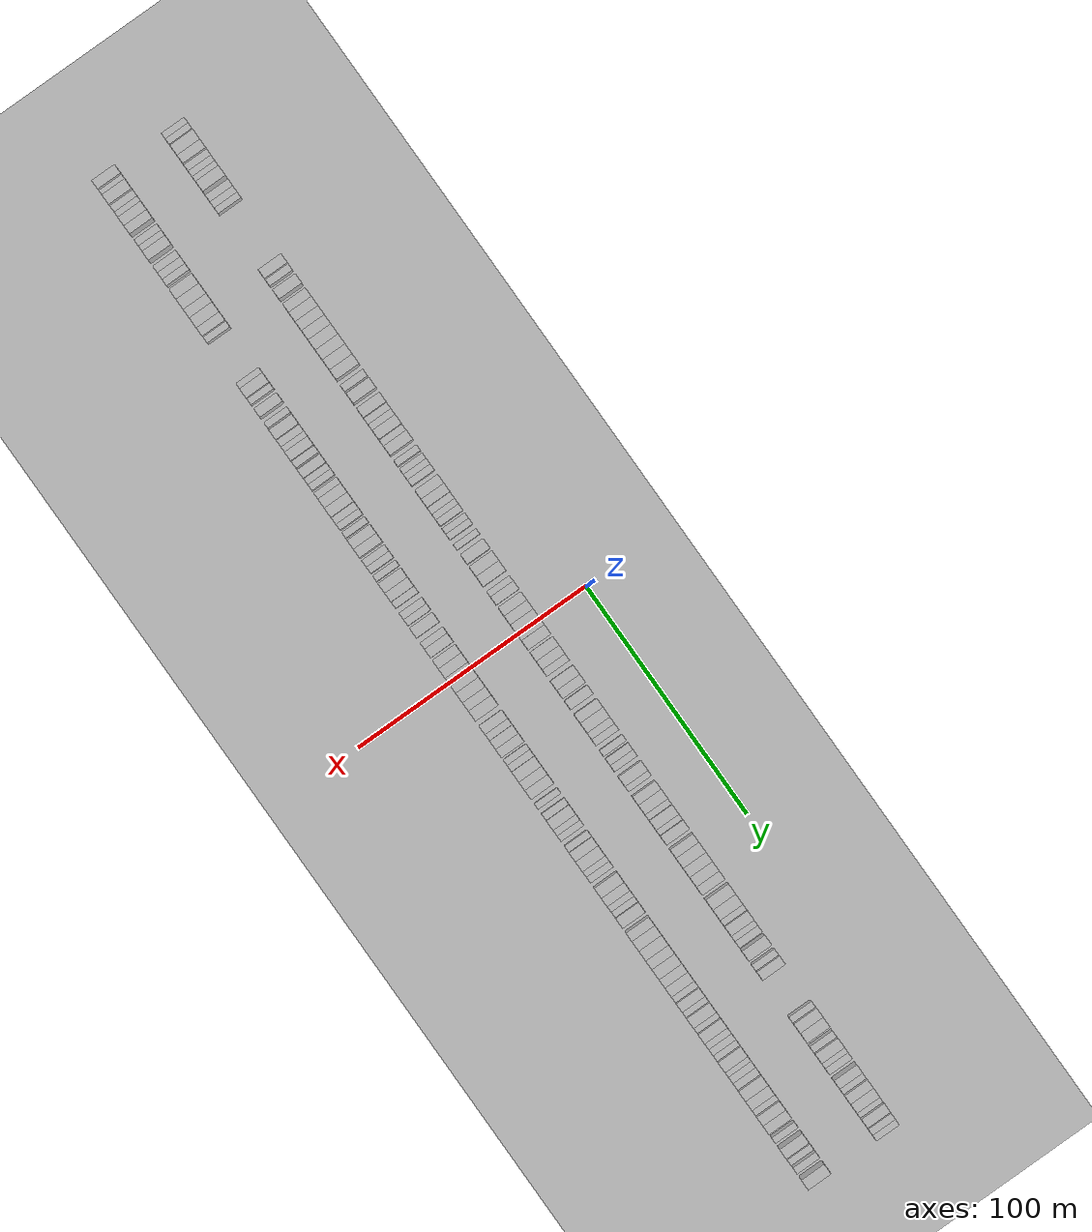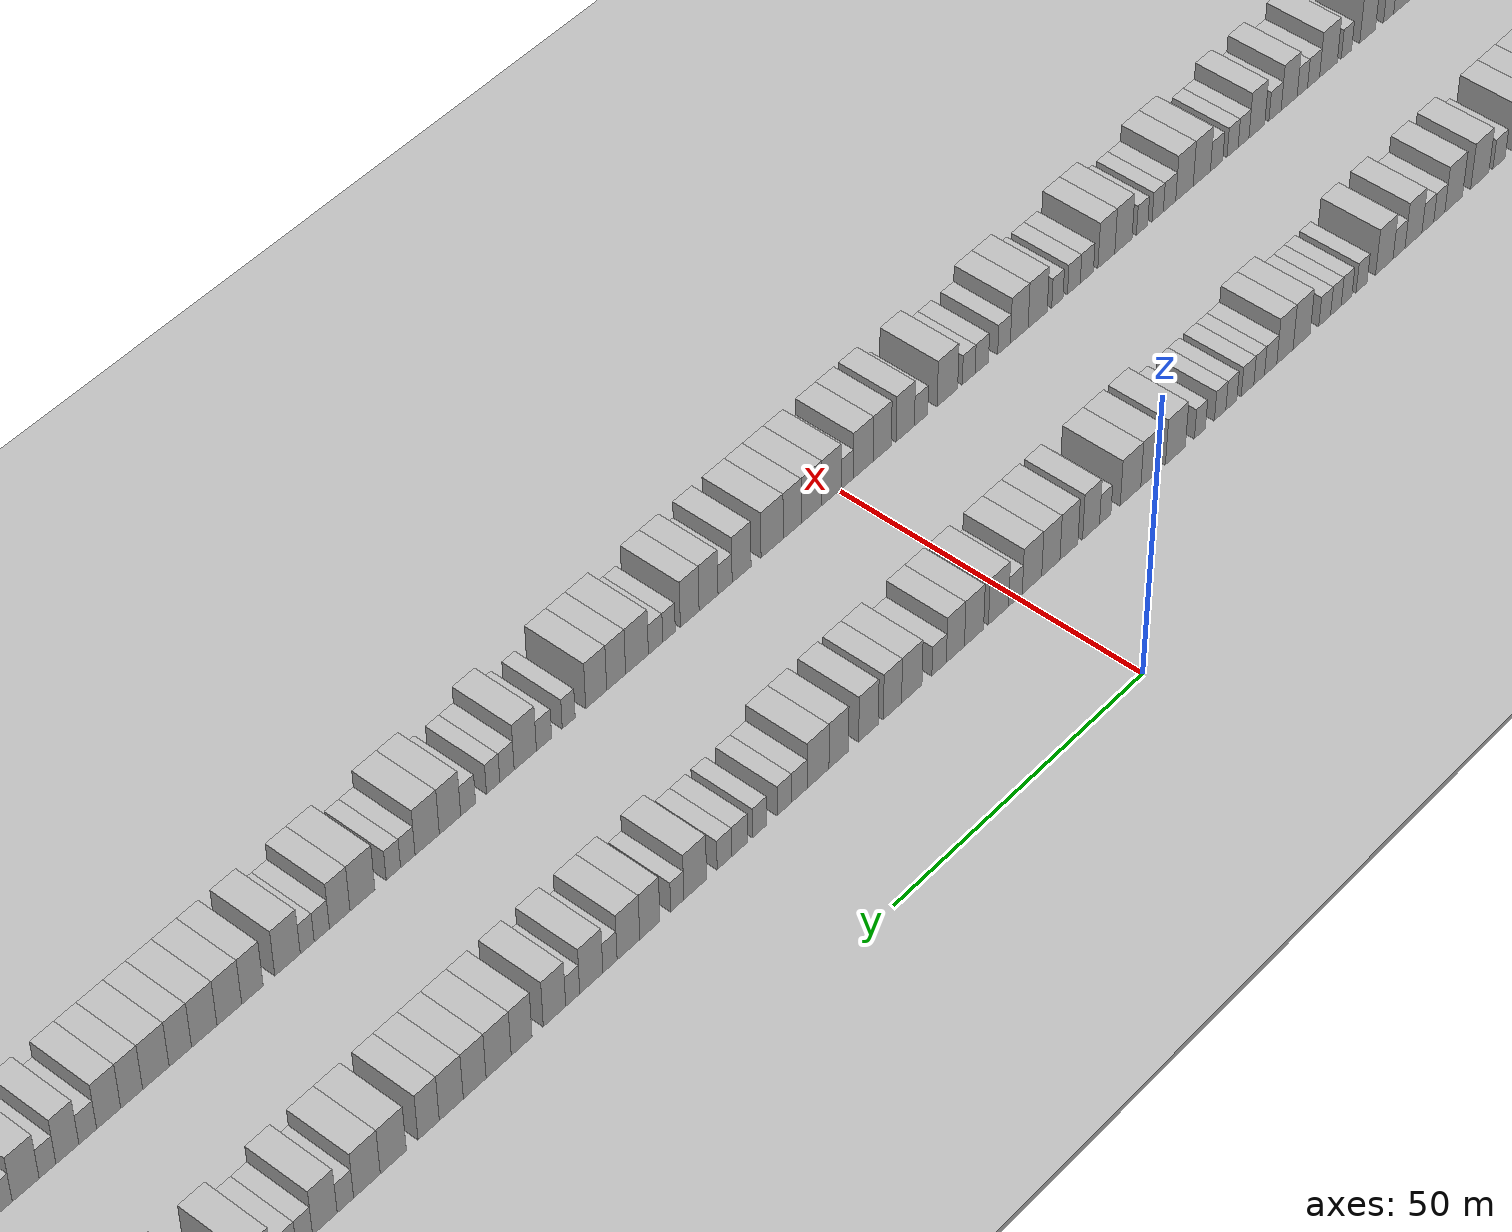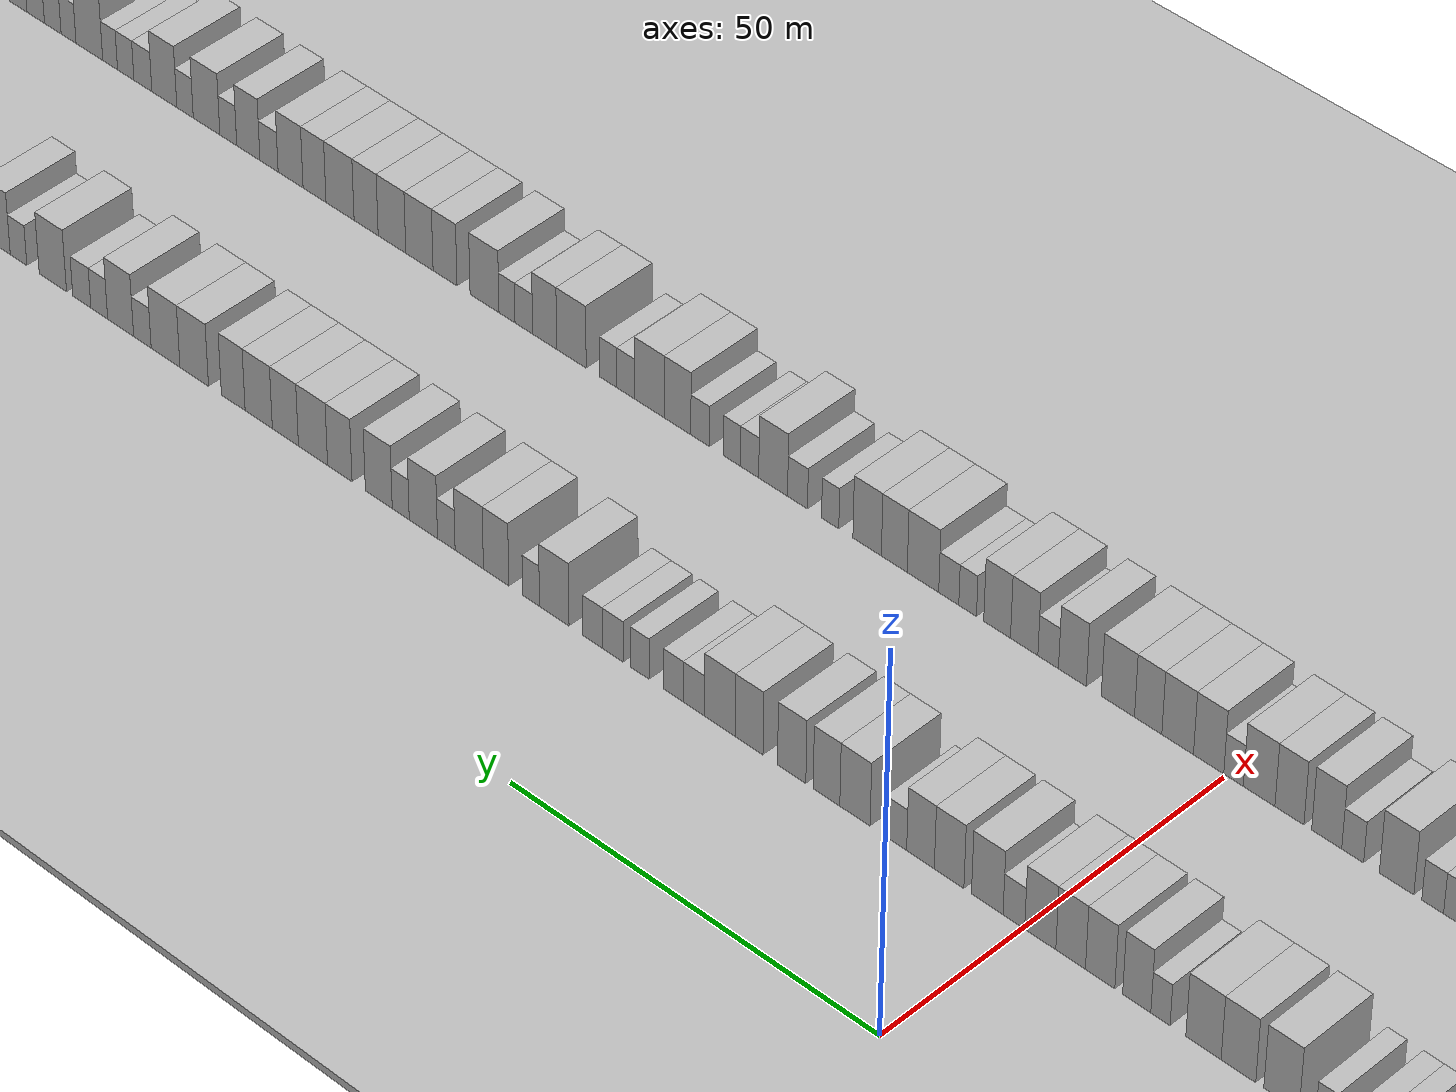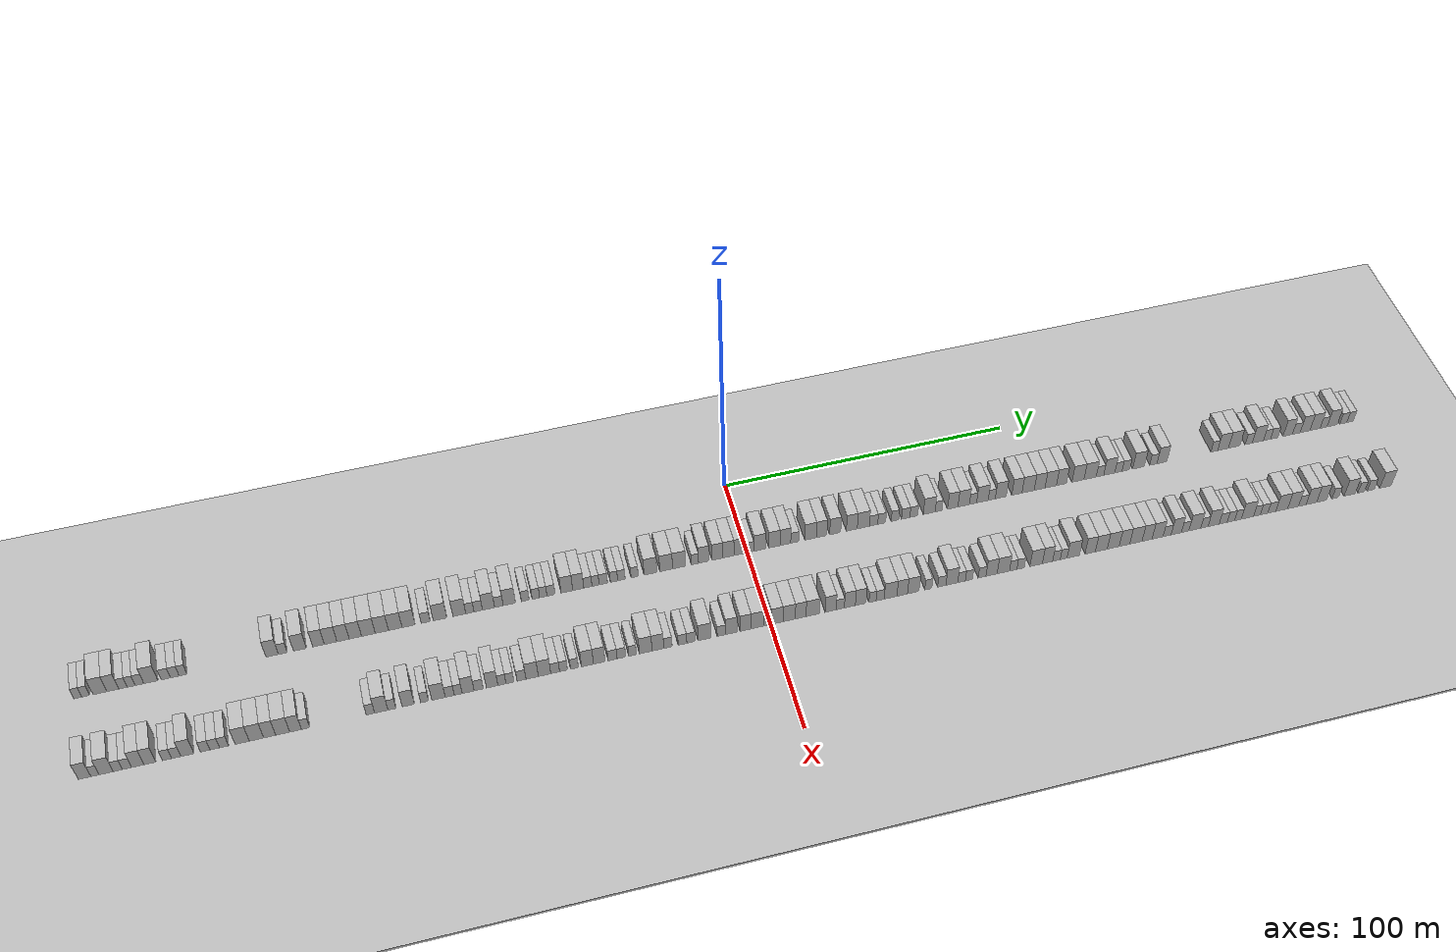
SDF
<?xml version="1.0" encoding="utf-8"?>

<sdf version="1.6">

   <world name="default">

      <gui fullscreen="0">

         <camera name="user_camera">

            <pose>-15 0 4.57585 0 0 0</pose>

            <view_controller>orbit</view_controller>

         </camera>

      </gui>

      <scene>

         <sky>

           <clouds>

             <speed>12</speed>

           </clouds>

         </sky>

         <ambient>0.4 0.4 0.4 1</ambient>

         <background>0.7 0.7 0.7 1</background>

         <shadows>1</shadows>

      </scene>

      <gravity>0 0 -9.8066</gravity>

      <magnetic_field>6e-06 2.3e-05 -4.2e-05</magnetic_field>

      <physics default="0" name="default_physics" type="ode">

         <ode>

            <solver>

               <type>quick</type>

               <iters>10</iters>

               <sor>1.0</sor>

               <use_dynamic_moi_rescaling>0</use_dynamic_moi_rescaling>

            </solver>

            <constraints>

               <cfm>0</cfm>

               <erp>0.2</erp>

               <contact_max_correcting_vel>100</contact_max_correcting_vel>

               <contact_surface_layer>0.001</contact_surface_layer>

            </constraints>

         </ode>

         <max_step_size>0.004</max_step_size>

         <real_time_factor>1</real_time_factor>

         <real_time_update_rate>250</real_time_update_rate>

      </physics>

      <light name="sun" type="directional">

         <cast_shadows>1</cast_shadows>

         <pose>0 0 10 0 0 0</pose>

         <diffuse>0.8 0.8 0.8 1</diffuse>

         <specular>0.2 0.2 0.2 1</specular>

         <attenuation>

            <range>1000</range>

            <constant>0.9</constant>

            <linear>0.01</linear>

            <quadratic>0.001</quadratic>

         </attenuation>

         <direction>-0.5 0.1 -0.9</direction>

      </light>

      <include>

         <name>ground_plane_1</name>

         <uri>model://HANNAS_ground_plane</uri>

         <pose>0 0 0  0 0 0</pose>

      </include>

      <include>

         <name>ground_plane_2</name>

         <uri>model://HANNAS_ground_plane</uri>

         <pose>100 0 0  0 0 0</pose>

      </include>

      <model name="building_1">

         <static>1</static>

         <pose frame="">25.0000 -218.7661 0 0.000000 0.000000 0.000000</pose>

         <link name="link">

            <pose frame="">0 0 3.00 0 0 0</pose>

            <collision name="collision">

               <geometry>

                  <box>

                     <size>10.0000 2.4679 6.0000</size>

                  </box>

               </geometry>

               <max_contacts>10</max_contacts>

               <surface>

                  <contact>

                     <ode/>

                  </contact>

                  <bounce/>

                  <friction>

                     <torsional>

                        <ode/>

                     </torsional>

                     <ode/>

                  </friction>

               </surface>

            </collision>

            <visual name="visual">

               <cast_shadows>0</cast_shadows>

               <geometry>

                  <box>

                     <size>10.0000 2.4679 6.0000</size>

                  </box>

               </geometry>

               <material>

                  <script>

                     <uri>model://HANNAS_wall/materials/scripts</uri>

                     <uri>model://HANNAS_wall/materials/textures</uri>

                     <name>vrc/HANNAS_wall</name>

                  </script>

               </material>

            </visual>

            <self_collide>0</self_collide>

            <enable_wind>0</enable_wind>

            <kinematic>0</kinematic>

         </link>

      </model>

      <model name="building_2">

         <static>1</static>

         <pose frame="">25.0000 -216.3126 0 0.000000 0.000000 0.000000</pose>

         <link name="link">

            <pose frame="">0 0 3.00 0 0 0</pose>

            <collision name="collision">

               <geometry>

                  <box>

                     <size>10.0000 2.4391 6.0000</size>

                  </box>

               </geometry>

               <max_contacts>10</max_contacts>

               <surface>

                  <contact>

                     <ode/>

                  </contact>

                  <bounce/>

                  <friction>

                     <torsional>

                        <ode/>

                     </torsional>

                     <ode/>

                  </friction>

               </surface>

            </collision>

            <visual name="visual">

               <cast_shadows>0</cast_shadows>

               <geometry>

                  <box>

                     <size>10.0000 2.4391 6.0000</size>

                  </box>

               </geometry>

               <material>

                  <script>

                     <uri>model://HANNAS_wall/materials/scripts</uri>

                     <uri>model://HANNAS_wall/materials/textures</uri>

                     <name>vrc/HANNAS_wall</name>

                  </script>

               </material>

            </visual>

            <self_collide>0</self_collide>

            <enable_wind>0</enable_wind>

            <kinematic>0</kinematic>

         </link>

      </model>

      <model name="building_3">

         <static>1</static>

         <pose frame="">25.0000 -211.9089 0 0.000000 0.000000 0.000000</pose>

         <link name="link">

            <pose frame="">0 0 4.50 0 0 0</pose>

            <collision name="collision">

               <geometry>

                  <box>

                     <size>10.0000 4.3683 9.0000</size>

                  </box>

               </geometry>

               <max_contacts>10</max_contacts>

               <surface>

                  <contact>

                     <ode/>

                  </contact>

                  <bounce/>

                  <friction>

                     <torsional>

                        <ode/>

                     </torsional>

                     <ode/>

                  </friction>

               </surface>

            </collision>

            <visual name="visual">

               <cast_shadows>0</cast_shadows>

               <geometry>

                  <box>

                     <size>10.0000 4.3683 9.0000</size>

                  </box>

               </geometry>

               <material>

                  <script>

                     <uri>model://HANNAS_wall/materials/scripts</uri>

                     <uri>model://HANNAS_wall/materials/textures</uri>

                     <name>vrc/HANNAS_wall</name>

                  </script>

               </material>

            </visual>

            <self_collide>0</self_collide>

            <enable_wind>0</enable_wind>

            <kinematic>0</kinematic>

         </link>

      </model>

      <model name="building_4">

         <static>1</static>

         <pose frame="">25.0000 -207.9164 0 0.000000 0.000000 0.000000</pose>

         <link name="link">

            <pose frame="">0 0 4.50 0 0 0</pose>

            <collision name="collision">

               <geometry>

                  <box>

                     <size>10.0000 3.6167 9.0000</size>

                  </box>

               </geometry>

               <max_contacts>10</max_contacts>

               <surface>

                  <contact>

                     <ode/>

                  </contact>

                  <bounce/>

                  <friction>

                     <torsional>

                        <ode/>

                     </torsional>

                     <ode/>

                  </friction>

               </surface>

            </collision>

            <visual name="visual">

               <cast_shadows>0</cast_shadows>

               <geometry>

                  <box>

                     <size>10.0000 3.6167 9.0000</size>

                  </box>

               </geometry>

               <material>

                  <script>

                     <uri>model://HANNAS_wall/materials/scripts</uri>

                     <uri>model://HANNAS_wall/materials/textures</uri>

                     <name>vrc/HANNAS_wall</name>

                  </script>

               </material>

            </visual>

            <self_collide>0</self_collide>

            <enable_wind>0</enable_wind>

            <kinematic>0</kinematic>

         </link>

      </model>

      <model name="building_5">

         <static>1</static>

         <pose frame="">25.0000 -204.7812 0 0.000000 0.000000 0.000000</pose>

         <link name="link">

            <pose frame="">0 0 3.00 0 0 0</pose>

            <collision name="collision">

               <geometry>

                  <box>

                     <size>10.0000 2.6537 6.0000</size>

                  </box>

               </geometry>

               <max_contacts>10</max_contacts>

               <surface>

                  <contact>

                     <ode/>

                  </contact>

                  <bounce/>

                  <friction>

                     <torsional>

                        <ode/>

                     </torsional>

                     <ode/>

                  </friction>

               </surface>

            </collision>

            <visual name="visual">

               <cast_shadows>0</cast_shadows>

               <geometry>

                  <box>

                     <size>10.0000 2.6537 6.0000</size>

                  </box>

               </geometry>

               <material>

                  <script>

                     <uri>model://HANNAS_wall/materials/scripts</uri>

                     <uri>model://HANNAS_wall/materials/textures</uri>

                     <name>vrc/HANNAS_wall</name>

                  </script>

               </material>

            </visual>

            <self_collide>0</self_collide>

            <enable_wind>0</enable_wind>

            <kinematic>0</kinematic>

         </link>

      </model>

      <model name="building_6">

         <static>1</static>

         <pose frame="">25.0000 -202.2221 0 0.000000 0.000000 0.000000</pose>

         <link name="link">

            <pose frame="">0 0 3.00 0 0 0</pose>

            <collision name="collision">

               <geometry>

                  <box>

                     <size>10.0000 2.4645 6.0000</size>

                  </box>

               </geometry>

               <max_contacts>10</max_contacts>

               <surface>

                  <contact>

                     <ode/>

                  </contact>

                  <bounce/>

                  <friction>

                     <torsional>

                        <ode/>

                     </torsional>

                     <ode/>

                  </friction>

               </surface>

            </collision>

            <visual name="visual">

               <cast_shadows>0</cast_shadows>

               <geometry>

                  <box>

                     <size>10.0000 2.4645 6.0000</size>

                  </box>

               </geometry>

               <material>

                  <script>

                     <uri>model://HANNAS_wall/materials/scripts</uri>

                     <uri>model://HANNAS_wall/materials/textures</uri>

                     <name>vrc/HANNAS_wall</name>

                  </script>

               </material>

            </visual>

            <self_collide>0</self_collide>

            <enable_wind>0</enable_wind>

            <kinematic>0</kinematic>

         </link>

      </model>

      <model name="building_7">

         <static>1</static>

         <pose frame="">25.0000 -199.6462 0 0.000000 0.000000 0.000000</pose>

         <link name="link">

            <pose frame="">0 0 3.00 0 0 0</pose>

            <collision name="collision">

               <geometry>

                  <box>

                     <size>10.0000 2.6873 6.0000</size>

                  </box>

               </geometry>

               <max_contacts>10</max_contacts>

               <surface>

                  <contact>

                     <ode/>

                  </contact>

                  <bounce/>

                  <friction>

                     <torsional>

                        <ode/>

                     </torsional>

                     <ode/>

                  </friction>

               </surface>

            </collision>

            <visual name="visual">

               <cast_shadows>0</cast_shadows>

               <geometry>

                  <box>

                     <size>10.0000 2.6873 6.0000</size>

                  </box>

               </geometry>

               <material>

                  <script>

                     <uri>model://HANNAS_wall/materials/scripts</uri>

                     <uri>model://HANNAS_wall/materials/textures</uri>

                     <name>vrc/HANNAS_wall</name>

                  </script>

               </material>

            </visual>

            <self_collide>0</self_collide>

            <enable_wind>0</enable_wind>

            <kinematic>0</kinematic>

         </link>

      </model>

      <model name="building_8">

         <static>1</static>

         <pose frame="">25.0000 -196.1025 0 0.000000 0.000000 0.000000</pose>

         <link name="link">

            <pose frame="">0 0 4.50 0 0 0</pose>

            <collision name="collision">

               <geometry>

                  <box>

                     <size>10.0000 4.4001 9.0000</size>

                  </box>

               </geometry>

               <max_contacts>10</max_contacts>

               <surface>

                  <contact>

                     <ode/>

                  </contact>

                  <bounce/>

                  <friction>

                     <torsional>

                        <ode/>

                     </torsional>

                     <ode/>

                  </friction>

               </surface>

            </collision>

            <visual name="visual">

               <cast_shadows>0</cast_shadows>

               <geometry>

                  <box>

                     <size>10.0000 4.4001 9.0000</size>

                  </box>

               </geometry>

               <material>

                  <script>

                     <uri>model://HANNAS_wall/materials/scripts</uri>

                     <uri>model://HANNAS_wall/materials/textures</uri>

                     <name>vrc/HANNAS_wall</name>

                  </script>

               </material>

            </visual>

            <self_collide>0</self_collide>

            <enable_wind>0</enable_wind>

            <kinematic>0</kinematic>

         </link>

      </model>

      <model name="building_9">

         <static>1</static>

         <pose frame="">25.0000 -191.4242 0 0.000000 0.000000 0.000000</pose>

         <link name="link">

            <pose frame="">0 0 3.00 0 0 0</pose>

            <collision name="collision">

               <geometry>

                  <box>

                     <size>10.0000 2.9565 6.0000</size>

                  </box>

               </geometry>

               <max_contacts>10</max_contacts>

               <surface>

                  <contact>

                     <ode/>

                  </contact>

                  <bounce/>

                  <friction>

                     <torsional>

                        <ode/>

                     </torsional>

                     <ode/>

                  </friction>

               </surface>

            </collision>

            <visual name="visual">

               <cast_shadows>0</cast_shadows>

               <geometry>

                  <box>

                     <size>10.0000 2.9565 6.0000</size>

                  </box>

               </geometry>

               <material>

                  <script>

                     <uri>model://HANNAS_wall/materials/scripts</uri>

                     <uri>model://HANNAS_wall/materials/textures</uri>

                     <name>vrc/HANNAS_wall</name>

                  </script>

               </material>

            </visual>

            <self_collide>0</self_collide>

            <enable_wind>0</enable_wind>

            <kinematic>0</kinematic>

         </link>

      </model>

      <model name="building_10">

         <static>1</static>

         <pose frame="">25.0000 -188.5970 0 0.000000 0.000000 0.000000</pose>

         <link name="link">

            <pose frame="">0 0 3.00 0 0 0</pose>

            <collision name="collision">

               <geometry>

                  <box>

                     <size>10.0000 2.6980 6.0000</size>

                  </box>

               </geometry>

               <max_contacts>10</max_contacts>

               <surface>

                  <contact>

                     <ode/>

                  </contact>

                  <bounce/>

                  <friction>

                     <torsional>

                        <ode/>

                     </torsional>

                     <ode/>

                  </friction>

               </surface>

            </collision>

            <visual name="visual">

               <cast_shadows>0</cast_shadows>

               <geometry>

                  <box>

                     <size>10.0000 2.6980 6.0000</size>

                  </box>

               </geometry>

               <material>

                  <script>

                     <uri>model://HANNAS_wall/materials/scripts</uri>

                     <uri>model://HANNAS_wall/materials/textures</uri>

                     <name>vrc/HANNAS_wall</name>

                  </script>

               </material>

            </visual>

            <self_collide>0</self_collide>

            <enable_wind>0</enable_wind>

            <kinematic>0</kinematic>

         </link>

      </model>

      <model name="building_11">

         <static>1</static>

         <pose frame="">25.0000 -186.0118 0 0.000000 0.000000 0.000000</pose>

         <link name="link">

            <pose frame="">0 0 3.00 0 0 0</pose>

            <collision name="collision">

               <geometry>

                  <box>

                     <size>10.0000 2.4724 6.0000</size>

                  </box>

               </geometry>

               <max_contacts>10</max_contacts>

               <surface>

                  <contact>

                     <ode/>

                  </contact>

                  <bounce/>

                  <friction>

                     <torsional>

                        <ode/>

                     </torsional>

                     <ode/>

                  </friction>

               </surface>

            </collision>

            <visual name="visual">

               <cast_shadows>0</cast_shadows>

               <geometry>

                  <box>

                     <size>10.0000 2.4724 6.0000</size>

                  </box>

               </geometry>

               <material>

                  <script>

                     <uri>model://HANNAS_wall/materials/scripts</uri>

                     <uri>model://HANNAS_wall/materials/textures</uri>

                     <name>vrc/HANNAS_wall</name>

                  </script>

               </material>

            </visual>

            <self_collide>0</self_collide>

            <enable_wind>0</enable_wind>

            <kinematic>0</kinematic>

         </link>

      </model>

      <model name="building_12">

         <static>1</static>

         <pose frame="">25.0000 -157.7931 0 0.000000 0.000000 0.000000</pose>

         <link name="link">

            <pose frame="">0 0 4.50 0 0 0</pose>

            <collision name="collision">

               <geometry>

                  <box>

                     <size>10.0000 3.9883 9.0000</size>

                  </box>

               </geometry>

               <max_contacts>10</max_contacts>

               <surface>

                  <contact>

                     <ode/>

                  </contact>

                  <bounce/>

                  <friction>

                     <torsional>

                        <ode/>

                     </torsional>

                     <ode/>

                  </friction>

               </surface>

            </collision>

            <visual name="visual">

               <cast_shadows>0</cast_shadows>

               <geometry>

                  <box>

                     <size>10.0000 3.9883 9.0000</size>

                  </box>

               </geometry>

               <material>

                  <script>

                     <uri>model://HANNAS_wall/materials/scripts</uri>

                     <uri>model://HANNAS_wall/materials/textures</uri>

                     <name>vrc/HANNAS_wall</name>

                  </script>

               </material>

            </visual>

            <self_collide>0</self_collide>

            <enable_wind>0</enable_wind>

            <kinematic>0</kinematic>

         </link>

      </model>

      <model name="building_13">

         <static>1</static>

         <pose frame="">25.0000 -154.4034 0 0.000000 0.000000 0.000000</pose>

         <link name="link">

            <pose frame="">0 0 3.00 0 0 0</pose>

            <collision name="collision">

               <geometry>

                  <box>

                     <size>10.0000 2.7912 6.0000</size>

                  </box>

               </geometry>

               <max_contacts>10</max_contacts>

               <surface>

                  <contact>

                     <ode/>

                  </contact>

                  <bounce/>

                  <friction>

                     <torsional>

                        <ode/>

                     </torsional>

                     <ode/>

                  </friction>

               </surface>

            </collision>

            <visual name="visual">

               <cast_shadows>0</cast_shadows>

               <geometry>

                  <box>

                     <size>10.0000 2.7912 6.0000</size>

                  </box>

               </geometry>

               <material>

                  <script>

                     <uri>model://HANNAS_wall/materials/scripts</uri>

                     <uri>model://HANNAS_wall/materials/textures</uri>

                     <name>vrc/HANNAS_wall</name>

                  </script>

               </material>

            </visual>

            <self_collide>0</self_collide>

            <enable_wind>0</enable_wind>

            <kinematic>0</kinematic>

         </link>

      </model>

      <model name="building_14">

         <static>1</static>

         <pose frame="">25.0000 -148.9291 0 0.000000 0.000000 0.000000</pose>

         <link name="link">

            <pose frame="">0 0 4.50 0 0 0</pose>

            <collision name="collision">

               <geometry>

                  <box>

                     <size>10.0000 4.1573 9.0000</size>

                  </box>

               </geometry>

               <max_contacts>10</max_contacts>

               <surface>

                  <contact>

                     <ode/>

                  </contact>

                  <bounce/>

                  <friction>

                     <torsional>

                        <ode/>

                     </torsional>

                     <ode/>

                  </friction>

               </surface>

            </collision>

            <visual name="visual">

               <cast_shadows>0</cast_shadows>

               <geometry>

                  <box>

                     <size>10.0000 4.1573 9.0000</size>

                  </box>

               </geometry>

               <material>

                  <script>

                     <uri>model://HANNAS_wall/materials/scripts</uri>

                     <uri>model://HANNAS_wall/materials/textures</uri>

                     <name>vrc/HANNAS_wall</name>

                  </script>

               </material>

            </visual>

            <self_collide>0</self_collide>

            <enable_wind>0</enable_wind>

            <kinematic>0</kinematic>

         </link>

      </model>

      <model name="building_15">

         <static>1</static>

         <pose frame="">25.0000 -142.9591 0 0.000000 0.000000 0.000000</pose>

         <link name="link">

            <pose frame="">0 0 4.50 0 0 0</pose>

            <collision name="collision">

               <geometry>

                  <box>

                     <size>10.0000 3.7828 9.0000</size>

                  </box>

               </geometry>

               <max_contacts>10</max_contacts>

               <surface>

                  <contact>

                     <ode/>

                  </contact>

                  <bounce/>

                  <friction>

                     <torsional>

                        <ode/>

                     </torsional>

                     <ode/>

                  </friction>

               </surface>

            </collision>

            <visual name="visual">

               <cast_shadows>0</cast_shadows>

               <geometry>

                  <box>

                     <size>10.0000 3.7828 9.0000</size>

                  </box>

               </geometry>

               <material>

                  <script>

                     <uri>model://HANNAS_wall/materials/scripts</uri>

                     <uri>model://HANNAS_wall/materials/textures</uri>

                     <name>vrc/HANNAS_wall</name>

                  </script>

               </material>

            </visual>

            <self_collide>0</self_collide>

            <enable_wind>0</enable_wind>

            <kinematic>0</kinematic>

         </link>

      </model>

      <model name="building_16">

         <static>1</static>

         <pose frame="">25.0000 -139.0517 0 0.000000 0.000000 0.000000</pose>

         <link name="link">

            <pose frame="">0 0 4.50 0 0 0</pose>

            <collision name="collision">

               <geometry>

                  <box>

                     <size>10.0000 4.0319 9.0000</size>

                  </box>

               </geometry>

               <max_contacts>10</max_contacts>

               <surface>

                  <contact>

                     <ode/>

                  </contact>

                  <bounce/>

                  <friction>

                     <torsional>

                        <ode/>

                     </torsional>

                     <ode/>

                  </friction>

               </surface>

            </collision>

            <visual name="visual">

               <cast_shadows>0</cast_shadows>

               <geometry>

                  <box>

                     <size>10.0000 4.0319 9.0000</size>

                  </box>

               </geometry>

               <material>

                  <script>

                     <uri>model://HANNAS_wall/materials/scripts</uri>

                     <uri>model://HANNAS_wall/materials/textures</uri>

                     <name>vrc/HANNAS_wall</name>

                  </script>

               </material>

            </visual>

            <self_collide>0</self_collide>

            <enable_wind>0</enable_wind>

            <kinematic>0</kinematic>

         </link>

      </model>

      <model name="building_17">

         <static>1</static>

         <pose frame="">25.0000 -135.0709 0 0.000000 0.000000 0.000000</pose>

         <link name="link">

            <pose frame="">0 0 4.50 0 0 0</pose>

            <collision name="collision">

               <geometry>

                  <box>

                     <size>10.0000 3.9298 9.0000</size>

                  </box>

               </geometry>

               <max_contacts>10</max_contacts>

               <surface>

                  <contact>

                     <ode/>

                  </contact>

                  <bounce/>

                  <friction>

                     <torsional>

                        <ode/>

                     </torsional>

                     <ode/>

                  </friction>

               </surface>

            </collision>

            <visual name="visual">

               <cast_shadows>0</cast_shadows>

               <geometry>

                  <box>

                     <size>10.0000 3.9298 9.0000</size>

                  </box>

               </geometry>

               <material>

                  <script>

                     <uri>model://HANNAS_wall/materials/scripts</uri>

                     <uri>model://HANNAS_wall/materials/textures</uri>

                     <name>vrc/HANNAS_wall</name>

                  </script>

               </material>

            </visual>

            <self_collide>0</self_collide>

            <enable_wind>0</enable_wind>

            <kinematic>0</kinematic>

         </link>

      </model>

      <model name="building_18">

         <static>1</static>

         <pose frame="">25.0000 -131.0898 0 0.000000 0.000000 0.000000</pose>

         <link name="link">

            <pose frame="">0 0 4.50 0 0 0</pose>

            <collision name="collision">

               <geometry>

                  <box>

                     <size>10.0000 4.0324 9.0000</size>

                  </box>

               </geometry>

               <max_contacts>10</max_contacts>

               <surface>

                  <contact>

                     <ode/>

                  </contact>

                  <bounce/>

                  <friction>

                     <torsional>

                        <ode/>

                     </torsional>

                     <ode/>

                  </friction>

               </surface>

            </collision>

            <visual name="visual">

               <cast_shadows>0</cast_shadows>

               <geometry>

                  <box>

                     <size>10.0000 4.0324 9.0000</size>

                  </box>

               </geometry>

               <material>

                  <script>

                     <uri>model://HANNAS_wall/materials/scripts</uri>

                     <uri>model://HANNAS_wall/materials/textures</uri>

                     <name>vrc/HANNAS_wall</name>

                  </script>

               </material>

            </visual>

            <self_collide>0</self_collide>

            <enable_wind>0</enable_wind>

            <kinematic>0</kinematic>

         </link>

      </model>

      <model name="building_19">

         <static>1</static>

         <pose frame="">25.0000 -126.8528 0 0.000000 0.000000 0.000000</pose>

         <link name="link">

            <pose frame="">0 0 4.50 0 0 0</pose>

            <collision name="collision">

               <geometry>

                  <box>

                     <size>10.0000 4.4417 9.0000</size>

                  </box>

               </geometry>

               <max_contacts>10</max_contacts>

               <surface>

                  <contact>

                     <ode/>

                  </contact>

                  <bounce/>

                  <friction>

                     <torsional>

                        <ode/>

                     </torsional>

                     <ode/>

                  </friction>

               </surface>

            </collision>

            <visual name="visual">

               <cast_shadows>0</cast_shadows>

               <geometry>

                  <box>

                     <size>10.0000 4.4417 9.0000</size>

                  </box>

               </geometry>

               <material>

                  <script>

                     <uri>model://HANNAS_wall/materials/scripts</uri>

                     <uri>model://HANNAS_wall/materials/textures</uri>

                     <name>vrc/HANNAS_wall</name>

                  </script>

               </material>

            </visual>

            <self_collide>0</self_collide>

            <enable_wind>0</enable_wind>

            <kinematic>0</kinematic>

         </link>

      </model>

      <model name="building_20">

         <static>1</static>

         <pose frame="">25.0000 -122.4812 0 0.000000 0.000000 0.000000</pose>

         <link name="link">

            <pose frame="">0 0 4.50 0 0 0</pose>

            <collision name="collision">

               <geometry>

                  <box>

                     <size>10.0000 4.3014 9.0000</size>

                  </box>

               </geometry>

               <max_contacts>10</max_contacts>

               <surface>

                  <contact>

                     <ode/>

                  </contact>

                  <bounce/>

                  <friction>

                     <torsional>

                        <ode/>

                     </torsional>

                     <ode/>

                  </friction>

               </surface>

            </collision>

            <visual name="visual">

               <cast_shadows>0</cast_shadows>

               <geometry>

                  <box>

                     <size>10.0000 4.3014 9.0000</size>

                  </box>

               </geometry>

               <material>

                  <script>

                     <uri>model://HANNAS_wall/materials/scripts</uri>

                     <uri>model://HANNAS_wall/materials/textures</uri>

                     <name>vrc/HANNAS_wall</name>

                  </script>

               </material>

            </visual>

            <self_collide>0</self_collide>

            <enable_wind>0</enable_wind>

            <kinematic>0</kinematic>

         </link>

      </model>

      <model name="building_21">

         <static>1</static>

         <pose frame="">25.0000 -118.1228 0 0.000000 0.000000 0.000000</pose>

         <link name="link">

            <pose frame="">0 0 4.50 0 0 0</pose>

            <collision name="collision">

               <geometry>

                  <box>

                     <size>10.0000 4.4153 9.0000</size>

                  </box>

               </geometry>

               <max_contacts>10</max_contacts>

               <surface>

                  <contact>

                     <ode/>

                  </contact>

                  <bounce/>

                  <friction>

                     <torsional>

                        <ode/>

                     </torsional>

                     <ode/>

                  </friction>

               </surface>

            </collision>

            <visual name="visual">

               <cast_shadows>0</cast_shadows>

               <geometry>

                  <box>

                     <size>10.0000 4.4153 9.0000</size>

                  </box>

               </geometry>

               <material>

                  <script>

                     <uri>model://HANNAS_wall/materials/scripts</uri>

                     <uri>model://HANNAS_wall/materials/textures</uri>

                     <name>vrc/HANNAS_wall</name>

                  </script>

               </material>

            </visual>

            <self_collide>0</self_collide>

            <enable_wind>0</enable_wind>

            <kinematic>0</kinematic>

         </link>

      </model>

      <model name="building_22">

         <static>1</static>

         <pose frame="">25.0000 -113.7899 0 0.000000 0.000000 0.000000</pose>

         <link name="link">

            <pose frame="">0 0 4.50 0 0 0</pose>

            <collision name="collision">

               <geometry>

                  <box>

                     <size>10.0000 4.2507 9.0000</size>

                  </box>

               </geometry>

               <max_contacts>10</max_contacts>

               <surface>

                  <contact>

                     <ode/>

                  </contact>

                  <bounce/>

                  <friction>

                     <torsional>

                        <ode/>

                     </torsional>

                     <ode/>

                  </friction>

               </surface>

            </collision>

            <visual name="visual">

               <cast_shadows>0</cast_shadows>

               <geometry>

                  <box>

                     <size>10.0000 4.2507 9.0000</size>

                  </box>

               </geometry>

               <material>

                  <script>

                     <uri>model://HANNAS_wall/materials/scripts</uri>

                     <uri>model://HANNAS_wall/materials/textures</uri>

                     <name>vrc/HANNAS_wall</name>

                  </script>

               </material>

            </visual>

            <self_collide>0</self_collide>

            <enable_wind>0</enable_wind>

            <kinematic>0</kinematic>

         </link>

      </model>

      <model name="building_23">

         <static>1</static>

         <pose frame="">25.0000 -108.1817 0 0.000000 0.000000 0.000000</pose>

         <link name="link">

            <pose frame="">0 0 3.00 0 0 0</pose>

            <collision name="collision">

               <geometry>

                  <box>

                     <size>10.0000 2.9656 6.0000</size>

                  </box>

               </geometry>

               <max_contacts>10</max_contacts>

               <surface>

                  <contact>

                     <ode/>

                  </contact>

                  <bounce/>

                  <friction>

                     <torsional>

                        <ode/>

                     </torsional>

                     <ode/>

                  </friction>

               </surface>

            </collision>

            <visual name="visual">

               <cast_shadows>0</cast_shadows>

               <geometry>

                  <box>

                     <size>10.0000 2.9656 6.0000</size>

                  </box>

               </geometry>

               <material>

                  <script>

                     <uri>model://HANNAS_wall/materials/scripts</uri>

                     <uri>model://HANNAS_wall/materials/textures</uri>

                     <name>vrc/HANNAS_wall</name>

                  </script>

               </material>

            </visual>

            <self_collide>0</self_collide>

            <enable_wind>0</enable_wind>

            <kinematic>0</kinematic>

         </link>

      </model>

      <model name="building_24">

         <static>1</static>

         <pose frame="">25.0000 -103.4862 0 0.000000 0.000000 0.000000</pose>

         <link name="link">

            <pose frame="">0 0 4.50 0 0 0</pose>

            <collision name="collision">

               <geometry>

                  <box>

                     <size>10.0000 4.4254 9.0000</size>

                  </box>

               </geometry>

               <max_contacts>10</max_contacts>

               <surface>

                  <contact>

                     <ode/>

                  </contact>

                  <bounce/>

                  <friction>

                     <torsional>

                        <ode/>

                     </torsional>

                     <ode/>

                  </friction>

               </surface>

            </collision>

            <visual name="visual">

               <cast_shadows>0</cast_shadows>

               <geometry>

                  <box>

                     <size>10.0000 4.4254 9.0000</size>

                  </box>

               </geometry>

               <material>

                  <script>

                     <uri>model://HANNAS_wall/materials/scripts</uri>

                     <uri>model://HANNAS_wall/materials/textures</uri>

                     <name>vrc/HANNAS_wall</name>

                  </script>

               </material>

            </visual>

            <self_collide>0</self_collide>

            <enable_wind>0</enable_wind>

            <kinematic>0</kinematic>

         </link>

      </model>

      <model name="building_25">

         <static>1</static>

         <pose frame="">25.0000 -97.1496 0 0.000000 0.000000 0.000000</pose>

         <link name="link">

            <pose frame="">0 0 4.50 0 0 0</pose>

            <collision name="collision">

               <geometry>

                  <box>

                     <size>10.0000 4.2478 9.0000</size>

                  </box>

               </geometry>

               <max_contacts>10</max_contacts>

               <surface>

                  <contact>

                     <ode/>

                  </contact>

                  <bounce/>

                  <friction>

                     <torsional>

                        <ode/>

                     </torsional>

                     <ode/>

                  </friction>

               </surface>

            </collision>

            <visual name="visual">

               <cast_shadows>0</cast_shadows>

               <geometry>

                  <box>

                     <size>10.0000 4.2478 9.0000</size>

                  </box>

               </geometry>

               <material>

                  <script>

                     <uri>model://HANNAS_wall/materials/scripts</uri>

                     <uri>model://HANNAS_wall/materials/textures</uri>

                     <name>vrc/HANNAS_wall</name>

                  </script>

               </material>

            </visual>

            <self_collide>0</self_collide>

            <enable_wind>0</enable_wind>

            <kinematic>0</kinematic>

         </link>

      </model>

      <model name="building_26">

         <static>1</static>

         <pose frame="">25.0000 -93.6836 0 0.000000 0.000000 0.000000</pose>

         <link name="link">

            <pose frame="">0 0 3.00 0 0 0</pose>

            <collision name="collision">

               <geometry>

                  <box>

                     <size>10.0000 2.6841 6.0000</size>

                  </box>

               </geometry>

               <max_contacts>10</max_contacts>

               <surface>

                  <contact>

                     <ode/>

                  </contact>

                  <bounce/>

                  <friction>

                     <torsional>

                        <ode/>

                     </torsional>

                     <ode/>

                  </friction>

               </surface>

            </collision>

            <visual name="visual">

               <cast_shadows>0</cast_shadows>

               <geometry>

                  <box>

                     <size>10.0000 2.6841 6.0000</size>

                  </box>

               </geometry>

               <material>

                  <script>

                     <uri>model://HANNAS_wall/materials/scripts</uri>

                     <uri>model://HANNAS_wall/materials/textures</uri>

                     <name>vrc/HANNAS_wall</name>

                  </script>

               </material>

            </visual>

            <self_collide>0</self_collide>

            <enable_wind>0</enable_wind>

            <kinematic>0</kinematic>

         </link>

      </model>

      <model name="building_27">

         <static>1</static>

         <pose frame="">25.0000 -90.9342 0 0.000000 0.000000 0.000000</pose>

         <link name="link">

            <pose frame="">0 0 3.00 0 0 0</pose>

            <collision name="collision">

               <geometry>

                  <box>

                     <size>10.0000 2.8148 6.0000</size>

                  </box>

               </geometry>

               <max_contacts>10</max_contacts>

               <surface>

                  <contact>

                     <ode/>

                  </contact>

                  <bounce/>

                  <friction>

                     <torsional>

                        <ode/>

                     </torsional>

                     <ode/>

                  </friction>

               </surface>

            </collision>

            <visual name="visual">

               <cast_shadows>0</cast_shadows>

               <geometry>

                  <box>

                     <size>10.0000 2.8148 6.0000</size>

                  </box>

               </geometry>

               <material>

                  <script>

                     <uri>model://HANNAS_wall/materials/scripts</uri>

                     <uri>model://HANNAS_wall/materials/textures</uri>

                     <name>vrc/HANNAS_wall</name>

                  </script>

               </material>

            </visual>

            <self_collide>0</self_collide>

            <enable_wind>0</enable_wind>

            <kinematic>0</kinematic>

         </link>

      </model>

      <model name="building_28">

         <static>1</static>

         <pose frame="">25.0000 -87.5180 0 0.000000 0.000000 0.000000</pose>

         <link name="link">

            <pose frame="">0 0 4.50 0 0 0</pose>

            <collision name="collision">

               <geometry>

                  <box>

                     <size>10.0000 4.0176 9.0000</size>

                  </box>

               </geometry>

               <max_contacts>10</max_contacts>

               <surface>

                  <contact>

                     <ode/>

                  </contact>

                  <bounce/>

                  <friction>

                     <torsional>

                        <ode/>

                     </torsional>

                     <ode/>

                  </friction>

               </surface>

            </collision>

            <visual name="visual">

               <cast_shadows>0</cast_shadows>

               <geometry>

                  <box>

                     <size>10.0000 4.0176 9.0000</size>

                  </box>

               </geometry>

               <material>

                  <script>

                     <uri>model://HANNAS_wall/materials/scripts</uri>

                     <uri>model://HANNAS_wall/materials/textures</uri>

                     <name>vrc/HANNAS_wall</name>

                  </script>

               </material>

            </visual>

            <self_collide>0</self_collide>

            <enable_wind>0</enable_wind>

            <kinematic>0</kinematic>

         </link>

      </model>

      <model name="building_29">

         <static>1</static>

         <pose frame="">25.0000 -84.0877 0 0.000000 0.000000 0.000000</pose>

         <link name="link">

            <pose frame="">0 0 3.00 0 0 0</pose>

            <collision name="collision">

               <geometry>

                  <box>

                     <size>10.0000 2.8431 6.0000</size>

                  </box>

               </geometry>

               <max_contacts>10</max_contacts>

               <surface>

                  <contact>

                     <ode/>

                  </contact>

                  <bounce/>

                  <friction>

                     <torsional>

                        <ode/>

                     </torsional>

                     <ode/>

                  </friction>

               </surface>

            </collision>

            <visual name="visual">

               <cast_shadows>0</cast_shadows>

               <geometry>

                  <box>

                     <size>10.0000 2.8431 6.0000</size>

                  </box>

               </geometry>

               <material>

                  <script>

                     <uri>model://HANNAS_wall/materials/scripts</uri>

                     <uri>model://HANNAS_wall/materials/textures</uri>

                     <name>vrc/HANNAS_wall</name>

                  </script>

               </material>

            </visual>

            <self_collide>0</self_collide>

            <enable_wind>0</enable_wind>

            <kinematic>0</kinematic>

         </link>

      </model>

      <model name="building_30">

         <static>1</static>

         <pose frame="">25.0000 -80.6205 0 0.000000 0.000000 0.000000</pose>

         <link name="link">

            <pose frame="">0 0 4.50 0 0 0</pose>

            <collision name="collision">

               <geometry>

                  <box>

                     <size>10.0000 4.0912 9.0000</size>

                  </box>

               </geometry>

               <max_contacts>10</max_contacts>

               <surface>

                  <contact>

                     <ode/>

                  </contact>

                  <bounce/>

                  <friction>

                     <torsional>

                        <ode/>

                     </torsional>

                     <ode/>

                  </friction>

               </surface>

            </collision>

            <visual name="visual">

               <cast_shadows>0</cast_shadows>

               <geometry>

                  <box>

                     <size>10.0000 4.0912 9.0000</size>

                  </box>

               </geometry>

               <material>

                  <script>

                     <uri>model://HANNAS_wall/materials/scripts</uri>

                     <uri>model://HANNAS_wall/materials/textures</uri>

                     <name>vrc/HANNAS_wall</name>

                  </script>

               </material>

            </visual>

            <self_collide>0</self_collide>

            <enable_wind>0</enable_wind>

            <kinematic>0</kinematic>

         </link>

      </model>

      <model name="building_31">

         <static>1</static>

         <pose frame="">25.0000 -75.2933 0 0.000000 0.000000 0.000000</pose>

         <link name="link">

            <pose frame="">0 0 3.00 0 0 0</pose>

            <collision name="collision">

               <geometry>

                  <box>

                     <size>10.0000 2.5630 6.0000</size>

                  </box>

               </geometry>

               <max_contacts>10</max_contacts>

               <surface>

                  <contact>

                     <ode/>

                  </contact>

                  <bounce/>

                  <friction>

                     <torsional>

                        <ode/>

                     </torsional>

                     <ode/>

                  </friction>

               </surface>

            </collision>

            <visual name="visual">

               <cast_shadows>0</cast_shadows>

               <geometry>

                  <box>

                     <size>10.0000 2.5630 6.0000</size>

                  </box>

               </geometry>

               <material>

                  <script>

                     <uri>model://HANNAS_wall/materials/scripts</uri>

                     <uri>model://HANNAS_wall/materials/textures</uri>

                     <name>vrc/HANNAS_wall</name>

                  </script>

               </material>

            </visual>

            <self_collide>0</self_collide>

            <enable_wind>0</enable_wind>

            <kinematic>0</kinematic>

         </link>

      </model>

      <model name="building_32">

         <static>1</static>

         <pose frame="">25.0000 -71.7716 0 0.000000 0.000000 0.000000</pose>

         <link name="link">

            <pose frame="">0 0 3.00 0 0 0</pose>

            <collision name="collision">

               <geometry>

                  <box>

                     <size>10.0000 2.4804 6.0000</size>

                  </box>

               </geometry>

               <max_contacts>10</max_contacts>

               <surface>

                  <contact>

                     <ode/>

                  </contact>

                  <bounce/>

                  <friction>

                     <torsional>

                        <ode/>

                     </torsional>

                     <ode/>

                  </friction>

               </surface>

            </collision>

            <visual name="visual">

               <cast_shadows>0</cast_shadows>

               <geometry>

                  <box>

                     <size>10.0000 2.4804 6.0000</size>

                  </box>

               </geometry>

               <material>

                  <script>

                     <uri>model://HANNAS_wall/materials/scripts</uri>

                     <uri>model://HANNAS_wall/materials/textures</uri>

                     <name>vrc/HANNAS_wall</name>

                  </script>

               </material>

            </visual>

            <self_collide>0</self_collide>

            <enable_wind>0</enable_wind>

            <kinematic>0</kinematic>

         </link>

      </model>

      <model name="building_33">

         <static>1</static>

         <pose frame="">25.0000 -69.3060 0 0.000000 0.000000 0.000000</pose>

         <link name="link">

            <pose frame="">0 0 3.00 0 0 0</pose>

            <collision name="collision">

               <geometry>

                  <box>

                     <size>10.0000 2.4508 6.0000</size>

                  </box>

               </geometry>

               <max_contacts>10</max_contacts>

               <surface>

                  <contact>

                     <ode/>

                  </contact>

                  <bounce/>

                  <friction>

                     <torsional>

                        <ode/>

                     </torsional>

                     <ode/>

                  </friction>

               </surface>

            </collision>

            <visual name="visual">

               <cast_shadows>0</cast_shadows>

               <geometry>

                  <box>

                     <size>10.0000 2.4508 6.0000</size>

                  </box>

               </geometry>

               <material>

                  <script>

                     <uri>model://HANNAS_wall/materials/scripts</uri>

                     <uri>model://HANNAS_wall/materials/textures</uri>

                     <name>vrc/HANNAS_wall</name>

                  </script>

               </material>

            </visual>

            <self_collide>0</self_collide>

            <enable_wind>0</enable_wind>

            <kinematic>0</kinematic>

         </link>

      </model>

      <model name="building_34">

         <static>1</static>

         <pose frame="">25.0000 -66.7263 0 0.000000 0.000000 0.000000</pose>

         <link name="link">

            <pose frame="">0 0 3.00 0 0 0</pose>

            <collision name="collision">

               <geometry>

                  <box>

                     <size>10.0000 2.7085 6.0000</size>

                  </box>

               </geometry>

               <max_contacts>10</max_contacts>

               <surface>

                  <contact>

                     <ode/>

                  </contact>

                  <bounce/>

                  <friction>

                     <torsional>

                        <ode/>

                     </torsional>

                     <ode/>

                  </friction>

               </surface>

            </collision>

            <visual name="visual">

               <cast_shadows>0</cast_shadows>

               <geometry>

                  <box>

                     <size>10.0000 2.7085 6.0000</size>

                  </box>

               </geometry>

               <material>

                  <script>

                     <uri>model://HANNAS_wall/materials/scripts</uri>

                     <uri>model://HANNAS_wall/materials/textures</uri>

                     <name>vrc/HANNAS_wall</name>

                  </script>

               </material>

            </visual>

            <self_collide>0</self_collide>

            <enable_wind>0</enable_wind>

            <kinematic>0</kinematic>

         </link>

      </model>

      <model name="building_35">

         <static>1</static>

         <pose frame="">25.0000 -61.4168 0 0.000000 0.000000 0.000000</pose>

         <link name="link">

            <pose frame="">0 0 4.50 0 0 0</pose>

            <collision name="collision">

               <geometry>

                  <box>

                     <size>10.0000 3.9105 9.0000</size>

                  </box>

               </geometry>

               <max_contacts>10</max_contacts>

               <surface>

                  <contact>

                     <ode/>

                  </contact>

                  <bounce/>

                  <friction>

                     <torsional>

                        <ode/>

                     </torsional>

                     <ode/>

                  </friction>

               </surface>

            </collision>

            <visual name="visual">

               <cast_shadows>0</cast_shadows>

               <geometry>

                  <box>

                     <size>10.0000 3.9105 9.0000</size>

                  </box>

               </geometry>

               <material>

                  <script>

                     <uri>model://HANNAS_wall/materials/scripts</uri>

                     <uri>model://HANNAS_wall/materials/textures</uri>

                     <name>vrc/HANNAS_wall</name>

                  </script>

               </material>

            </visual>

            <self_collide>0</self_collide>

            <enable_wind>0</enable_wind>

            <kinematic>0</kinematic>

         </link>

      </model>

      <model name="building_36">

         <static>1</static>

         <pose frame="">25.0000 -57.6154 0 0.000000 0.000000 0.000000</pose>

         <link name="link">

            <pose frame="">0 0 4.50 0 0 0</pose>

            <collision name="collision">

               <geometry>

                  <box>

                     <size>10.0000 3.6923 9.0000</size>

                  </box>

               </geometry>

               <max_contacts>10</max_contacts>

               <surface>

                  <contact>

                     <ode/>

                  </contact>

                  <bounce/>

                  <friction>

                     <torsional>

                        <ode/>

                     </torsional>

                     <ode/>

                  </friction>

               </surface>

            </collision>

            <visual name="visual">

               <cast_shadows>0</cast_shadows>

               <geometry>

                  <box>

                     <size>10.0000 3.6923 9.0000</size>

                  </box>

               </geometry>

               <material>

                  <script>

                     <uri>model://HANNAS_wall/materials/scripts</uri>

                     <uri>model://HANNAS_wall/materials/textures</uri>

                     <name>vrc/HANNAS_wall</name>

                  </script>

               </material>

            </visual>

            <self_collide>0</self_collide>

            <enable_wind>0</enable_wind>

            <kinematic>0</kinematic>

         </link>

      </model>

      <model name="building_37">

         <static>1</static>

         <pose frame="">25.0000 -54.3791 0 0.000000 0.000000 0.000000</pose>

         <link name="link">

            <pose frame="">0 0 3.00 0 0 0</pose>

            <collision name="collision">

               <geometry>

                  <box>

                     <size>10.0000 2.7803 6.0000</size>

                  </box>

               </geometry>

               <max_contacts>10</max_contacts>

               <surface>

                  <contact>

                     <ode/>

                  </contact>

                  <bounce/>

                  <friction>

                     <torsional>

                        <ode/>

                     </torsional>

                     <ode/>

                  </friction>

               </surface>

            </collision>

            <visual name="visual">

               <cast_shadows>0</cast_shadows>

               <geometry>

                  <box>

                     <size>10.0000 2.7803 6.0000</size>

                  </box>

               </geometry>

               <material>

                  <script>

                     <uri>model://HANNAS_wall/materials/scripts</uri>

                     <uri>model://HANNAS_wall/materials/textures</uri>

                     <name>vrc/HANNAS_wall</name>

                  </script>

               </material>

            </visual>

            <self_collide>0</self_collide>

            <enable_wind>0</enable_wind>

            <kinematic>0</kinematic>

         </link>

      </model>

      <model name="building_38">

         <static>1</static>

         <pose frame="">25.0000 -51.7858 0 0.000000 0.000000 0.000000</pose>

         <link name="link">

            <pose frame="">0 0 3.00 0 0 0</pose>

            <collision name="collision">

               <geometry>

                  <box>

                     <size>10.0000 2.4063 6.0000</size>

                  </box>

               </geometry>

               <max_contacts>10</max_contacts>

               <surface>

                  <contact>

                     <ode/>

                  </contact>

                  <bounce/>

                  <friction>

                     <torsional>

                        <ode/>

                     </torsional>

                     <ode/>

                  </friction>

               </surface>

            </collision>

            <visual name="visual">

               <cast_shadows>0</cast_shadows>

               <geometry>

                  <box>

                     <size>10.0000 2.4063 6.0000</size>

                  </box>

               </geometry>

               <material>

                  <script>

                     <uri>model://HANNAS_wall/materials/scripts</uri>

                     <uri>model://HANNAS_wall/materials/textures</uri>

                     <name>vrc/HANNAS_wall</name>

                  </script>

               </material>

            </visual>

            <self_collide>0</self_collide>

            <enable_wind>0</enable_wind>

            <kinematic>0</kinematic>

         </link>

      </model>

      <model name="building_39">

         <static>1</static>

         <pose frame="">25.0000 -49.1790 0 0.000000 0.000000 0.000000</pose>

         <link name="link">

            <pose frame="">0 0 3.00 0 0 0</pose>

            <collision name="collision">

               <geometry>

                  <box>

                     <size>10.0000 2.8073 6.0000</size>

                  </box>

               </geometry>

               <max_contacts>10</max_contacts>

               <surface>

                  <contact>

                     <ode/>

                  </contact>

                  <bounce/>

                  <friction>

                     <torsional>

                        <ode/>

                     </torsional>

                     <ode/>

                  </friction>

               </surface>

            </collision>

            <visual name="visual">

               <cast_shadows>0</cast_shadows>

               <geometry>

                  <box>

                     <size>10.0000 2.8073 6.0000</size>

                  </box>

               </geometry>

               <material>

                  <script>

                     <uri>model://HANNAS_wall/materials/scripts</uri>

                     <uri>model://HANNAS_wall/materials/textures</uri>

                     <name>vrc/HANNAS_wall</name>

                  </script>

               </material>

            </visual>

            <self_collide>0</self_collide>

            <enable_wind>0</enable_wind>

            <kinematic>0</kinematic>

         </link>

      </model>

      <model name="building_40">

         <static>1</static>

         <pose frame="">25.0000 -45.5491 0 0.000000 0.000000 0.000000</pose>

         <link name="link">

            <pose frame="">0 0 3.00 0 0 0</pose>

            <collision name="collision">

               <geometry>

                  <box>

                     <size>10.0000 2.4526 6.0000</size>

                  </box>

               </geometry>

               <max_contacts>10</max_contacts>

               <surface>

                  <contact>

                     <ode/>

                  </contact>

                  <bounce/>

                  <friction>

                     <torsional>

                        <ode/>

                     </torsional>

                     <ode/>

                  </friction>

               </surface>

            </collision>

            <visual name="visual">

               <cast_shadows>0</cast_shadows>

               <geometry>

                  <box>

                     <size>10.0000 2.4526 6.0000</size>

                  </box>

               </geometry>

               <material>

                  <script>

                     <uri>model://HANNAS_wall/materials/scripts</uri>

                     <uri>model://HANNAS_wall/materials/textures</uri>

                     <name>vrc/HANNAS_wall</name>

                  </script>

               </material>

            </visual>

            <self_collide>0</self_collide>

            <enable_wind>0</enable_wind>

            <kinematic>0</kinematic>

         </link>

      </model>

      <model name="building_41">

         <static>1</static>

         <pose frame="">25.0000 -43.0538 0 0.000000 0.000000 0.000000</pose>

         <link name="link">

            <pose frame="">0 0 3.00 0 0 0</pose>

            <collision name="collision">

               <geometry>

                  <box>

                     <size>10.0000 2.5381 6.0000</size>

                  </box>

               </geometry>

               <max_contacts>10</max_contacts>

               <surface>

                  <contact>

                     <ode/>

                  </contact>

                  <bounce/>

                  <friction>

                     <torsional>

                        <ode/>

                     </torsional>

                     <ode/>

                  </friction>

               </surface>

            </collision>

            <visual name="visual">

               <cast_shadows>0</cast_shadows>

               <geometry>

                  <box>

                     <size>10.0000 2.5381 6.0000</size>

                  </box>

               </geometry>

               <material>

                  <script>

                     <uri>model://HANNAS_wall/materials/scripts</uri>

                     <uri>model://HANNAS_wall/materials/textures</uri>

                     <name>vrc/HANNAS_wall</name>

                  </script>

               </material>

            </visual>

            <self_collide>0</self_collide>

            <enable_wind>0</enable_wind>

            <kinematic>0</kinematic>

         </link>

      </model>

      <model name="building_42">

         <static>1</static>

         <pose frame="">25.0000 -38.5766 0 0.000000 0.000000 0.000000</pose>

         <link name="link">

            <pose frame="">0 0 3.00 0 0 0</pose>

            <collision name="collision">

               <geometry>

                  <box>

                     <size>10.0000 2.4163 6.0000</size>

                  </box>

               </geometry>

               <max_contacts>10</max_contacts>

               <surface>

                  <contact>

                     <ode/>

                  </contact>

                  <bounce/>

                  <friction>

                     <torsional>

                        <ode/>

                     </torsional>

                     <ode/>

                  </friction>

               </surface>

            </collision>

            <visual name="visual">

               <cast_shadows>0</cast_shadows>

               <geometry>

                  <box>

                     <size>10.0000 2.4163 6.0000</size>

                  </box>

               </geometry>

               <material>

                  <script>

                     <uri>model://HANNAS_wall/materials/scripts</uri>

                     <uri>model://HANNAS_wall/materials/textures</uri>

                     <name>vrc/HANNAS_wall</name>

                  </script>

               </material>

            </visual>

            <self_collide>0</self_collide>

            <enable_wind>0</enable_wind>

            <kinematic>0</kinematic>

         </link>

      </model>

      <model name="building_43">

         <static>1</static>

         <pose frame="">25.0000 -33.1783 0 0.000000 0.000000 0.000000</pose>

         <link name="link">

            <pose frame="">0 0 4.50 0 0 0</pose>

            <collision name="collision">

               <geometry>

                  <box>

                     <size>10.0000 4.3802 9.0000</size>

                  </box>

               </geometry>

               <max_contacts>10</max_contacts>

               <surface>

                  <contact>

                     <ode/>

                  </contact>

                  <bounce/>

                  <friction>

                     <torsional>

                        <ode/>

                     </torsional>

                     <ode/>

                  </friction>

               </surface>

            </collision>

            <visual name="visual">

               <cast_shadows>0</cast_shadows>

               <geometry>

                  <box>

                     <size>10.0000 4.3802 9.0000</size>

                  </box>

               </geometry>

               <material>

                  <script>

                     <uri>model://HANNAS_wall/materials/scripts</uri>

                     <uri>model://HANNAS_wall/materials/textures</uri>

                     <name>vrc/HANNAS_wall</name>

                  </script>

               </material>

            </visual>

            <self_collide>0</self_collide>

            <enable_wind>0</enable_wind>

            <kinematic>0</kinematic>

         </link>

      </model>

      <model name="building_44">

         <static>1</static>

         <pose frame="">25.0000 -27.8201 0 0.000000 0.000000 0.000000</pose>

         <link name="link">

            <pose frame="">0 0 4.50 0 0 0</pose>

            <collision name="collision">

               <geometry>

                  <box>

                     <size>10.0000 4.3362 9.0000</size>

                  </box>

               </geometry>

               <max_contacts>10</max_contacts>

               <surface>

                  <contact>

                     <ode/>

                  </contact>

                  <bounce/>

                  <friction>

                     <torsional>

                        <ode/>

                     </torsional>

                     <ode/>

                  </friction>

               </surface>

            </collision>

            <visual name="visual">

               <cast_shadows>0</cast_shadows>

               <geometry>

                  <box>

                     <size>10.0000 4.3362 9.0000</size>

                  </box>

               </geometry>

               <material>

                  <script>

                     <uri>model://HANNAS_wall/materials/scripts</uri>

                     <uri>model://HANNAS_wall/materials/textures</uri>

                     <name>vrc/HANNAS_wall</name>

                  </script>

               </material>

            </visual>

            <self_collide>0</self_collide>

            <enable_wind>0</enable_wind>

            <kinematic>0</kinematic>

         </link>

      </model>

      <model name="building_45">

         <static>1</static>

         <pose frame="">25.0000 -23.4307 0 0.000000 0.000000 0.000000</pose>

         <link name="link">

            <pose frame="">0 0 4.50 0 0 0</pose>

            <collision name="collision">

               <geometry>

                  <box>

                     <size>10.0000 4.4427 9.0000</size>

                  </box>

               </geometry>

               <max_contacts>10</max_contacts>

               <surface>

                  <contact>

                     <ode/>

                  </contact>

                  <bounce/>

                  <friction>

                     <torsional>

                        <ode/>

                     </torsional>

                     <ode/>

                  </friction>

               </surface>

            </collision>

            <visual name="visual">

               <cast_shadows>0</cast_shadows>

               <geometry>

                  <box>

                     <size>10.0000 4.4427 9.0000</size>

                  </box>

               </geometry>

               <material>

                  <script>

                     <uri>model://HANNAS_wall/materials/scripts</uri>

                     <uri>model://HANNAS_wall/materials/textures</uri>

                     <name>vrc/HANNAS_wall</name>

                  </script>

               </material>

            </visual>

            <self_collide>0</self_collide>

            <enable_wind>0</enable_wind>

            <kinematic>0</kinematic>

         </link>

      </model>

      <model name="building_46">

         <static>1</static>

         <pose frame="">25.0000 -17.9880 0 0.000000 0.000000 0.000000</pose>

         <link name="link">

            <pose frame="">0 0 3.00 0 0 0</pose>

            <collision name="collision">

               <geometry>

                  <box>

                     <size>10.0000 2.4428 6.0000</size>

                  </box>

               </geometry>

               <max_contacts>10</max_contacts>

               <surface>

                  <contact>

                     <ode/>

                  </contact>

                  <bounce/>

                  <friction>

                     <torsional>

                        <ode/>

                     </torsional>

                     <ode/>

                  </friction>

               </surface>

            </collision>

            <visual name="visual">

               <cast_shadows>0</cast_shadows>

               <geometry>

                  <box>

                     <size>10.0000 2.4428 6.0000</size>

                  </box>

               </geometry>

               <material>

                  <script>

                     <uri>model://HANNAS_wall/materials/scripts</uri>

                     <uri>model://HANNAS_wall/materials/textures</uri>

                     <name>vrc/HANNAS_wall</name>

                  </script>

               </material>

            </visual>

            <self_collide>0</self_collide>

            <enable_wind>0</enable_wind>

            <kinematic>0</kinematic>

         </link>

      </model>

      <model name="building_47">

         <static>1</static>

         <pose frame="">25.0000 -14.9655 0 0.000000 0.000000 0.000000</pose>

         <link name="link">

            <pose frame="">0 0 4.50 0 0 0</pose>

            <collision name="collision">

               <geometry>

                  <box>

                     <size>10.0000 3.6022 9.0000</size>

                  </box>

               </geometry>

               <max_contacts>10</max_contacts>

               <surface>

                  <contact>

                     <ode/>

                  </contact>

                  <bounce/>

                  <friction>

                     <torsional>

                        <ode/>

                     </torsional>

                     <ode/>

                  </friction>

               </surface>

            </collision>

            <visual name="visual">

               <cast_shadows>0</cast_shadows>

               <geometry>

                  <box>

                     <size>10.0000 3.6022 9.0000</size>

                  </box>

               </geometry>

               <material>

                  <script>

                     <uri>model://HANNAS_wall/materials/scripts</uri>

                     <uri>model://HANNAS_wall/materials/textures</uri>

                     <name>vrc/HANNAS_wall</name>

                  </script>

               </material>

            </visual>

            <self_collide>0</self_collide>

            <enable_wind>0</enable_wind>

            <kinematic>0</kinematic>

         </link>

      </model>

      <model name="building_48">

         <static>1</static>

         <pose frame="">25.0000 -10.2720 0 0.000000 0.000000 0.000000</pose>

         <link name="link">

            <pose frame="">0 0 4.50 0 0 0</pose>

            <collision name="collision">

               <geometry>

                  <box>

                     <size>10.0000 3.7848 9.0000</size>

                  </box>

               </geometry>

               <max_contacts>10</max_contacts>

               <surface>

                  <contact>

                     <ode/>

                  </contact>

                  <bounce/>

                  <friction>

                     <torsional>

                        <ode/>

                     </torsional>

                     <ode/>

                  </friction>

               </surface>

            </collision>

            <visual name="visual">

               <cast_shadows>0</cast_shadows>

               <geometry>

                  <box>

                     <size>10.0000 3.7848 9.0000</size>

                  </box>

               </geometry>

               <material>

                  <script>

                     <uri>model://HANNAS_wall/materials/scripts</uri>

                     <uri>model://HANNAS_wall/materials/textures</uri>

                     <name>vrc/HANNAS_wall</name>

                  </script>

               </material>

            </visual>

            <self_collide>0</self_collide>

            <enable_wind>0</enable_wind>

            <kinematic>0</kinematic>

         </link>

      </model>

      <model name="building_49">

         <static>1</static>

         <pose frame="">25.0000 -6.4645 0 0.000000 0.000000 0.000000</pose>

         <link name="link">

            <pose frame="">0 0 4.50 0 0 0</pose>

            <collision name="collision">

               <geometry>

                  <box>

                     <size>10.0000 3.8303 9.0000</size>

                  </box>

               </geometry>

               <max_contacts>10</max_contacts>

               <surface>

                  <contact>

                     <ode/>

                  </contact>

                  <bounce/>

                  <friction>

                     <torsional>

                        <ode/>

                     </torsional>

                     <ode/>

                  </friction>

               </surface>

            </collision>

            <visual name="visual">

               <cast_shadows>0</cast_shadows>

               <geometry>

                  <box>

                     <size>10.0000 3.8303 9.0000</size>

                  </box>

               </geometry>

               <material>

                  <script>

                     <uri>model://HANNAS_wall/materials/scripts</uri>

                     <uri>model://HANNAS_wall/materials/textures</uri>

                     <name>vrc/HANNAS_wall</name>

                  </script>

               </material>

            </visual>

            <self_collide>0</self_collide>

            <enable_wind>0</enable_wind>

            <kinematic>0</kinematic>

         </link>

      </model>

      <model name="building_50">

         <static>1</static>

         <pose frame="">25.0000 -2.5199 0 0.000000 0.000000 0.000000</pose>

         <link name="link">

            <pose frame="">0 0 4.50 0 0 0</pose>

            <collision name="collision">

               <geometry>

                  <box>

                     <size>10.0000 4.0589 9.0000</size>

                  </box>

               </geometry>

               <max_contacts>10</max_contacts>

               <surface>

                  <contact>

                     <ode/>

                  </contact>

                  <bounce/>

                  <friction>

                     <torsional>

                        <ode/>

                     </torsional>

                     <ode/>

                  </friction>

               </surface>

            </collision>

            <visual name="visual">

               <cast_shadows>0</cast_shadows>

               <geometry>

                  <box>

                     <size>10.0000 4.0589 9.0000</size>

                  </box>

               </geometry>

               <material>

                  <script>

                     <uri>model://HANNAS_wall/materials/scripts</uri>

                     <uri>model://HANNAS_wall/materials/textures</uri>

                     <name>vrc/HANNAS_wall</name>

                  </script>

               </material>

            </visual>

            <self_collide>0</self_collide>

            <enable_wind>0</enable_wind>

            <kinematic>0</kinematic>

         </link>

      </model>

      <model name="building_51">

         <static>1</static>

         <pose frame="">25.0000 0.9249 0 0.000000 0.000000 0.000000</pose>

         <link name="link">

            <pose frame="">0 0 3.00 0 0 0</pose>

            <collision name="collision">

               <geometry>

                  <box>

                     <size>10.0000 2.8308 6.0000</size>

                  </box>

               </geometry>

               <max_contacts>10</max_contacts>

               <surface>

                  <contact>

                     <ode/>

                  </contact>

                  <bounce/>

                  <friction>

                     <torsional>

                        <ode/>

                     </torsional>

                     <ode/>

                  </friction>

               </surface>

            </collision>

            <visual name="visual">

               <cast_shadows>0</cast_shadows>

               <geometry>

                  <box>

                     <size>10.0000 2.8308 6.0000</size>

                  </box>

               </geometry>

               <material>

                  <script>

                     <uri>model://HANNAS_wall/materials/scripts</uri>

                     <uri>model://HANNAS_wall/materials/textures</uri>

                     <name>vrc/HANNAS_wall</name>

                  </script>

               </material>

            </visual>

            <self_collide>0</self_collide>

            <enable_wind>0</enable_wind>

            <kinematic>0</kinematic>

         </link>

      </model>

      <model name="building_52">

         <static>1</static>

         <pose frame="">25.0000 4.4178 0 0.000000 0.000000 0.000000</pose>

         <link name="link">

            <pose frame="">0 0 4.50 0 0 0</pose>

            <collision name="collision">

               <geometry>

                  <box>

                     <size>10.0000 4.1549 9.0000</size>

                  </box>

               </geometry>

               <max_contacts>10</max_contacts>

               <surface>

                  <contact>

                     <ode/>

                  </contact>

                  <bounce/>

                  <friction>

                     <torsional>

                        <ode/>

                     </torsional>

                     <ode/>

                  </friction>

               </surface>

            </collision>

            <visual name="visual">

               <cast_shadows>0</cast_shadows>

               <geometry>

                  <box>

                     <size>10.0000 4.1549 9.0000</size>

                  </box>

               </geometry>

               <material>

                  <script>

                     <uri>model://HANNAS_wall/materials/scripts</uri>

                     <uri>model://HANNAS_wall/materials/textures</uri>

                     <name>vrc/HANNAS_wall</name>

                  </script>

               </material>

            </visual>

            <self_collide>0</self_collide>

            <enable_wind>0</enable_wind>

            <kinematic>0</kinematic>

         </link>

      </model>

      <model name="building_53">

         <static>1</static>

         <pose frame="">25.0000 9.4551 0 0.000000 0.000000 0.000000</pose>

         <link name="link">

            <pose frame="">0 0 4.50 0 0 0</pose>

            <collision name="collision">

               <geometry>

                  <box>

                     <size>10.0000 3.9196 9.0000</size>

                  </box>

               </geometry>

               <max_contacts>10</max_contacts>

               <surface>

                  <contact>

                     <ode/>

                  </contact>

                  <bounce/>

                  <friction>

                     <torsional>

                        <ode/>

                     </torsional>

                     <ode/>

                  </friction>

               </surface>

            </collision>

            <visual name="visual">

               <cast_shadows>0</cast_shadows>

               <geometry>

                  <box>

                     <size>10.0000 3.9196 9.0000</size>

                  </box>

               </geometry>

               <material>

                  <script>

                     <uri>model://HANNAS_wall/materials/scripts</uri>

                     <uri>model://HANNAS_wall/materials/textures</uri>

                     <name>vrc/HANNAS_wall</name>

                  </script>

               </material>

            </visual>

            <self_collide>0</self_collide>

            <enable_wind>0</enable_wind>

            <kinematic>0</kinematic>

         </link>

      </model>

      <model name="building_54">

         <static>1</static>

         <pose frame="">25.0000 13.2608 0 0.000000 0.000000 0.000000</pose>

         <link name="link">

            <pose frame="">0 0 4.50 0 0 0</pose>

            <collision name="collision">

               <geometry>

                  <box>

                     <size>10.0000 3.6920 9.0000</size>

                  </box>

               </geometry>

               <max_contacts>10</max_contacts>

               <surface>

                  <contact>

                     <ode/>

                  </contact>

                  <bounce/>

                  <friction>

                     <torsional>

                        <ode/>

                     </torsional>

                     <ode/>

                  </friction>

               </surface>

            </collision>

            <visual name="visual">

               <cast_shadows>0</cast_shadows>

               <geometry>

                  <box>

                     <size>10.0000 3.6920 9.0000</size>

                  </box>

               </geometry>

               <material>

                  <script>

                     <uri>model://HANNAS_wall/materials/scripts</uri>

                     <uri>model://HANNAS_wall/materials/textures</uri>

                     <name>vrc/HANNAS_wall</name>

                  </script>

               </material>

            </visual>

            <self_collide>0</self_collide>

            <enable_wind>0</enable_wind>

            <kinematic>0</kinematic>

         </link>

      </model>

      <model name="building_55">

         <static>1</static>

         <pose frame="">25.0000 16.5639 0 0.000000 0.000000 0.000000</pose>

         <link name="link">

            <pose frame="">0 0 3.00 0 0 0</pose>

            <collision name="collision">

               <geometry>

                  <box>

                     <size>10.0000 2.9141 6.0000</size>

                  </box>

               </geometry>

               <max_contacts>10</max_contacts>

               <surface>

                  <contact>

                     <ode/>

                  </contact>

                  <bounce/>

                  <friction>

                     <torsional>

                        <ode/>

                     </torsional>

                     <ode/>

                  </friction>

               </surface>

            </collision>

            <visual name="visual">

               <cast_shadows>0</cast_shadows>

               <geometry>

                  <box>

                     <size>10.0000 2.9141 6.0000</size>

                  </box>

               </geometry>

               <material>

                  <script>

                     <uri>model://HANNAS_wall/materials/scripts</uri>

                     <uri>model://HANNAS_wall/materials/textures</uri>

                     <name>vrc/HANNAS_wall</name>

                  </script>

               </material>

            </visual>

            <self_collide>0</self_collide>

            <enable_wind>0</enable_wind>

            <kinematic>0</kinematic>

         </link>

      </model>

      <model name="building_56">

         <static>1</static>

         <pose frame="">25.0000 22.0654 0 0.000000 0.000000 0.000000</pose>

         <link name="link">

            <pose frame="">0 0 4.50 0 0 0</pose>

            <collision name="collision">

               <geometry>

                  <box>

                     <size>10.0000 4.0890 9.0000</size>

                  </box>

               </geometry>

               <max_contacts>10</max_contacts>

               <surface>

                  <contact>

                     <ode/>

                  </contact>

                  <bounce/>

                  <friction>

                     <torsional>

                        <ode/>

                     </torsional>

                     <ode/>

                  </friction>

               </surface>

            </collision>

            <visual name="visual">

               <cast_shadows>0</cast_shadows>

               <geometry>

                  <box>

                     <size>10.0000 4.0890 9.0000</size>

                  </box>

               </geometry>

               <material>

                  <script>

                     <uri>model://HANNAS_wall/materials/scripts</uri>

                     <uri>model://HANNAS_wall/materials/textures</uri>

                     <name>vrc/HANNAS_wall</name>

                  </script>

               </material>

            </visual>

            <self_collide>0</self_collide>

            <enable_wind>0</enable_wind>

            <kinematic>0</kinematic>

         </link>

      </model>

      <model name="building_57">

         <static>1</static>

         <pose frame="">25.0000 25.9217 0 0.000000 0.000000 0.000000</pose>

         <link name="link">

            <pose frame="">0 0 4.50 0 0 0</pose>

            <collision name="collision">

               <geometry>

                  <box>

                     <size>10.0000 3.6235 9.0000</size>

                  </box>

               </geometry>

               <max_contacts>10</max_contacts>

               <surface>

                  <contact>

                     <ode/>

                  </contact>

                  <bounce/>

                  <friction>

                     <torsional>

                        <ode/>

                     </torsional>

                     <ode/>

                  </friction>

               </surface>

            </collision>

            <visual name="visual">

               <cast_shadows>0</cast_shadows>

               <geometry>

                  <box>

                     <size>10.0000 3.6235 9.0000</size>

                  </box>

               </geometry>

               <material>

                  <script>

                     <uri>model://HANNAS_wall/materials/scripts</uri>

                     <uri>model://HANNAS_wall/materials/textures</uri>

                     <name>vrc/HANNAS_wall</name>

                  </script>

               </material>

            </visual>

            <self_collide>0</self_collide>

            <enable_wind>0</enable_wind>

            <kinematic>0</kinematic>

         </link>

      </model>

      <model name="building_58">

         <static>1</static>

         <pose frame="">25.0000 30.6726 0 0.000000 0.000000 0.000000</pose>

         <link name="link">

            <pose frame="">0 0 4.50 0 0 0</pose>

            <collision name="collision">

               <geometry>

                  <box>

                     <size>10.0000 3.8783 9.0000</size>

                  </box>

               </geometry>

               <max_contacts>10</max_contacts>

               <surface>

                  <contact>

                     <ode/>

                  </contact>

                  <bounce/>

                  <friction>

                     <torsional>

                        <ode/>

                     </torsional>

                     <ode/>

                  </friction>

               </surface>

            </collision>

            <visual name="visual">

               <cast_shadows>0</cast_shadows>

               <geometry>

                  <box>

                     <size>10.0000 3.8783 9.0000</size>

                  </box>

               </geometry>

               <material>

                  <script>

                     <uri>model://HANNAS_wall/materials/scripts</uri>

                     <uri>model://HANNAS_wall/materials/textures</uri>

                     <name>vrc/HANNAS_wall</name>

                  </script>

               </material>

            </visual>

            <self_collide>0</self_collide>

            <enable_wind>0</enable_wind>

            <kinematic>0</kinematic>

         </link>

      </model>

      <model name="building_59">

         <static>1</static>

         <pose frame="">25.0000 36.5301 0 0.000000 0.000000 0.000000</pose>

         <link name="link">

            <pose frame="">0 0 4.50 0 0 0</pose>

            <collision name="collision">

               <geometry>

                  <box>

                     <size>10.0000 3.8368 9.0000</size>

                  </box>

               </geometry>

               <max_contacts>10</max_contacts>

               <surface>

                  <contact>

                     <ode/>

                  </contact>

                  <bounce/>

                  <friction>

                     <torsional>

                        <ode/>

                     </torsional>

                     <ode/>

                  </friction>

               </surface>

            </collision>

            <visual name="visual">

               <cast_shadows>0</cast_shadows>

               <geometry>

                  <box>

                     <size>10.0000 3.8368 9.0000</size>

                  </box>

               </geometry>

               <material>

                  <script>

                     <uri>model://HANNAS_wall/materials/scripts</uri>

                     <uri>model://HANNAS_wall/materials/textures</uri>

                     <name>vrc/HANNAS_wall</name>

                  </script>

               </material>

            </visual>

            <self_collide>0</self_collide>

            <enable_wind>0</enable_wind>

            <kinematic>0</kinematic>

         </link>

      </model>

      <model name="building_60">

         <static>1</static>

         <pose frame="">25.0000 40.5798 0 0.000000 0.000000 0.000000</pose>

         <link name="link">

            <pose frame="">0 0 4.50 0 0 0</pose>

            <collision name="collision">

               <geometry>

                  <box>

                     <size>10.0000 4.2625 9.0000</size>

                  </box>

               </geometry>

               <max_contacts>10</max_contacts>

               <surface>

                  <contact>

                     <ode/>

                  </contact>

                  <bounce/>

                  <friction>

                     <torsional>

                        <ode/>

                     </torsional>

                     <ode/>

                  </friction>

               </surface>

            </collision>

            <visual name="visual">

               <cast_shadows>0</cast_shadows>

               <geometry>

                  <box>

                     <size>10.0000 4.2625 9.0000</size>

                  </box>

               </geometry>

               <material>

                  <script>

                     <uri>model://HANNAS_wall/materials/scripts</uri>

                     <uri>model://HANNAS_wall/materials/textures</uri>

                     <name>vrc/HANNAS_wall</name>

                  </script>

               </material>

            </visual>

            <self_collide>0</self_collide>

            <enable_wind>0</enable_wind>

            <kinematic>0</kinematic>

         </link>

      </model>

      <model name="building_61">

         <static>1</static>

         <pose frame="">25.0000 44.2027 0 0.000000 0.000000 0.000000</pose>

         <link name="link">

            <pose frame="">0 0 3.00 0 0 0</pose>

            <collision name="collision">

               <geometry>

                  <box>

                     <size>10.0000 2.9833 6.0000</size>

                  </box>

               </geometry>

               <max_contacts>10</max_contacts>

               <surface>

                  <contact>

                     <ode/>

                  </contact>

                  <bounce/>

                  <friction>

                     <torsional>

                        <ode/>

                     </torsional>

                     <ode/>

                  </friction>

               </surface>

            </collision>

            <visual name="visual">

               <cast_shadows>0</cast_shadows>

               <geometry>

                  <box>

                     <size>10.0000 2.9833 6.0000</size>

                  </box>

               </geometry>

               <material>

                  <script>

                     <uri>model://HANNAS_wall/materials/scripts</uri>

                     <uri>model://HANNAS_wall/materials/textures</uri>

                     <name>vrc/HANNAS_wall</name>

                  </script>

               </material>

            </visual>

            <self_collide>0</self_collide>

            <enable_wind>0</enable_wind>

            <kinematic>0</kinematic>

         </link>

      </model>

      <model name="building_62">

         <static>1</static>

         <pose frame="">25.0000 47.0833 0 0.000000 0.000000 0.000000</pose>

         <link name="link">

            <pose frame="">0 0 3.00 0 0 0</pose>

            <collision name="collision">

               <geometry>

                  <box>

                     <size>10.0000 2.7780 6.0000</size>

                  </box>

               </geometry>

               <max_contacts>10</max_contacts>

               <surface>

                  <contact>

                     <ode/>

                  </contact>

                  <bounce/>

                  <friction>

                     <torsional>

                        <ode/>

                     </torsional>

                     <ode/>

                  </friction>

               </surface>

            </collision>

            <visual name="visual">

               <cast_shadows>0</cast_shadows>

               <geometry>

                  <box>

                     <size>10.0000 2.7780 6.0000</size>

                  </box>

               </geometry>

               <material>

                  <script>

                     <uri>model://HANNAS_wall/materials/scripts</uri>

                     <uri>model://HANNAS_wall/materials/textures</uri>

                     <name>vrc/HANNAS_wall</name>

                  </script>

               </material>

            </visual>

            <self_collide>0</self_collide>

            <enable_wind>0</enable_wind>

            <kinematic>0</kinematic>

         </link>

      </model>

      <model name="building_63">

         <static>1</static>

         <pose frame="">25.0000 51.8106 0 0.000000 0.000000 0.000000</pose>

         <link name="link">

            <pose frame="">0 0 3.00 0 0 0</pose>

            <collision name="collision">

               <geometry>

                  <box>

                     <size>10.0000 2.6768 6.0000</size>

                  </box>

               </geometry>

               <max_contacts>10</max_contacts>

               <surface>

                  <contact>

                     <ode/>

                  </contact>

                  <bounce/>

                  <friction>

                     <torsional>

                        <ode/>

                     </torsional>

                     <ode/>

                  </friction>

               </surface>

            </collision>

            <visual name="visual">

               <cast_shadows>0</cast_shadows>

               <geometry>

                  <box>

                     <size>10.0000 2.6768 6.0000</size>

                  </box>

               </geometry>

               <material>

                  <script>

                     <uri>model://HANNAS_wall/materials/scripts</uri>

                     <uri>model://HANNAS_wall/materials/textures</uri>

                     <name>vrc/HANNAS_wall</name>

                  </script>

               </material>

            </visual>

            <self_collide>0</self_collide>

            <enable_wind>0</enable_wind>

            <kinematic>0</kinematic>

         </link>

      </model>

      <model name="building_64">

         <static>1</static>

         <pose frame="">25.0000 55.6346 0 0.000000 0.000000 0.000000</pose>

         <link name="link">

            <pose frame="">0 0 3.00 0 0 0</pose>

            <collision name="collision">

               <geometry>

                  <box>

                     <size>10.0000 2.9713 6.0000</size>

                  </box>

               </geometry>

               <max_contacts>10</max_contacts>

               <surface>

                  <contact>

                     <ode/>

                  </contact>

                  <bounce/>

                  <friction>

                     <torsional>

                        <ode/>

                     </torsional>

                     <ode/>

                  </friction>

               </surface>

            </collision>

            <visual name="visual">

               <cast_shadows>0</cast_shadows>

               <geometry>

                  <box>

                     <size>10.0000 2.9713 6.0000</size>

                  </box>

               </geometry>

               <material>

                  <script>

                     <uri>model://HANNAS_wall/materials/scripts</uri>

                     <uri>model://HANNAS_wall/materials/textures</uri>

                     <name>vrc/HANNAS_wall</name>

                  </script>

               </material>

            </visual>

            <self_collide>0</self_collide>

            <enable_wind>0</enable_wind>

            <kinematic>0</kinematic>

         </link>

      </model>

      <model name="building_65">

         <static>1</static>

         <pose frame="">25.0000 58.5050 0 0.000000 0.000000 0.000000</pose>

         <link name="link">

            <pose frame="">0 0 3.00 0 0 0</pose>

            <collision name="collision">

               <geometry>

                  <box>

                     <size>10.0000 2.7695 6.0000</size>

                  </box>

               </geometry>

               <max_contacts>10</max_contacts>

               <surface>

                  <contact>

                     <ode/>

                  </contact>

                  <bounce/>

                  <friction>

                     <torsional>

                        <ode/>

                     </torsional>

                     <ode/>

                  </friction>

               </surface>

            </collision>

            <visual name="visual">

               <cast_shadows>0</cast_shadows>

               <geometry>

                  <box>

                     <size>10.0000 2.7695 6.0000</size>

                  </box>

               </geometry>

               <material>

                  <script>

                     <uri>model://HANNAS_wall/materials/scripts</uri>

                     <uri>model://HANNAS_wall/materials/textures</uri>

                     <name>vrc/HANNAS_wall</name>

                  </script>

               </material>

            </visual>

            <self_collide>0</self_collide>

            <enable_wind>0</enable_wind>

            <kinematic>0</kinematic>

         </link>

      </model>

      <model name="building_66">

         <static>1</static>

         <pose frame="">25.0000 64.0120 0 0.000000 0.000000 0.000000</pose>

         <link name="link">

            <pose frame="">0 0 4.50 0 0 0</pose>

            <collision name="collision">

               <geometry>

                  <box>

                     <size>10.0000 4.2446 9.0000</size>

                  </box>

               </geometry>

               <max_contacts>10</max_contacts>

               <surface>

                  <contact>

                     <ode/>

                  </contact>

                  <bounce/>

                  <friction>

                     <torsional>

                        <ode/>

                     </torsional>

                     <ode/>

                  </friction>

               </surface>

            </collision>

            <visual name="visual">

               <cast_shadows>0</cast_shadows>

               <geometry>

                  <box>

                     <size>10.0000 4.2446 9.0000</size>

                  </box>

               </geometry>

               <material>

                  <script>

                     <uri>model://HANNAS_wall/materials/scripts</uri>

                     <uri>model://HANNAS_wall/materials/textures</uri>

                     <name>vrc/HANNAS_wall</name>

                  </script>

               </material>

            </visual>

            <self_collide>0</self_collide>

            <enable_wind>0</enable_wind>

            <kinematic>0</kinematic>

         </link>

      </model>

      <model name="building_67">

         <static>1</static>

         <pose frame="">25.0000 67.3540 0 0.000000 0.000000 0.000000</pose>

         <link name="link">

            <pose frame="">0 0 3.00 0 0 0</pose>

            <collision name="collision">

               <geometry>

                  <box>

                     <size>10.0000 2.4393 6.0000</size>

                  </box>

               </geometry>

               <max_contacts>10</max_contacts>

               <surface>

                  <contact>

                     <ode/>

                  </contact>

                  <bounce/>

                  <friction>

                     <torsional>

                        <ode/>

                     </torsional>

                     <ode/>

                  </friction>

               </surface>

            </collision>

            <visual name="visual">

               <cast_shadows>0</cast_shadows>

               <geometry>

                  <box>

                     <size>10.0000 2.4393 6.0000</size>

                  </box>

               </geometry>

               <material>

                  <script>

                     <uri>model://HANNAS_wall/materials/scripts</uri>

                     <uri>model://HANNAS_wall/materials/textures</uri>

                     <name>vrc/HANNAS_wall</name>

                  </script>

               </material>

            </visual>

            <self_collide>0</self_collide>

            <enable_wind>0</enable_wind>

            <kinematic>0</kinematic>

         </link>

      </model>

      <model name="building_68">

         <static>1</static>

         <pose frame="">25.0000 72.4273 0 0.000000 0.000000 0.000000</pose>

         <link name="link">

            <pose frame="">0 0 4.50 0 0 0</pose>

            <collision name="collision">

               <geometry>

                  <box>

                     <size>10.0000 3.7074 9.0000</size>

                  </box>

               </geometry>

               <max_contacts>10</max_contacts>

               <surface>

                  <contact>

                     <ode/>

                  </contact>

                  <bounce/>

                  <friction>

                     <torsional>

                        <ode/>

                     </torsional>

                     <ode/>

                  </friction>

               </surface>

            </collision>

            <visual name="visual">

               <cast_shadows>0</cast_shadows>

               <geometry>

                  <box>

                     <size>10.0000 3.7074 9.0000</size>

                  </box>

               </geometry>

               <material>

                  <script>

                     <uri>model://HANNAS_wall/materials/scripts</uri>

                     <uri>model://HANNAS_wall/materials/textures</uri>

                     <name>vrc/HANNAS_wall</name>

                  </script>

               </material>

            </visual>

            <self_collide>0</self_collide>

            <enable_wind>0</enable_wind>

            <kinematic>0</kinematic>

         </link>

      </model>

      <model name="building_69">

         <static>1</static>

         <pose frame="">25.0000 76.3592 0 0.000000 0.000000 0.000000</pose>

         <link name="link">

            <pose frame="">0 0 4.50 0 0 0</pose>

            <collision name="collision">

               <geometry>

                  <box>

                     <size>10.0000 4.1564 9.0000</size>

                  </box>

               </geometry>

               <max_contacts>10</max_contacts>

               <surface>

                  <contact>

                     <ode/>

                  </contact>

                  <bounce/>

                  <friction>

                     <torsional>

                        <ode/>

                     </torsional>

                     <ode/>

                  </friction>

               </surface>

            </collision>

            <visual name="visual">

               <cast_shadows>0</cast_shadows>

               <geometry>

                  <box>

                     <size>10.0000 4.1564 9.0000</size>

                  </box>

               </geometry>

               <material>

                  <script>

                     <uri>model://HANNAS_wall/materials/scripts</uri>

                     <uri>model://HANNAS_wall/materials/textures</uri>

                     <name>vrc/HANNAS_wall</name>

                  </script>

               </material>

            </visual>

            <self_collide>0</self_collide>

            <enable_wind>0</enable_wind>

            <kinematic>0</kinematic>

         </link>

      </model>

      <model name="building_70">

         <static>1</static>

         <pose frame="">25.0000 79.7335 0 0.000000 0.000000 0.000000</pose>

         <link name="link">

            <pose frame="">0 0 3.00 0 0 0</pose>

            <collision name="collision">

               <geometry>

                  <box>

                     <size>10.0000 2.5922 6.0000</size>

                  </box>

               </geometry>

               <max_contacts>10</max_contacts>

               <surface>

                  <contact>

                     <ode/>

                  </contact>

                  <bounce/>

                  <friction>

                     <torsional>

                        <ode/>

                     </torsional>

                     <ode/>

                  </friction>

               </surface>

            </collision>

            <visual name="visual">

               <cast_shadows>0</cast_shadows>

               <geometry>

                  <box>

                     <size>10.0000 2.5922 6.0000</size>

                  </box>

               </geometry>

               <material>

                  <script>

                     <uri>model://HANNAS_wall/materials/scripts</uri>

                     <uri>model://HANNAS_wall/materials/textures</uri>

                     <name>vrc/HANNAS_wall</name>

                  </script>

               </material>

            </visual>

            <self_collide>0</self_collide>

            <enable_wind>0</enable_wind>

            <kinematic>0</kinematic>

         </link>

      </model>

      <model name="building_71">

         <static>1</static>

         <pose frame="">25.0000 83.1222 0 0.000000 0.000000 0.000000</pose>

         <link name="link">

            <pose frame="">0 0 4.50 0 0 0</pose>

            <collision name="collision">

               <geometry>

                  <box>

                     <size>10.0000 4.1851 9.0000</size>

                  </box>

               </geometry>

               <max_contacts>10</max_contacts>

               <surface>

                  <contact>

                     <ode/>

                  </contact>

                  <bounce/>

                  <friction>

                     <torsional>

                        <ode/>

                     </torsional>

                     <ode/>

                  </friction>

               </surface>

            </collision>

            <visual name="visual">

               <cast_shadows>0</cast_shadows>

               <geometry>

                  <box>

                     <size>10.0000 4.1851 9.0000</size>

                  </box>

               </geometry>

               <material>

                  <script>

                     <uri>model://HANNAS_wall/materials/scripts</uri>

                     <uri>model://HANNAS_wall/materials/textures</uri>

                     <name>vrc/HANNAS_wall</name>

                  </script>

               </material>

            </visual>

            <self_collide>0</self_collide>

            <enable_wind>0</enable_wind>

            <kinematic>0</kinematic>

         </link>

      </model>

      <model name="building_72">

         <static>1</static>

         <pose frame="">25.0000 86.4798 0 0.000000 0.000000 0.000000</pose>

         <link name="link">

            <pose frame="">0 0 3.00 0 0 0</pose>

            <collision name="collision">

               <geometry>

                  <box>

                     <size>10.0000 2.5300 6.0000</size>

                  </box>

               </geometry>

               <max_contacts>10</max_contacts>

               <surface>

                  <contact>

                     <ode/>

                  </contact>

                  <bounce/>

                  <friction>

                     <torsional>

                        <ode/>

                     </torsional>

                     <ode/>

                  </friction>

               </surface>

            </collision>

            <visual name="visual">

               <cast_shadows>0</cast_shadows>

               <geometry>

                  <box>

                     <size>10.0000 2.5300 6.0000</size>

                  </box>

               </geometry>

               <material>

                  <script>

                     <uri>model://HANNAS_wall/materials/scripts</uri>

                     <uri>model://HANNAS_wall/materials/textures</uri>

                     <name>vrc/HANNAS_wall</name>

                  </script>

               </material>

            </visual>

            <self_collide>0</self_collide>

            <enable_wind>0</enable_wind>

            <kinematic>0</kinematic>

         </link>

      </model>

      <model name="building_73">

         <static>1</static>

         <pose frame="">25.0000 89.7529 0 0.000000 0.000000 0.000000</pose>

         <link name="link">

            <pose frame="">0 0 4.50 0 0 0</pose>

            <collision name="collision">

               <geometry>

                  <box>

                     <size>10.0000 4.0162 9.0000</size>

                  </box>

               </geometry>

               <max_contacts>10</max_contacts>

               <surface>

                  <contact>

                     <ode/>

                  </contact>

                  <bounce/>

                  <friction>

                     <torsional>

                        <ode/>

                     </torsional>

                     <ode/>

                  </friction>

               </surface>

            </collision>

            <visual name="visual">

               <cast_shadows>0</cast_shadows>

               <geometry>

                  <box>

                     <size>10.0000 4.0162 9.0000</size>

                  </box>

               </geometry>

               <material>

                  <script>

                     <uri>model://HANNAS_wall/materials/scripts</uri>

                     <uri>model://HANNAS_wall/materials/textures</uri>

                     <name>vrc/HANNAS_wall</name>

                  </script>

               </material>

            </visual>

            <self_collide>0</self_collide>

            <enable_wind>0</enable_wind>

            <kinematic>0</kinematic>

         </link>

      </model>

      <model name="building_74">

         <static>1</static>

         <pose frame="">25.0000 95.6042 0 0.000000 0.000000 0.000000</pose>

         <link name="link">

            <pose frame="">0 0 4.50 0 0 0</pose>

            <collision name="collision">

               <geometry>

                  <box>

                     <size>10.0000 3.6864 9.0000</size>

                  </box>

               </geometry>

               <max_contacts>10</max_contacts>

               <surface>

                  <contact>

                     <ode/>

                  </contact>

                  <bounce/>

                  <friction>

                     <torsional>

                        <ode/>

                     </torsional>

                     <ode/>

                  </friction>

               </surface>

            </collision>

            <visual name="visual">

               <cast_shadows>0</cast_shadows>

               <geometry>

                  <box>

                     <size>10.0000 3.6864 9.0000</size>

                  </box>

               </geometry>

               <material>

                  <script>

                     <uri>model://HANNAS_wall/materials/scripts</uri>

                     <uri>model://HANNAS_wall/materials/textures</uri>

                     <name>vrc/HANNAS_wall</name>

                  </script>

               </material>

            </visual>

            <self_collide>0</self_collide>

            <enable_wind>0</enable_wind>

            <kinematic>0</kinematic>

         </link>

      </model>

      <model name="building_75">

         <static>1</static>

         <pose frame="">25.0000 99.6594 0 0.000000 0.000000 0.000000</pose>

         <link name="link">

            <pose frame="">0 0 4.50 0 0 0</pose>

            <collision name="collision">

               <geometry>

                  <box>

                     <size>10.0000 4.4240 9.0000</size>

                  </box>

               </geometry>

               <max_contacts>10</max_contacts>

               <surface>

                  <contact>

                     <ode/>

                  </contact>

                  <bounce/>

                  <friction>

                     <torsional>

                        <ode/>

                     </torsional>

                     <ode/>

                  </friction>

               </surface>

            </collision>

            <visual name="visual">

               <cast_shadows>0</cast_shadows>

               <geometry>

                  <box>

                     <size>10.0000 4.4240 9.0000</size>

                  </box>

               </geometry>

               <material>

                  <script>

                     <uri>model://HANNAS_wall/materials/scripts</uri>

                     <uri>model://HANNAS_wall/materials/textures</uri>

                     <name>vrc/HANNAS_wall</name>

                  </script>

               </material>

            </visual>

            <self_collide>0</self_collide>

            <enable_wind>0</enable_wind>

            <kinematic>0</kinematic>

         </link>

      </model>

      <model name="building_76">

         <static>1</static>

         <pose frame="">25.0000 103.8612 0 0.000000 0.000000 0.000000</pose>

         <link name="link">

            <pose frame="">0 0 4.50 0 0 0</pose>

            <collision name="collision">

               <geometry>

                  <box>

                     <size>10.0000 3.9796 9.0000</size>

                  </box>

               </geometry>

               <max_contacts>10</max_contacts>

               <surface>

                  <contact>

                     <ode/>

                  </contact>

                  <bounce/>

                  <friction>

                     <torsional>

                        <ode/>

                     </torsional>

                     <ode/>

                  </friction>

               </surface>

            </collision>

            <visual name="visual">

               <cast_shadows>0</cast_shadows>

               <geometry>

                  <box>

                     <size>10.0000 3.9796 9.0000</size>

                  </box>

               </geometry>

               <material>

                  <script>

                     <uri>model://HANNAS_wall/materials/scripts</uri>

                     <uri>model://HANNAS_wall/materials/textures</uri>

                     <name>vrc/HANNAS_wall</name>

                  </script>

               </material>

            </visual>

            <self_collide>0</self_collide>

            <enable_wind>0</enable_wind>

            <kinematic>0</kinematic>

         </link>

      </model>

      <model name="building_77">

         <static>1</static>

         <pose frame="">25.0000 107.9376 0 0.000000 0.000000 0.000000</pose>

         <link name="link">

            <pose frame="">0 0 4.50 0 0 0</pose>

            <collision name="collision">

               <geometry>

                  <box>

                     <size>10.0000 4.1730 9.0000</size>

                  </box>

               </geometry>

               <max_contacts>10</max_contacts>

               <surface>

                  <contact>

                     <ode/>

                  </contact>

                  <bounce/>

                  <friction>

                     <torsional>

                        <ode/>

                     </torsional>

                     <ode/>

                  </friction>

               </surface>

            </collision>

            <visual name="visual">

               <cast_shadows>0</cast_shadows>

               <geometry>

                  <box>

                     <size>10.0000 4.1730 9.0000</size>

                  </box>

               </geometry>

               <material>

                  <script>

                     <uri>model://HANNAS_wall/materials/scripts</uri>

                     <uri>model://HANNAS_wall/materials/textures</uri>

                     <name>vrc/HANNAS_wall</name>

                  </script>

               </material>

            </visual>

            <self_collide>0</self_collide>

            <enable_wind>0</enable_wind>

            <kinematic>0</kinematic>

         </link>

      </model>

      <model name="building_78">

         <static>1</static>

         <pose frame="">25.0000 111.8554 0 0.000000 0.000000 0.000000</pose>

         <link name="link">

            <pose frame="">0 0 4.50 0 0 0</pose>

            <collision name="collision">

               <geometry>

                  <box>

                     <size>10.0000 3.6627 9.0000</size>

                  </box>

               </geometry>

               <max_contacts>10</max_contacts>

               <surface>

                  <contact>

                     <ode/>

                  </contact>

                  <bounce/>

                  <friction>

                     <torsional>

                        <ode/>

                     </torsional>

                     <ode/>

                  </friction>

               </surface>

            </collision>

            <visual name="visual">

               <cast_shadows>0</cast_shadows>

               <geometry>

                  <box>

                     <size>10.0000 3.6627 9.0000</size>

                  </box>

               </geometry>

               <material>

                  <script>

                     <uri>model://HANNAS_wall/materials/scripts</uri>

                     <uri>model://HANNAS_wall/materials/textures</uri>

                     <name>vrc/HANNAS_wall</name>

                  </script>

               </material>

            </visual>

            <self_collide>0</self_collide>

            <enable_wind>0</enable_wind>

            <kinematic>0</kinematic>

         </link>

      </model>

      <model name="building_79">

         <static>1</static>

         <pose frame="">25.0000 117.9090 0 0.000000 0.000000 0.000000</pose>

         <link name="link">

            <pose frame="">0 0 4.50 0 0 0</pose>

            <collision name="collision">

               <geometry>

                  <box>

                     <size>10.0000 4.4444 9.0000</size>

                  </box>

               </geometry>

               <max_contacts>10</max_contacts>

               <surface>

                  <contact>

                     <ode/>

                  </contact>

                  <bounce/>

                  <friction>

                     <torsional>

                        <ode/>

                     </torsional>

                     <ode/>

                  </friction>

               </surface>

            </collision>

            <visual name="visual">

               <cast_shadows>0</cast_shadows>

               <geometry>

                  <box>

                     <size>10.0000 4.4444 9.0000</size>

                  </box>

               </geometry>

               <material>

                  <script>

                     <uri>model://HANNAS_wall/materials/scripts</uri>

                     <uri>model://HANNAS_wall/materials/textures</uri>

                     <name>vrc/HANNAS_wall</name>

                  </script>

               </material>

            </visual>

            <self_collide>0</self_collide>

            <enable_wind>0</enable_wind>

            <kinematic>0</kinematic>

         </link>

      </model>

      <model name="building_80">

         <static>1</static>

         <pose frame="">25.0000 122.3811 0 0.000000 0.000000 0.000000</pose>

         <link name="link">

            <pose frame="">0 0 4.50 0 0 0</pose>

            <collision name="collision">

               <geometry>

                  <box>

                     <size>10.0000 4.4999 9.0000</size>

                  </box>

               </geometry>

               <max_contacts>10</max_contacts>

               <surface>

                  <contact>

                     <ode/>

                  </contact>

                  <bounce/>

                  <friction>

                     <torsional>

                        <ode/>

                     </torsional>

                     <ode/>

                  </friction>

               </surface>

            </collision>

            <visual name="visual">

               <cast_shadows>0</cast_shadows>

               <geometry>

                  <box>

                     <size>10.0000 4.4999 9.0000</size>

                  </box>

               </geometry>

               <material>

                  <script>

                     <uri>model://HANNAS_wall/materials/scripts</uri>

                     <uri>model://HANNAS_wall/materials/textures</uri>

                     <name>vrc/HANNAS_wall</name>

                  </script>

               </material>

            </visual>

            <self_collide>0</self_collide>

            <enable_wind>0</enable_wind>

            <kinematic>0</kinematic>

         </link>

      </model>

      <model name="building_81">

         <static>1</static>

         <pose frame="">25.0000 126.0131 0 0.000000 0.000000 0.000000</pose>

         <link name="link">

            <pose frame="">0 0 3.00 0 0 0</pose>

            <collision name="collision">

               <geometry>

                  <box>

                     <size>10.0000 2.7641 6.0000</size>

                  </box>

               </geometry>

               <max_contacts>10</max_contacts>

               <surface>

                  <contact>

                     <ode/>

                  </contact>

                  <bounce/>

                  <friction>

                     <torsional>

                        <ode/>

                     </torsional>

                     <ode/>

                  </friction>

               </surface>

            </collision>

            <visual name="visual">

               <cast_shadows>0</cast_shadows>

               <geometry>

                  <box>

                     <size>10.0000 2.7641 6.0000</size>

                  </box>

               </geometry>

               <material>

                  <script>

                     <uri>model://HANNAS_wall/materials/scripts</uri>

                     <uri>model://HANNAS_wall/materials/textures</uri>

                     <name>vrc/HANNAS_wall</name>

                  </script>

               </material>

            </visual>

            <self_collide>0</self_collide>

            <enable_wind>0</enable_wind>

            <kinematic>0</kinematic>

         </link>

      </model>

      <model name="building_82">

         <static>1</static>

         <pose frame="">25.0000 129.4525 0 0.000000 0.000000 0.000000</pose>

         <link name="link">

            <pose frame="">0 0 4.50 0 0 0</pose>

            <collision name="collision">

               <geometry>

                  <box>

                     <size>10.0000 4.1146 9.0000</size>

                  </box>

               </geometry>

               <max_contacts>10</max_contacts>

               <surface>

                  <contact>

                     <ode/>

                  </contact>

                  <bounce/>

                  <friction>

                     <torsional>

                        <ode/>

                     </torsional>

                     <ode/>

                  </friction>

               </surface>

            </collision>

            <visual name="visual">

               <cast_shadows>0</cast_shadows>

               <geometry>

                  <box>

                     <size>10.0000 4.1146 9.0000</size>

                  </box>

               </geometry>

               <material>

                  <script>

                     <uri>model://HANNAS_wall/materials/scripts</uri>

                     <uri>model://HANNAS_wall/materials/textures</uri>

                     <name>vrc/HANNAS_wall</name>

                  </script>

               </material>

            </visual>

            <self_collide>0</self_collide>

            <enable_wind>0</enable_wind>

            <kinematic>0</kinematic>

         </link>

      </model>

      <model name="building_83">

         <static>1</static>

         <pose frame="">25.0000 132.8414 0 0.000000 0.000000 0.000000</pose>

         <link name="link">

            <pose frame="">0 0 3.00 0 0 0</pose>

            <collision name="collision">

               <geometry>

                  <box>

                     <size>10.0000 2.6632 6.0000</size>

                  </box>

               </geometry>

               <max_contacts>10</max_contacts>

               <surface>

                  <contact>

                     <ode/>

                  </contact>

                  <bounce/>

                  <friction>

                     <torsional>

                        <ode/>

                     </torsional>

                     <ode/>

                  </friction>

               </surface>

            </collision>

            <visual name="visual">

               <cast_shadows>0</cast_shadows>

               <geometry>

                  <box>

                     <size>10.0000 2.6632 6.0000</size>

                  </box>

               </geometry>

               <material>

                  <script>

                     <uri>model://HANNAS_wall/materials/scripts</uri>

                     <uri>model://HANNAS_wall/materials/textures</uri>

                     <name>vrc/HANNAS_wall</name>

                  </script>

               </material>

            </visual>

            <self_collide>0</self_collide>

            <enable_wind>0</enable_wind>

            <kinematic>0</kinematic>

         </link>

      </model>

      <model name="building_84">

         <static>1</static>

         <pose frame="">25.0000 135.6167 0 0.000000 0.000000 0.000000</pose>

         <link name="link">

            <pose frame="">0 0 3.00 0 0 0</pose>

            <collision name="collision">

               <geometry>

                  <box>

                     <size>10.0000 2.8875 6.0000</size>

                  </box>

               </geometry>

               <max_contacts>10</max_contacts>

               <surface>

                  <contact>

                     <ode/>

                  </contact>

                  <bounce/>

                  <friction>

                     <torsional>

                        <ode/>

                     </torsional>

                     <ode/>

                  </friction>

               </surface>

            </collision>

            <visual name="visual">

               <cast_shadows>0</cast_shadows>

               <geometry>

                  <box>

                     <size>10.0000 2.8875 6.0000</size>

                  </box>

               </geometry>

               <material>

                  <script>

                     <uri>model://HANNAS_wall/materials/scripts</uri>

                     <uri>model://HANNAS_wall/materials/textures</uri>

                     <name>vrc/HANNAS_wall</name>

                  </script>

               </material>

            </visual>

            <self_collide>0</self_collide>

            <enable_wind>0</enable_wind>

            <kinematic>0</kinematic>

         </link>

      </model>

      <model name="building_85">

         <static>1</static>

         <pose frame="">25.0000 140.2518 0 0.000000 0.000000 0.000000</pose>

         <link name="link">

            <pose frame="">0 0 4.50 0 0 0</pose>

            <collision name="collision">

               <geometry>

                  <box>

                     <size>10.0000 4.3826 9.0000</size>

                  </box>

               </geometry>

               <max_contacts>10</max_contacts>

               <surface>

                  <contact>

                     <ode/>

                  </contact>

                  <bounce/>

                  <friction>

                     <torsional>

                        <ode/>

                     </torsional>

                     <ode/>

                  </friction>

               </surface>

            </collision>

            <visual name="visual">

               <cast_shadows>0</cast_shadows>

               <geometry>

                  <box>

                     <size>10.0000 4.3826 9.0000</size>

                  </box>

               </geometry>

               <material>

                  <script>

                     <uri>model://HANNAS_wall/materials/scripts</uri>

                     <uri>model://HANNAS_wall/materials/textures</uri>

                     <name>vrc/HANNAS_wall</name>

                  </script>

               </material>

            </visual>

            <self_collide>0</self_collide>

            <enable_wind>0</enable_wind>

            <kinematic>0</kinematic>

         </link>

      </model>

      <model name="building_86">

         <static>1</static>

         <pose frame="">25.0000 145.7837 0 0.000000 0.000000 0.000000</pose>

         <link name="link">

            <pose frame="">0 0 3.00 0 0 0</pose>

            <collision name="collision">

               <geometry>

                  <box>

                     <size>10.0000 2.6813 6.0000</size>

                  </box>

               </geometry>

               <max_contacts>10</max_contacts>

               <surface>

                  <contact>

                     <ode/>

                  </contact>

                  <bounce/>

                  <friction>

                     <torsional>

                        <ode/>

                     </torsional>

                     <ode/>

                  </friction>

               </surface>

            </collision>

            <visual name="visual">

               <cast_shadows>0</cast_shadows>

               <geometry>

                  <box>

                     <size>10.0000 2.6813 6.0000</size>

                  </box>

               </geometry>

               <material>

                  <script>

                     <uri>model://HANNAS_wall/materials/scripts</uri>

                     <uri>model://HANNAS_wall/materials/textures</uri>

                     <name>vrc/HANNAS_wall</name>

                  </script>

               </material>

            </visual>

            <self_collide>0</self_collide>

            <enable_wind>0</enable_wind>

            <kinematic>0</kinematic>

         </link>

      </model>

      <model name="building_87">

         <static>1</static>

         <pose frame="">25.0000 148.9805 0 0.000000 0.000000 0.000000</pose>

         <link name="link">

            <pose frame="">0 0 4.50 0 0 0</pose>

            <collision name="collision">

               <geometry>

                  <box>

                     <size>10.0000 3.7122 9.0000</size>

                  </box>

               </geometry>

               <max_contacts>10</max_contacts>

               <surface>

                  <contact>

                     <ode/>

                  </contact>

                  <bounce/>

                  <friction>

                     <torsional>

                        <ode/>

                     </torsional>

                     <ode/>

                  </friction>

               </surface>

            </collision>

            <visual name="visual">

               <cast_shadows>0</cast_shadows>

               <geometry>

                  <box>

                     <size>10.0000 3.7122 9.0000</size>

                  </box>

               </geometry>

               <material>

                  <script>

                     <uri>model://HANNAS_wall/materials/scripts</uri>

                     <uri>model://HANNAS_wall/materials/textures</uri>

                     <name>vrc/HANNAS_wall</name>

                  </script>

               </material>

            </visual>

            <self_collide>0</self_collide>

            <enable_wind>0</enable_wind>

            <kinematic>0</kinematic>

         </link>

      </model>

      <model name="building_88">

         <static>1</static>

         <pose frame="">25.0000 168.6250 0 0.000000 0.000000 0.000000</pose>

         <link name="link">

            <pose frame="">0 0 3.00 0 0 0</pose>

            <collision name="collision">

               <geometry>

                  <box>

                     <size>10.0000 2.5256 6.0000</size>

                  </box>

               </geometry>

               <max_contacts>10</max_contacts>

               <surface>

                  <contact>

                     <ode/>

                  </contact>

                  <bounce/>

                  <friction>

                     <torsional>

                        <ode/>

                     </torsional>

                     <ode/>

                  </friction>

               </surface>

            </collision>

            <visual name="visual">

               <cast_shadows>0</cast_shadows>

               <geometry>

                  <box>

                     <size>10.0000 2.5256 6.0000</size>

                  </box>

               </geometry>

               <material>

                  <script>

                     <uri>model://HANNAS_wall/materials/scripts</uri>

                     <uri>model://HANNAS_wall/materials/textures</uri>

                     <name>vrc/HANNAS_wall</name>

                  </script>

               </material>

            </visual>

            <self_collide>0</self_collide>

            <enable_wind>0</enable_wind>

            <kinematic>0</kinematic>

         </link>

      </model>

      <model name="building_89">

         <static>1</static>

         <pose frame="">25.0000 171.9140 0 0.000000 0.000000 0.000000</pose>

         <link name="link">

            <pose frame="">0 0 4.50 0 0 0</pose>

            <collision name="collision">

               <geometry>

                  <box>

                     <size>10.0000 4.0523 9.0000</size>

                  </box>

               </geometry>

               <max_contacts>10</max_contacts>

               <surface>

                  <contact>

                     <ode/>

                  </contact>

                  <bounce/>

                  <friction>

                     <torsional>

                        <ode/>

                     </torsional>

                     <ode/>

                  </friction>

               </surface>

            </collision>

            <visual name="visual">

               <cast_shadows>0</cast_shadows>

               <geometry>

                  <box>

                     <size>10.0000 4.0523 9.0000</size>

                  </box>

               </geometry>

               <material>

                  <script>

                     <uri>model://HANNAS_wall/materials/scripts</uri>

                     <uri>model://HANNAS_wall/materials/textures</uri>

                     <name>vrc/HANNAS_wall</name>

                  </script>

               </material>

            </visual>

            <self_collide>0</self_collide>

            <enable_wind>0</enable_wind>

            <kinematic>0</kinematic>

         </link>

      </model>

      <model name="building_90">

         <static>1</static>

         <pose frame="">25.0000 176.1013 0 0.000000 0.000000 0.000000</pose>

         <link name="link">

            <pose frame="">0 0 4.50 0 0 0</pose>

            <collision name="collision">

               <geometry>

                  <box>

                     <size>10.0000 4.3224 9.0000</size>

                  </box>

               </geometry>

               <max_contacts>10</max_contacts>

               <surface>

                  <contact>

                     <ode/>

                  </contact>

                  <bounce/>

                  <friction>

                     <torsional>

                        <ode/>

                     </torsional>

                     <ode/>

                  </friction>

               </surface>

            </collision>

            <visual name="visual">

               <cast_shadows>0</cast_shadows>

               <geometry>

                  <box>

                     <size>10.0000 4.3224 9.0000</size>

                  </box>

               </geometry>

               <material>

                  <script>

                     <uri>model://HANNAS_wall/materials/scripts</uri>

                     <uri>model://HANNAS_wall/materials/textures</uri>

                     <name>vrc/HANNAS_wall</name>

                  </script>

               </material>

            </visual>

            <self_collide>0</self_collide>

            <enable_wind>0</enable_wind>

            <kinematic>0</kinematic>

         </link>

      </model>

      <model name="building_91">

         <static>1</static>

         <pose frame="">25.0000 181.6408 0 0.000000 0.000000 0.000000</pose>

         <link name="link">

            <pose frame="">0 0 3.00 0 0 0</pose>

            <collision name="collision">

               <geometry>

                  <box>

                     <size>10.0000 2.7566 6.0000</size>

                  </box>

               </geometry>

               <max_contacts>10</max_contacts>

               <surface>

                  <contact>

                     <ode/>

                  </contact>

                  <bounce/>

                  <friction>

                     <torsional>

                        <ode/>

                     </torsional>

                     <ode/>

                  </friction>

               </surface>

            </collision>

            <visual name="visual">

               <cast_shadows>0</cast_shadows>

               <geometry>

                  <box>

                     <size>10.0000 2.7566 6.0000</size>

                  </box>

               </geometry>

               <material>

                  <script>

                     <uri>model://HANNAS_wall/materials/scripts</uri>

                     <uri>model://HANNAS_wall/materials/textures</uri>

                     <name>vrc/HANNAS_wall</name>

                  </script>

               </material>

            </visual>

            <self_collide>0</self_collide>

            <enable_wind>0</enable_wind>

            <kinematic>0</kinematic>

         </link>

      </model>

      <model name="building_92">

         <static>1</static>

         <pose frame="">25.0000 185.1076 0 0.000000 0.000000 0.000000</pose>

         <link name="link">

            <pose frame="">0 0 4.50 0 0 0</pose>

            <collision name="collision">

               <geometry>

                  <box>

                     <size>10.0000 4.1772 9.0000</size>

                  </box>

               </geometry>

               <max_contacts>10</max_contacts>

               <surface>

                  <contact>

                     <ode/>

                  </contact>

                  <bounce/>

                  <friction>

                     <torsional>

                        <ode/>

                     </torsional>

                     <ode/>

                  </friction>

               </surface>

            </collision>

            <visual name="visual">

               <cast_shadows>0</cast_shadows>

               <geometry>

                  <box>

                     <size>10.0000 4.1772 9.0000</size>

                  </box>

               </geometry>

               <material>

                  <script>

                     <uri>model://HANNAS_wall/materials/scripts</uri>

                     <uri>model://HANNAS_wall/materials/textures</uri>

                     <name>vrc/HANNAS_wall</name>

                  </script>

               </material>

            </visual>

            <self_collide>0</self_collide>

            <enable_wind>0</enable_wind>

            <kinematic>0</kinematic>

         </link>

      </model>

      <model name="building_93">

         <static>1</static>

         <pose frame="">25.0000 188.5227 0 0.000000 0.000000 0.000000</pose>

         <link name="link">

            <pose frame="">0 0 3.00 0 0 0</pose>

            <collision name="collision">

               <geometry>

                  <box>

                     <size>10.0000 2.6529 6.0000</size>

                  </box>

               </geometry>

               <max_contacts>10</max_contacts>

               <surface>

                  <contact>

                     <ode/>

                  </contact>

                  <bounce/>

                  <friction>

                     <torsional>

                        <ode/>

                     </torsional>

                     <ode/>

                  </friction>

               </surface>

            </collision>

            <visual name="visual">

               <cast_shadows>0</cast_shadows>

               <geometry>

                  <box>

                     <size>10.0000 2.6529 6.0000</size>

                  </box>

               </geometry>

               <material>

                  <script>

                     <uri>model://HANNAS_wall/materials/scripts</uri>

                     <uri>model://HANNAS_wall/materials/textures</uri>

                     <name>vrc/HANNAS_wall</name>

                  </script>

               </material>

            </visual>

            <self_collide>0</self_collide>

            <enable_wind>0</enable_wind>

            <kinematic>0</kinematic>

         </link>

      </model>

      <model name="building_94">

         <static>1</static>

         <pose frame="">25.0000 191.2534 0 0.000000 0.000000 0.000000</pose>

         <link name="link">

            <pose frame="">0 0 3.00 0 0 0</pose>

            <collision name="collision">

               <geometry>

                  <box>

                     <size>10.0000 2.8085 6.0000</size>

                  </box>

               </geometry>

               <max_contacts>10</max_contacts>

               <surface>

                  <contact>

                     <ode/>

                  </contact>

                  <bounce/>

                  <friction>

                     <torsional>

                        <ode/>

                     </torsional>

                     <ode/>

                  </friction>

               </surface>

            </collision>

            <visual name="visual">

               <cast_shadows>0</cast_shadows>

               <geometry>

                  <box>

                     <size>10.0000 2.8085 6.0000</size>

                  </box>

               </geometry>

               <material>

                  <script>

                     <uri>model://HANNAS_wall/materials/scripts</uri>

                     <uri>model://HANNAS_wall/materials/textures</uri>

                     <name>vrc/HANNAS_wall</name>

                  </script>

               </material>

            </visual>

            <self_collide>0</self_collide>

            <enable_wind>0</enable_wind>

            <kinematic>0</kinematic>

         </link>

      </model>

      <model name="building_95">

         <static>1</static>

         <pose frame="">25.0000 196.4663 0 0.000000 0.000000 0.000000</pose>

         <link name="link">

            <pose frame="">0 0 4.50 0 0 0</pose>

            <collision name="collision">

               <geometry>

                  <box>

                     <size>10.0000 3.6174 9.0000</size>

                  </box>

               </geometry>

               <max_contacts>10</max_contacts>

               <surface>

                  <contact>

                     <ode/>

                  </contact>

                  <bounce/>

                  <friction>

                     <torsional>

                        <ode/>

                     </torsional>

                     <ode/>

                  </friction>

               </surface>

            </collision>

            <visual name="visual">

               <cast_shadows>0</cast_shadows>

               <geometry>

                  <box>

                     <size>10.0000 3.6174 9.0000</size>

                  </box>

               </geometry>

               <material>

                  <script>

                     <uri>model://HANNAS_wall/materials/scripts</uri>

                     <uri>model://HANNAS_wall/materials/textures</uri>

                     <name>vrc/HANNAS_wall</name>

                  </script>

               </material>

            </visual>

            <self_collide>0</self_collide>

            <enable_wind>0</enable_wind>

            <kinematic>0</kinematic>

         </link>

      </model>

      <model name="building_96">

         <static>1</static>

         <pose frame="">25.0000 199.7442 0 0.000000 0.000000 0.000000</pose>

         <link name="link">

            <pose frame="">0 0 3.00 0 0 0</pose>

            <collision name="collision">

               <geometry>

                  <box>

                     <size>10.0000 2.9382 6.0000</size>

                  </box>

               </geometry>

               <max_contacts>10</max_contacts>

               <surface>

                  <contact>

                     <ode/>

                  </contact>

                  <bounce/>

                  <friction>

                     <torsional>

                        <ode/>

                     </torsional>

                     <ode/>

                  </friction>

               </surface>

            </collision>

            <visual name="visual">

               <cast_shadows>0</cast_shadows>

               <geometry>

                  <box>

                     <size>10.0000 2.9382 6.0000</size>

                  </box>

               </geometry>

               <material>

                  <script>

                     <uri>model://HANNAS_wall/materials/scripts</uri>

                     <uri>model://HANNAS_wall/materials/textures</uri>

                     <name>vrc/HANNAS_wall</name>

                  </script>

               </material>

            </visual>

            <self_collide>0</self_collide>

            <enable_wind>0</enable_wind>

            <kinematic>0</kinematic>

         </link>

      </model>

      <model name="building_97">

         <static>1</static>

         <pose frame="">25.0000 203.0771 0 0.000000 0.000000 0.000000</pose>

         <link name="link">

            <pose frame="">0 0 4.50 0 0 0</pose>

            <collision name="collision">

               <geometry>

                  <box>

                     <size>10.0000 3.7277 9.0000</size>

                  </box>

               </geometry>

               <max_contacts>10</max_contacts>

               <surface>

                  <contact>

                     <ode/>

                  </contact>

                  <bounce/>

                  <friction>

                     <torsional>

                        <ode/>

                     </torsional>

                     <ode/>

                  </friction>

               </surface>

            </collision>

            <visual name="visual">

               <cast_shadows>0</cast_shadows>

               <geometry>

                  <box>

                     <size>10.0000 3.7277 9.0000</size>

                  </box>

               </geometry>

               <material>

                  <script>

                     <uri>model://HANNAS_wall/materials/scripts</uri>

                     <uri>model://HANNAS_wall/materials/textures</uri>

                     <name>vrc/HANNAS_wall</name>

                  </script>

               </material>

            </visual>

            <self_collide>0</self_collide>

            <enable_wind>0</enable_wind>

            <kinematic>0</kinematic>

         </link>

      </model>

      <model name="building_98">

         <static>1</static>

         <pose frame="">25.0000 206.9092 0 0.000000 0.000000 0.000000</pose>

         <link name="link">

            <pose frame="">0 0 4.50 0 0 0</pose>

            <collision name="collision">

               <geometry>

                  <box>

                     <size>10.0000 3.9366 9.0000</size>

                  </box>

               </geometry>

               <max_contacts>10</max_contacts>

               <surface>

                  <contact>

                     <ode/>

                  </contact>

                  <bounce/>

                  <friction>

                     <torsional>

                        <ode/>

                     </torsional>

                     <ode/>

                  </friction>

               </surface>

            </collision>

            <visual name="visual">

               <cast_shadows>0</cast_shadows>

               <geometry>

                  <box>

                     <size>10.0000 3.9366 9.0000</size>

                  </box>

               </geometry>

               <material>

                  <script>

                     <uri>model://HANNAS_wall/materials/scripts</uri>

                     <uri>model://HANNAS_wall/materials/textures</uri>

                     <name>vrc/HANNAS_wall</name>

                  </script>

               </material>

            </visual>

            <self_collide>0</self_collide>

            <enable_wind>0</enable_wind>

            <kinematic>0</kinematic>

         </link>

      </model>

      <model name="building_99">

         <static>1</static>

         <pose frame="">25.0000 210.2032 0 0.000000 0.000000 0.000000</pose>

         <link name="link">

            <pose frame="">0 0 3.00 0 0 0</pose>

            <collision name="collision">

               <geometry>

                  <box>

                     <size>10.0000 2.6513 6.0000</size>

                  </box>

               </geometry>

               <max_contacts>10</max_contacts>

               <surface>

                  <contact>

                     <ode/>

                  </contact>

                  <bounce/>

                  <friction>

                     <torsional>

                        <ode/>

                     </torsional>

                     <ode/>

                  </friction>

               </surface>

            </collision>

            <visual name="visual">

               <cast_shadows>0</cast_shadows>

               <geometry>

                  <box>

                     <size>10.0000 2.6513 6.0000</size>

                  </box>

               </geometry>

               <material>

                  <script>

                     <uri>model://HANNAS_wall/materials/scripts</uri>

                     <uri>model://HANNAS_wall/materials/textures</uri>

                     <name>vrc/HANNAS_wall</name>

                  </script>

               </material>

            </visual>

            <self_collide>0</self_collide>

            <enable_wind>0</enable_wind>

            <kinematic>0</kinematic>

         </link>

      </model>

      <model name="building_100">

         <static>1</static>

         <pose frame="">25.0000 213.4750 0 0.000000 0.000000 0.000000</pose>

         <link name="link">

            <pose frame="">0 0 4.50 0 0 0</pose>

            <collision name="collision">

               <geometry>

                  <box>

                     <size>10.0000 3.8925 9.0000</size>

                  </box>

               </geometry>

               <max_contacts>10</max_contacts>

               <surface>

                  <contact>

                     <ode/>

                  </contact>

                  <bounce/>

                  <friction>

                     <torsional>

                        <ode/>

                     </torsional>

                     <ode/>

                  </friction>

               </surface>

            </collision>

            <visual name="visual">

               <cast_shadows>0</cast_shadows>

               <geometry>

                  <box>

                     <size>10.0000 3.8925 9.0000</size>

                  </box>

               </geometry>

               <material>

                  <script>

                     <uri>model://HANNAS_wall/materials/scripts</uri>

                     <uri>model://HANNAS_wall/materials/textures</uri>

                     <name>vrc/HANNAS_wall</name>

                  </script>

               </material>

            </visual>

            <self_collide>0</self_collide>

            <enable_wind>0</enable_wind>

            <kinematic>0</kinematic>

         </link>

      </model>

      <model name="building_101">

         <static>1</static>

         <pose frame="">25.0000 217.7741 0 0.000000 0.000000 0.000000</pose>

         <link name="link">

            <pose frame="">0 0 3.00 0 0 0</pose>

            <collision name="collision">

               <geometry>

                  <box>

                     <size>10.0000 2.7057 6.0000</size>

                  </box>

               </geometry>

               <max_contacts>10</max_contacts>

               <surface>

                  <contact>

                     <ode/>

                  </contact>

                  <bounce/>

                  <friction>

                     <torsional>

                        <ode/>

                     </torsional>

                     <ode/>

                  </friction>

               </surface>

            </collision>

            <visual name="visual">

               <cast_shadows>0</cast_shadows>

               <geometry>

                  <box>

                     <size>10.0000 2.7057 6.0000</size>

                  </box>

               </geometry>

               <material>

                  <script>

                     <uri>model://HANNAS_wall/materials/scripts</uri>

                     <uri>model://HANNAS_wall/materials/textures</uri>

                     <name>vrc/HANNAS_wall</name>

                  </script>

               </material>

            </visual>

            <self_collide>0</self_collide>

            <enable_wind>0</enable_wind>

            <kinematic>0</kinematic>

         </link>

      </model>

      <model name="building_102">

         <static>1</static>

         <pose frame="">25.0000 220.3564 0 0.000000 0.000000 0.000000</pose>

         <link name="link">

            <pose frame="">0 0 3.00 0 0 0</pose>

            <collision name="collision">

               <geometry>

                  <box>

                     <size>10.0000 2.4588 6.0000</size>

                  </box>

               </geometry>

               <max_contacts>10</max_contacts>

               <surface>

                  <contact>

                     <ode/>

                  </contact>

                  <bounce/>

                  <friction>

                     <torsional>

                        <ode/>

                     </torsional>

                     <ode/>

                  </friction>

               </surface>

            </collision>

            <visual name="visual">

               <cast_shadows>0</cast_shadows>

               <geometry>

                  <box>

                     <size>10.0000 2.4588 6.0000</size>

                  </box>

               </geometry>

               <material>

                  <script>

                     <uri>model://HANNAS_wall/materials/scripts</uri>

                     <uri>model://HANNAS_wall/materials/textures</uri>

                     <name>vrc/HANNAS_wall</name>

                  </script>

               </material>

            </visual>

            <self_collide>0</self_collide>

            <enable_wind>0</enable_wind>

            <kinematic>0</kinematic>

         </link>

      </model>

      <model name="building_103">

         <static>1</static>

         <pose frame="">55.0000 -218.1154 0 0.000000 0.000000 0.000000</pose>

         <link name="link">

            <pose frame="">0 0 4.50 0 0 0</pose>

            <collision name="collision">

               <geometry>

                  <box>

                     <size>10.0000 3.7692 9.0000</size>

                  </box>

               </geometry>

               <max_contacts>10</max_contacts>

               <surface>

                  <contact>

                     <ode/>

                  </contact>

                  <bounce/>

                  <friction>

                     <torsional>

                        <ode/>

                     </torsional>

                     <ode/>

                  </friction>

               </surface>

            </collision>

            <visual name="visual">

               <cast_shadows>0</cast_shadows>

               <geometry>

                  <box>

                     <size>10.0000 3.7692 9.0000</size>

                  </box>

               </geometry>

               <material>

                  <script>

                     <uri>model://HANNAS_wall/materials/scripts</uri>

                     <uri>model://HANNAS_wall/materials/textures</uri>

                     <name>vrc/HANNAS_wall</name>

                  </script>

               </material>

            </visual>

            <self_collide>0</self_collide>

            <enable_wind>0</enable_wind>

            <kinematic>0</kinematic>

         </link>

      </model>

      <model name="building_104">

         <static>1</static>

         <pose frame="">55.0000 -215.0028 0 0.000000 0.000000 0.000000</pose>

         <link name="link">

            <pose frame="">0 0 3.00 0 0 0</pose>

            <collision name="collision">

               <geometry>

                  <box>

                     <size>10.0000 2.4561 6.0000</size>

                  </box>

               </geometry>

               <max_contacts>10</max_contacts>

               <surface>

                  <contact>

                     <ode/>

                  </contact>

                  <bounce/>

                  <friction>

                     <torsional>

                        <ode/>

                     </torsional>

                     <ode/>

                  </friction>

               </surface>

            </collision>

            <visual name="visual">

               <cast_shadows>0</cast_shadows>

               <geometry>

                  <box>

                     <size>10.0000 2.4561 6.0000</size>

                  </box>

               </geometry>

               <material>

                  <script>

                     <uri>model://HANNAS_wall/materials/scripts</uri>

                     <uri>model://HANNAS_wall/materials/textures</uri>

                     <name>vrc/HANNAS_wall</name>

                  </script>

               </material>

            </visual>

            <self_collide>0</self_collide>

            <enable_wind>0</enable_wind>

            <kinematic>0</kinematic>

         </link>

      </model>

      <model name="building_105">

         <static>1</static>

         <pose frame="">55.0000 -211.6357 0 0.000000 0.000000 0.000000</pose>

         <link name="link">

            <pose frame="">0 0 4.50 0 0 0</pose>

            <collision name="collision">

               <geometry>

                  <box>

                     <size>10.0000 4.2781 9.0000</size>

                  </box>

               </geometry>

               <max_contacts>10</max_contacts>

               <surface>

                  <contact>

                     <ode/>

                  </contact>

                  <bounce/>

                  <friction>

                     <torsional>

                        <ode/>

                     </torsional>

                     <ode/>

                  </friction>

               </surface>

            </collision>

            <visual name="visual">

               <cast_shadows>0</cast_shadows>

               <geometry>

                  <box>

                     <size>10.0000 4.2781 9.0000</size>

                  </box>

               </geometry>

               <material>

                  <script>

                     <uri>model://HANNAS_wall/materials/scripts</uri>

                     <uri>model://HANNAS_wall/materials/textures</uri>

                     <name>vrc/HANNAS_wall</name>

                  </script>

               </material>

            </visual>

            <self_collide>0</self_collide>

            <enable_wind>0</enable_wind>

            <kinematic>0</kinematic>

         </link>

      </model>

      <model name="building_106">

         <static>1</static>

         <pose frame="">55.0000 -208.1292 0 0.000000 0.000000 0.000000</pose>

         <link name="link">

            <pose frame="">0 0 3.00 0 0 0</pose>

            <collision name="collision">

               <geometry>

                  <box>

                     <size>10.0000 2.7350 6.0000</size>

                  </box>

               </geometry>

               <max_contacts>10</max_contacts>

               <surface>

                  <contact>

                     <ode/>

                  </contact>

                  <bounce/>

                  <friction>

                     <torsional>

                        <ode/>

                     </torsional>

                     <ode/>

                  </friction>

               </surface>

            </collision>

            <visual name="visual">

               <cast_shadows>0</cast_shadows>

               <geometry>

                  <box>

                     <size>10.0000 2.7350 6.0000</size>

                  </box>

               </geometry>

               <material>

                  <script>

                     <uri>model://HANNAS_wall/materials/scripts</uri>

                     <uri>model://HANNAS_wall/materials/textures</uri>

                     <name>vrc/HANNAS_wall</name>

                  </script>

               </material>

            </visual>

            <self_collide>0</self_collide>

            <enable_wind>0</enable_wind>

            <kinematic>0</kinematic>

         </link>

      </model>

      <model name="building_107">

         <static>1</static>

         <pose frame="">55.0000 -205.3541 0 0.000000 0.000000 0.000000</pose>

         <link name="link">

            <pose frame="">0 0 3.00 0 0 0</pose>

            <collision name="collision">

               <geometry>

                  <box>

                     <size>10.0000 2.8151 6.0000</size>

                  </box>

               </geometry>

               <max_contacts>10</max_contacts>

               <surface>

                  <contact>

                     <ode/>

                  </contact>

                  <bounce/>

                  <friction>

                     <torsional>

                        <ode/>

                     </torsional>

                     <ode/>

                  </friction>

               </surface>

            </collision>

            <visual name="visual">

               <cast_shadows>0</cast_shadows>

               <geometry>

                  <box>

                     <size>10.0000 2.8151 6.0000</size>

                  </box>

               </geometry>

               <material>

                  <script>

                     <uri>model://HANNAS_wall/materials/scripts</uri>

                     <uri>model://HANNAS_wall/materials/textures</uri>

                     <name>vrc/HANNAS_wall</name>

                  </script>

               </material>

            </visual>

            <self_collide>0</self_collide>

            <enable_wind>0</enable_wind>

            <kinematic>0</kinematic>

         </link>

      </model>

      <model name="building_108">

         <static>1</static>

         <pose frame="">55.0000 -202.0923 0 0.000000 0.000000 0.000000</pose>

         <link name="link">

            <pose frame="">0 0 4.50 0 0 0</pose>

            <collision name="collision">

               <geometry>

                  <box>

                     <size>10.0000 3.7086 9.0000</size>

                  </box>

               </geometry>

               <max_contacts>10</max_contacts>

               <surface>

                  <contact>

                     <ode/>

                  </contact>

                  <bounce/>

                  <friction>

                     <torsional>

                        <ode/>

                     </torsional>

                     <ode/>

                  </friction>

               </surface>

            </collision>

            <visual name="visual">

               <cast_shadows>0</cast_shadows>

               <geometry>

                  <box>

                     <size>10.0000 3.7086 9.0000</size>

                  </box>

               </geometry>

               <material>

                  <script>

                     <uri>model://HANNAS_wall/materials/scripts</uri>

                     <uri>model://HANNAS_wall/materials/textures</uri>

                     <name>vrc/HANNAS_wall</name>

                  </script>

               </material>

            </visual>

            <self_collide>0</self_collide>

            <enable_wind>0</enable_wind>

            <kinematic>0</kinematic>

         </link>

      </model>

      <model name="building_109">

         <static>1</static>

         <pose frame="">55.0000 -198.4303 0 0.000000 0.000000 0.000000</pose>

         <link name="link">

            <pose frame="">0 0 4.50 0 0 0</pose>

            <collision name="collision">

               <geometry>

                  <box>

                     <size>10.0000 3.6152 9.0000</size>

                  </box>

               </geometry>

               <max_contacts>10</max_contacts>

               <surface>

                  <contact>

                     <ode/>

                  </contact>

                  <bounce/>

                  <friction>

                     <torsional>

                        <ode/>

                     </torsional>

                     <ode/>

                  </friction>

               </surface>

            </collision>

            <visual name="visual">

               <cast_shadows>0</cast_shadows>

               <geometry>

                  <box>

                     <size>10.0000 3.6152 9.0000</size>

                  </box>

               </geometry>

               <material>

                  <script>

                     <uri>model://HANNAS_wall/materials/scripts</uri>

                     <uri>model://HANNAS_wall/materials/textures</uri>

                     <name>vrc/HANNAS_wall</name>

                  </script>

               </material>

            </visual>

            <self_collide>0</self_collide>

            <enable_wind>0</enable_wind>

            <kinematic>0</kinematic>

         </link>

      </model>

      <model name="building_110">

         <static>1</static>

         <pose frame="">55.0000 -193.2518 0 0.000000 0.000000 0.000000</pose>

         <link name="link">

            <pose frame="">0 0 3.00 0 0 0</pose>

            <collision name="collision">

               <geometry>

                  <box>

                     <size>10.0000 2.7418 6.0000</size>

                  </box>

               </geometry>

               <max_contacts>10</max_contacts>

               <surface>

                  <contact>

                     <ode/>

                  </contact>

                  <bounce/>

                  <friction>

                     <torsional>

                        <ode/>

                     </torsional>

                     <ode/>

                  </friction>

               </surface>

            </collision>

            <visual name="visual">

               <cast_shadows>0</cast_shadows>

               <geometry>

                  <box>

                     <size>10.0000 2.7418 6.0000</size>

                  </box>

               </geometry>

               <material>

                  <script>

                     <uri>model://HANNAS_wall/materials/scripts</uri>

                     <uri>model://HANNAS_wall/materials/textures</uri>

                     <name>vrc/HANNAS_wall</name>

                  </script>

               </material>

            </visual>

            <self_collide>0</self_collide>

            <enable_wind>0</enable_wind>

            <kinematic>0</kinematic>

         </link>

      </model>

      <model name="building_111">

         <static>1</static>

         <pose frame="">55.0000 -190.4499 0 0.000000 0.000000 0.000000</pose>

         <link name="link">

            <pose frame="">0 0 3.00 0 0 0</pose>

            <collision name="collision">

               <geometry>

                  <box>

                     <size>10.0000 2.8620 6.0000</size>

                  </box>

               </geometry>

               <max_contacts>10</max_contacts>

               <surface>

                  <contact>

                     <ode/>

                  </contact>

                  <bounce/>

                  <friction>

                     <torsional>

                        <ode/>

                     </torsional>

                     <ode/>

                  </friction>

               </surface>

            </collision>

            <visual name="visual">

               <cast_shadows>0</cast_shadows>

               <geometry>

                  <box>

                     <size>10.0000 2.8620 6.0000</size>

                  </box>

               </geometry>

               <material>

                  <script>

                     <uri>model://HANNAS_wall/materials/scripts</uri>

                     <uri>model://HANNAS_wall/materials/textures</uri>

                     <name>vrc/HANNAS_wall</name>

                  </script>

               </material>

            </visual>

            <self_collide>0</self_collide>

            <enable_wind>0</enable_wind>

            <kinematic>0</kinematic>

         </link>

      </model>

      <model name="building_112">

         <static>1</static>

         <pose frame="">55.0000 -187.0399 0 0.000000 0.000000 0.000000</pose>

         <link name="link">

            <pose frame="">0 0 4.50 0 0 0</pose>

            <collision name="collision">

               <geometry>

                  <box>

                     <size>10.0000 3.9580 9.0000</size>

                  </box>

               </geometry>

               <max_contacts>10</max_contacts>

               <surface>

                  <contact>

                     <ode/>

                  </contact>

                  <bounce/>

                  <friction>

                     <torsional>

                        <ode/>

                     </torsional>

                     <ode/>

                  </friction>

               </surface>

            </collision>

            <visual name="visual">

               <cast_shadows>0</cast_shadows>

               <geometry>

                  <box>

                     <size>10.0000 3.9580 9.0000</size>

                  </box>

               </geometry>

               <material>

                  <script>

                     <uri>model://HANNAS_wall/materials/scripts</uri>

                     <uri>model://HANNAS_wall/materials/textures</uri>

                     <name>vrc/HANNAS_wall</name>

                  </script>

               </material>

            </visual>

            <self_collide>0</self_collide>

            <enable_wind>0</enable_wind>

            <kinematic>0</kinematic>

         </link>

      </model>

      <model name="building_113">

         <static>1</static>

         <pose frame="">55.0000 -181.6062 0 0.000000 0.000000 0.000000</pose>

         <link name="link">

            <pose frame="">0 0 3.00 0 0 0</pose>

            <collision name="collision">

               <geometry>

                  <box>

                     <size>10.0000 2.9096 6.0000</size>

                  </box>

               </geometry>

               <max_contacts>10</max_contacts>

               <surface>

                  <contact>

                     <ode/>

                  </contact>

                  <bounce/>

                  <friction>

                     <torsional>

                        <ode/>

                     </torsional>

                     <ode/>

                  </friction>

               </surface>

            </collision>

            <visual name="visual">

               <cast_shadows>0</cast_shadows>

               <geometry>

                  <box>

                     <size>10.0000 2.9096 6.0000</size>

                  </box>

               </geometry>

               <material>

                  <script>

                     <uri>model://HANNAS_wall/materials/scripts</uri>

                     <uri>model://HANNAS_wall/materials/textures</uri>

                     <name>vrc/HANNAS_wall</name>

                  </script>

               </material>

            </visual>

            <self_collide>0</self_collide>

            <enable_wind>0</enable_wind>

            <kinematic>0</kinematic>

         </link>

      </model>

      <model name="building_114">

         <static>1</static>

         <pose frame="">55.0000 -178.6885 0 0.000000 0.000000 0.000000</pose>

         <link name="link">

            <pose frame="">0 0 3.00 0 0 0</pose>

            <collision name="collision">

               <geometry>

                  <box>

                     <size>10.0000 2.9256 6.0000</size>

                  </box>

               </geometry>

               <max_contacts>10</max_contacts>

               <surface>

                  <contact>

                     <ode/>

                  </contact>

                  <bounce/>

                  <friction>

                     <torsional>

                        <ode/>

                     </torsional>

                     <ode/>

                  </friction>

               </surface>

            </collision>

            <visual name="visual">

               <cast_shadows>0</cast_shadows>

               <geometry>

                  <box>

                     <size>10.0000 2.9256 6.0000</size>

                  </box>

               </geometry>

               <material>

                  <script>

                     <uri>model://HANNAS_wall/materials/scripts</uri>

                     <uri>model://HANNAS_wall/materials/textures</uri>

                     <name>vrc/HANNAS_wall</name>

                  </script>

               </material>

            </visual>

            <self_collide>0</self_collide>

            <enable_wind>0</enable_wind>

            <kinematic>0</kinematic>

         </link>

      </model>

      <model name="building_115">

         <static>1</static>

         <pose frame="">55.0000 -175.8442 0 0.000000 0.000000 0.000000</pose>

         <link name="link">

            <pose frame="">0 0 3.00 0 0 0</pose>

            <collision name="collision">

               <geometry>

                  <box>

                     <size>10.0000 2.7631 6.0000</size>

                  </box>

               </geometry>

               <max_contacts>10</max_contacts>

               <surface>

                  <contact>

                     <ode/>

                  </contact>

                  <bounce/>

                  <friction>

                     <torsional>

                        <ode/>

                     </torsional>

                     <ode/>

                  </friction>

               </surface>

            </collision>

            <visual name="visual">

               <cast_shadows>0</cast_shadows>

               <geometry>

                  <box>

                     <size>10.0000 2.7631 6.0000</size>

                  </box>

               </geometry>

               <material>

                  <script>

                     <uri>model://HANNAS_wall/materials/scripts</uri>

                     <uri>model://HANNAS_wall/materials/textures</uri>

                     <name>vrc/HANNAS_wall</name>

                  </script>

               </material>

            </visual>

            <self_collide>0</self_collide>

            <enable_wind>0</enable_wind>

            <kinematic>0</kinematic>

         </link>

      </model>

      <model name="building_116">

         <static>1</static>

         <pose frame="">55.0000 -170.2777 0 0.000000 0.000000 0.000000</pose>

         <link name="link">

            <pose frame="">0 0 4.50 0 0 0</pose>

            <collision name="collision">

               <geometry>

                  <box>

                     <size>10.0000 4.3698 9.0000</size>

                  </box>

               </geometry>

               <max_contacts>10</max_contacts>

               <surface>

                  <contact>

                     <ode/>

                  </contact>

                  <bounce/>

                  <friction>

                     <torsional>

                        <ode/>

                     </torsional>

                     <ode/>

                  </friction>

               </surface>

            </collision>

            <visual name="visual">

               <cast_shadows>0</cast_shadows>

               <geometry>

                  <box>

                     <size>10.0000 4.3698 9.0000</size>

                  </box>

               </geometry>

               <material>

                  <script>

                     <uri>model://HANNAS_wall/materials/scripts</uri>

                     <uri>model://HANNAS_wall/materials/textures</uri>

                     <name>vrc/HANNAS_wall</name>

                  </script>

               </material>

            </visual>

            <self_collide>0</self_collide>

            <enable_wind>0</enable_wind>

            <kinematic>0</kinematic>

         </link>

      </model>

      <model name="building_117">

         <static>1</static>

         <pose frame="">55.0000 -165.8651 0 0.000000 0.000000 0.000000</pose>

         <link name="link">

            <pose frame="">0 0 4.50 0 0 0</pose>

            <collision name="collision">

               <geometry>

                  <box>

                     <size>10.0000 4.4553 9.0000</size>

                  </box>

               </geometry>

               <max_contacts>10</max_contacts>

               <surface>

                  <contact>

                     <ode/>

                  </contact>

                  <bounce/>

                  <friction>

                     <torsional>

                        <ode/>

                     </torsional>

                     <ode/>

                  </friction>

               </surface>

            </collision>

            <visual name="visual">

               <cast_shadows>0</cast_shadows>

               <geometry>

                  <box>

                     <size>10.0000 4.4553 9.0000</size>

                  </box>

               </geometry>

               <material>

                  <script>

                     <uri>model://HANNAS_wall/materials/scripts</uri>

                     <uri>model://HANNAS_wall/materials/textures</uri>

                     <name>vrc/HANNAS_wall</name>

                  </script>

               </material>

            </visual>

            <self_collide>0</self_collide>

            <enable_wind>0</enable_wind>

            <kinematic>0</kinematic>

         </link>

      </model>

      <model name="building_118">

         <static>1</static>

         <pose frame="">55.0000 -161.7903 0 0.000000 0.000000 0.000000</pose>

         <link name="link">

            <pose frame="">0 0 4.50 0 0 0</pose>

            <collision name="collision">

               <geometry>

                  <box>

                     <size>10.0000 3.6943 9.0000</size>

                  </box>

               </geometry>

               <max_contacts>10</max_contacts>

               <surface>

                  <contact>

                     <ode/>

                  </contact>

                  <bounce/>

                  <friction>

                     <torsional>

                        <ode/>

                     </torsional>

                     <ode/>

                  </friction>

               </surface>

            </collision>

            <visual name="visual">

               <cast_shadows>0</cast_shadows>

               <geometry>

                  <box>

                     <size>10.0000 3.6943 9.0000</size>

                  </box>

               </geometry>

               <material>

                  <script>

                     <uri>model://HANNAS_wall/materials/scripts</uri>

                     <uri>model://HANNAS_wall/materials/textures</uri>

                     <name>vrc/HANNAS_wall</name>

                  </script>

               </material>

            </visual>

            <self_collide>0</self_collide>

            <enable_wind>0</enable_wind>

            <kinematic>0</kinematic>

         </link>

      </model>

      <model name="building_119">

         <static>1</static>

         <pose frame="">55.0000 -157.7652 0 0.000000 0.000000 0.000000</pose>

         <link name="link">

            <pose frame="">0 0 4.50 0 0 0</pose>

            <collision name="collision">

               <geometry>

                  <box>

                     <size>10.0000 4.3559 9.0000</size>

                  </box>

               </geometry>

               <max_contacts>10</max_contacts>

               <surface>

                  <contact>

                     <ode/>

                  </contact>

                  <bounce/>

                  <friction>

                     <torsional>

                        <ode/>

                     </torsional>

                     <ode/>

                  </friction>

               </surface>

            </collision>

            <visual name="visual">

               <cast_shadows>0</cast_shadows>

               <geometry>

                  <box>

                     <size>10.0000 4.3559 9.0000</size>

                  </box>

               </geometry>

               <material>

                  <script>

                     <uri>model://HANNAS_wall/materials/scripts</uri>

                     <uri>model://HANNAS_wall/materials/textures</uri>

                     <name>vrc/HANNAS_wall</name>

                  </script>

               </material>

            </visual>

            <self_collide>0</self_collide>

            <enable_wind>0</enable_wind>

            <kinematic>0</kinematic>

         </link>

      </model>

      <model name="building_120">

         <static>1</static>

         <pose frame="">55.0000 -153.7625 0 0.000000 0.000000 0.000000</pose>

         <link name="link">

            <pose frame="">0 0 4.50 0 0 0</pose>

            <collision name="collision">

               <geometry>

                  <box>

                     <size>10.0000 3.6496 9.0000</size>

                  </box>

               </geometry>

               <max_contacts>10</max_contacts>

               <surface>

                  <contact>

                     <ode/>

                  </contact>

                  <bounce/>

                  <friction>

                     <torsional>

                        <ode/>

                     </torsional>

                     <ode/>

                  </friction>

               </surface>

            </collision>

            <visual name="visual">

               <cast_shadows>0</cast_shadows>

               <geometry>

                  <box>

                     <size>10.0000 3.6496 9.0000</size>

                  </box>

               </geometry>

               <material>

                  <script>

                     <uri>model://HANNAS_wall/materials/scripts</uri>

                     <uri>model://HANNAS_wall/materials/textures</uri>

                     <name>vrc/HANNAS_wall</name>

                  </script>

               </material>

            </visual>

            <self_collide>0</self_collide>

            <enable_wind>0</enable_wind>

            <kinematic>0</kinematic>

         </link>

      </model>

      <model name="building_121">

         <static>1</static>

         <pose frame="">55.0000 -150.6446 0 0.000000 0.000000 0.000000</pose>

         <link name="link">

            <pose frame="">0 0 3.00 0 0 0</pose>

            <collision name="collision">

               <geometry>

                  <box>

                     <size>10.0000 2.5862 6.0000</size>

                  </box>

               </geometry>

               <max_contacts>10</max_contacts>

               <surface>

                  <contact>

                     <ode/>

                  </contact>

                  <bounce/>

                  <friction>

                     <torsional>

                        <ode/>

                     </torsional>

                     <ode/>

                  </friction>

               </surface>

            </collision>

            <visual name="visual">

               <cast_shadows>0</cast_shadows>

               <geometry>

                  <box>

                     <size>10.0000 2.5862 6.0000</size>

                  </box>

               </geometry>

               <material>

                  <script>

                     <uri>model://HANNAS_wall/materials/scripts</uri>

                     <uri>model://HANNAS_wall/materials/textures</uri>

                     <name>vrc/HANNAS_wall</name>

                  </script>

               </material>

            </visual>

            <self_collide>0</self_collide>

            <enable_wind>0</enable_wind>

            <kinematic>0</kinematic>

         </link>

      </model>

      <model name="building_122">

         <static>1</static>

         <pose frame="">55.0000 -130.3611 0 0.000000 0.000000 0.000000</pose>

         <link name="link">

            <pose frame="">0 0 3.00 0 0 0</pose>

            <collision name="collision">

               <geometry>

                  <box>

                     <size>10.0000 2.6603 6.0000</size>

                  </box>

               </geometry>

               <max_contacts>10</max_contacts>

               <surface>

                  <contact>

                     <ode/>

                  </contact>

                  <bounce/>

                  <friction>

                     <torsional>

                        <ode/>

                     </torsional>

                     <ode/>

                  </friction>

               </surface>

            </collision>

            <visual name="visual">

               <cast_shadows>0</cast_shadows>

               <geometry>

                  <box>

                     <size>10.0000 2.6603 6.0000</size>

                  </box>

               </geometry>

               <material>

                  <script>

                     <uri>model://HANNAS_wall/materials/scripts</uri>

                     <uri>model://HANNAS_wall/materials/textures</uri>

                     <name>vrc/HANNAS_wall</name>

                  </script>

               </material>

            </visual>

            <self_collide>0</self_collide>

            <enable_wind>0</enable_wind>

            <kinematic>0</kinematic>

         </link>

      </model>

      <model name="building_123">

         <static>1</static>

         <pose frame="">55.0000 -126.9482 0 0.000000 0.000000 0.000000</pose>

         <link name="link">

            <pose frame="">0 0 4.50 0 0 0</pose>

            <collision name="collision">

               <geometry>

                  <box>

                     <size>10.0000 4.1655 9.0000</size>

                  </box>

               </geometry>

               <max_contacts>10</max_contacts>

               <surface>

                  <contact>

                     <ode/>

                  </contact>

                  <bounce/>

                  <friction>

                     <torsional>

                        <ode/>

                     </torsional>

                     <ode/>

                  </friction>

               </surface>

            </collision>

            <visual name="visual">

               <cast_shadows>0</cast_shadows>

               <geometry>

                  <box>

                     <size>10.0000 4.1655 9.0000</size>

                  </box>

               </geometry>

               <material>

                  <script>

                     <uri>model://HANNAS_wall/materials/scripts</uri>

                     <uri>model://HANNAS_wall/materials/textures</uri>

                     <name>vrc/HANNAS_wall</name>

                  </script>

               </material>

            </visual>

            <self_collide>0</self_collide>

            <enable_wind>0</enable_wind>

            <kinematic>0</kinematic>

         </link>

      </model>

      <model name="building_124">

         <static>1</static>

         <pose frame="">55.0000 -123.5980 0 0.000000 0.000000 0.000000</pose>

         <link name="link">

            <pose frame="">0 0 3.00 0 0 0</pose>

            <collision name="collision">

               <geometry>

                  <box>

                     <size>10.0000 2.5348 6.0000</size>

                  </box>

               </geometry>

               <max_contacts>10</max_contacts>

               <surface>

                  <contact>

                     <ode/>

                  </contact>

                  <bounce/>

                  <friction>

                     <torsional>

                        <ode/>

                     </torsional>

                     <ode/>

                  </friction>

               </surface>

            </collision>

            <visual name="visual">

               <cast_shadows>0</cast_shadows>

               <geometry>

                  <box>

                     <size>10.0000 2.5348 6.0000</size>

                  </box>

               </geometry>

               <material>

                  <script>

                     <uri>model://HANNAS_wall/materials/scripts</uri>

                     <uri>model://HANNAS_wall/materials/textures</uri>

                     <name>vrc/HANNAS_wall</name>

                  </script>

               </material>

            </visual>

            <self_collide>0</self_collide>

            <enable_wind>0</enable_wind>

            <kinematic>0</kinematic>

         </link>

      </model>

      <model name="building_125">

         <static>1</static>

         <pose frame="">55.0000 -118.4107 0 0.000000 0.000000 0.000000</pose>

         <link name="link">

            <pose frame="">0 0 4.50 0 0 0</pose>

            <collision name="collision">

               <geometry>

                  <box>

                     <size>10.0000 3.8397 9.0000</size>

                  </box>

               </geometry>

               <max_contacts>10</max_contacts>

               <surface>

                  <contact>

                     <ode/>

                  </contact>

                  <bounce/>

                  <friction>

                     <torsional>

                        <ode/>

                     </torsional>

                     <ode/>

                  </friction>

               </surface>

            </collision>

            <visual name="visual">

               <cast_shadows>0</cast_shadows>

               <geometry>

                  <box>

                     <size>10.0000 3.8397 9.0000</size>

                  </box>

               </geometry>

               <material>

                  <script>

                     <uri>model://HANNAS_wall/materials/scripts</uri>

                     <uri>model://HANNAS_wall/materials/textures</uri>

                     <name>vrc/HANNAS_wall</name>

                  </script>

               </material>

            </visual>

            <self_collide>0</self_collide>

            <enable_wind>0</enable_wind>

            <kinematic>0</kinematic>

         </link>

      </model>

      <model name="building_126">

         <static>1</static>

         <pose frame="">55.0000 -113.2372 0 0.000000 0.000000 0.000000</pose>

         <link name="link">

            <pose frame="">0 0 3.00 0 0 0</pose>

            <collision name="collision">

               <geometry>

                  <box>

                     <size>10.0000 2.5073 6.0000</size>

                  </box>

               </geometry>

               <max_contacts>10</max_contacts>

               <surface>

                  <contact>

                     <ode/>

                  </contact>

                  <bounce/>

                  <friction>

                     <torsional>

                        <ode/>

                     </torsional>

                     <ode/>

                  </friction>

               </surface>

            </collision>

            <visual name="visual">

               <cast_shadows>0</cast_shadows>

               <geometry>

                  <box>

                     <size>10.0000 2.5073 6.0000</size>

                  </box>

               </geometry>

               <material>

                  <script>

                     <uri>model://HANNAS_wall/materials/scripts</uri>

                     <uri>model://HANNAS_wall/materials/textures</uri>

                     <name>vrc/HANNAS_wall</name>

                  </script>

               </material>

            </visual>

            <self_collide>0</self_collide>

            <enable_wind>0</enable_wind>

            <kinematic>0</kinematic>

         </link>

      </model>

      <model name="building_127">

         <static>1</static>

         <pose frame="">55.0000 -108.8363 0 0.000000 0.000000 0.000000</pose>

         <link name="link">

            <pose frame="">0 0 4.50 0 0 0</pose>

            <collision name="collision">

               <geometry>

                  <box>

                     <size>10.0000 4.2945 9.0000</size>

                  </box>

               </geometry>

               <max_contacts>10</max_contacts>

               <surface>

                  <contact>

                     <ode/>

                  </contact>

                  <bounce/>

                  <friction>

                     <torsional>

                        <ode/>

                     </torsional>

                     <ode/>

                  </friction>

               </surface>

            </collision>

            <visual name="visual">

               <cast_shadows>0</cast_shadows>

               <geometry>

                  <box>

                     <size>10.0000 4.2945 9.0000</size>

                  </box>

               </geometry>

               <material>

                  <script>

                     <uri>model://HANNAS_wall/materials/scripts</uri>

                     <uri>model://HANNAS_wall/materials/textures</uri>

                     <name>vrc/HANNAS_wall</name>

                  </script>

               </material>

            </visual>

            <self_collide>0</self_collide>

            <enable_wind>0</enable_wind>

            <kinematic>0</kinematic>

         </link>

      </model>

      <model name="building_128">

         <static>1</static>

         <pose frame="">55.0000 -105.2444 0 0.000000 0.000000 0.000000</pose>

         <link name="link">

            <pose frame="">0 0 3.00 0 0 0</pose>

            <collision name="collision">

               <geometry>

                  <box>

                     <size>10.0000 2.8894 6.0000</size>

                  </box>

               </geometry>

               <max_contacts>10</max_contacts>

               <surface>

                  <contact>

                     <ode/>

                  </contact>

                  <bounce/>

                  <friction>

                     <torsional>

                        <ode/>

                     </torsional>

                     <ode/>

                  </friction>

               </surface>

            </collision>

            <visual name="visual">

               <cast_shadows>0</cast_shadows>

               <geometry>

                  <box>

                     <size>10.0000 2.8894 6.0000</size>

                  </box>

               </geometry>

               <material>

                  <script>

                     <uri>model://HANNAS_wall/materials/scripts</uri>

                     <uri>model://HANNAS_wall/materials/textures</uri>

                     <name>vrc/HANNAS_wall</name>

                  </script>

               </material>

            </visual>

            <self_collide>0</self_collide>

            <enable_wind>0</enable_wind>

            <kinematic>0</kinematic>

         </link>

      </model>

      <model name="building_129">

         <static>1</static>

         <pose frame="">55.0000 -102.5487 0 0.000000 0.000000 0.000000</pose>

         <link name="link">

            <pose frame="">0 0 3.00 0 0 0</pose>

            <collision name="collision">

               <geometry>

                  <box>

                     <size>10.0000 2.5020 6.0000</size>

                  </box>

               </geometry>

               <max_contacts>10</max_contacts>

               <surface>

                  <contact>

                     <ode/>

                  </contact>

                  <bounce/>

                  <friction>

                     <torsional>

                        <ode/>

                     </torsional>

                     <ode/>

                  </friction>

               </surface>

            </collision>

            <visual name="visual">

               <cast_shadows>0</cast_shadows>

               <geometry>

                  <box>

                     <size>10.0000 2.5020 6.0000</size>

                  </box>

               </geometry>

               <material>

                  <script>

                     <uri>model://HANNAS_wall/materials/scripts</uri>

                     <uri>model://HANNAS_wall/materials/textures</uri>

                     <name>vrc/HANNAS_wall</name>

                  </script>

               </material>

            </visual>

            <self_collide>0</self_collide>

            <enable_wind>0</enable_wind>

            <kinematic>0</kinematic>

         </link>

      </model>

      <model name="building_130">

         <static>1</static>

         <pose frame="">55.0000 -99.3823 0 0.000000 0.000000 0.000000</pose>

         <link name="link">

            <pose frame="">0 0 4.50 0 0 0</pose>

            <collision name="collision">

               <geometry>

                  <box>

                     <size>10.0000 3.8308 9.0000</size>

                  </box>

               </geometry>

               <max_contacts>10</max_contacts>

               <surface>

                  <contact>

                     <ode/>

                  </contact>

                  <bounce/>

                  <friction>

                     <torsional>

                        <ode/>

                     </torsional>

                     <ode/>

                  </friction>

               </surface>

            </collision>

            <visual name="visual">

               <cast_shadows>0</cast_shadows>

               <geometry>

                  <box>

                     <size>10.0000 3.8308 9.0000</size>

                  </box>

               </geometry>

               <material>

                  <script>

                     <uri>model://HANNAS_wall/materials/scripts</uri>

                     <uri>model://HANNAS_wall/materials/textures</uri>

                     <name>vrc/HANNAS_wall</name>

                  </script>

               </material>

            </visual>

            <self_collide>0</self_collide>

            <enable_wind>0</enable_wind>

            <kinematic>0</kinematic>

         </link>

      </model>

      <model name="building_131">

         <static>1</static>

         <pose frame="">55.0000 -96.0085 0 0.000000 0.000000 0.000000</pose>

         <link name="link">

            <pose frame="">0 0 3.00 0 0 0</pose>

            <collision name="collision">

               <geometry>

                  <box>

                     <size>10.0000 2.9169 6.0000</size>

                  </box>

               </geometry>

               <max_contacts>10</max_contacts>

               <surface>

                  <contact>

                     <ode/>

                  </contact>

                  <bounce/>

                  <friction>

                     <torsional>

                        <ode/>

                     </torsional>

                     <ode/>

                  </friction>

               </surface>

            </collision>

            <visual name="visual">

               <cast_shadows>0</cast_shadows>

               <geometry>

                  <box>

                     <size>10.0000 2.9169 6.0000</size>

                  </box>

               </geometry>

               <material>

                  <script>

                     <uri>model://HANNAS_wall/materials/scripts</uri>

                     <uri>model://HANNAS_wall/materials/textures</uri>

                     <name>vrc/HANNAS_wall</name>

                  </script>

               </material>

            </visual>

            <self_collide>0</self_collide>

            <enable_wind>0</enable_wind>

            <kinematic>0</kinematic>

         </link>

      </model>

      <model name="building_132">

         <static>1</static>

         <pose frame="">55.0000 -91.6907 0 0.000000 0.000000 0.000000</pose>

         <link name="link">

            <pose frame="">0 0 4.50 0 0 0</pose>

            <collision name="collision">

               <geometry>

                  <box>

                     <size>10.0000 3.7187 9.0000</size>

                  </box>

               </geometry>

               <max_contacts>10</max_contacts>

               <surface>

                  <contact>

                     <ode/>

                  </contact>

                  <bounce/>

                  <friction>

                     <torsional>

                        <ode/>

                     </torsional>

                     <ode/>

                  </friction>

               </surface>

            </collision>

            <visual name="visual">

               <cast_shadows>0</cast_shadows>

               <geometry>

                  <box>

                     <size>10.0000 3.7187 9.0000</size>

                  </box>

               </geometry>

               <material>

                  <script>

                     <uri>model://HANNAS_wall/materials/scripts</uri>

                     <uri>model://HANNAS_wall/materials/textures</uri>

                     <name>vrc/HANNAS_wall</name>

                  </script>

               </material>

            </visual>

            <self_collide>0</self_collide>

            <enable_wind>0</enable_wind>

            <kinematic>0</kinematic>

         </link>

      </model>

      <model name="building_133">

         <static>1</static>

         <pose frame="">55.0000 -88.5588 0 0.000000 0.000000 0.000000</pose>

         <link name="link">

            <pose frame="">0 0 3.00 0 0 0</pose>

            <collision name="collision">

               <geometry>

                  <box>

                     <size>10.0000 2.5451 6.0000</size>

                  </box>

               </geometry>

               <max_contacts>10</max_contacts>

               <surface>

                  <contact>

                     <ode/>

                  </contact>

                  <bounce/>

                  <friction>

                     <torsional>

                        <ode/>

                     </torsional>

                     <ode/>

                  </friction>

               </surface>

            </collision>

            <visual name="visual">

               <cast_shadows>0</cast_shadows>

               <geometry>

                  <box>

                     <size>10.0000 2.5451 6.0000</size>

                  </box>

               </geometry>

               <material>

                  <script>

                     <uri>model://HANNAS_wall/materials/scripts</uri>

                     <uri>model://HANNAS_wall/materials/textures</uri>

                     <name>vrc/HANNAS_wall</name>

                  </script>

               </material>

            </visual>

            <self_collide>0</self_collide>

            <enable_wind>0</enable_wind>

            <kinematic>0</kinematic>

         </link>

      </model>

      <model name="building_134">

         <static>1</static>

         <pose frame="">55.0000 -85.9795 0 0.000000 0.000000 0.000000</pose>

         <link name="link">

            <pose frame="">0 0 3.00 0 0 0</pose>

            <collision name="collision">

               <geometry>

                  <box>

                     <size>10.0000 2.6135 6.0000</size>

                  </box>

               </geometry>

               <max_contacts>10</max_contacts>

               <surface>

                  <contact>

                     <ode/>

                  </contact>

                  <bounce/>

                  <friction>

                     <torsional>

                        <ode/>

                     </torsional>

                     <ode/>

                  </friction>

               </surface>

            </collision>

            <visual name="visual">

               <cast_shadows>0</cast_shadows>

               <geometry>

                  <box>

                     <size>10.0000 2.6135 6.0000</size>

                  </box>

               </geometry>

               <material>

                  <script>

                     <uri>model://HANNAS_wall/materials/scripts</uri>

                     <uri>model://HANNAS_wall/materials/textures</uri>

                     <name>vrc/HANNAS_wall</name>

                  </script>

               </material>

            </visual>

            <self_collide>0</self_collide>

            <enable_wind>0</enable_wind>

            <kinematic>0</kinematic>

         </link>

      </model>

      <model name="building_135">

         <static>1</static>

         <pose frame="">55.0000 -82.2365 0 0.000000 0.000000 0.000000</pose>

         <link name="link">

            <pose frame="">0 0 3.00 0 0 0</pose>

            <collision name="collision">

               <geometry>

                  <box>

                     <size>10.0000 2.8724 6.0000</size>

                  </box>

               </geometry>

               <max_contacts>10</max_contacts>

               <surface>

                  <contact>

                     <ode/>

                  </contact>

                  <bounce/>

                  <friction>

                     <torsional>

                        <ode/>

                     </torsional>

                     <ode/>

                  </friction>

               </surface>

            </collision>

            <visual name="visual">

               <cast_shadows>0</cast_shadows>

               <geometry>

                  <box>

                     <size>10.0000 2.8724 6.0000</size>

                  </box>

               </geometry>

               <material>

                  <script>

                     <uri>model://HANNAS_wall/materials/scripts</uri>

                     <uri>model://HANNAS_wall/materials/textures</uri>

                     <name>vrc/HANNAS_wall</name>

                  </script>

               </material>

            </visual>

            <self_collide>0</self_collide>

            <enable_wind>0</enable_wind>

            <kinematic>0</kinematic>

         </link>

      </model>

      <model name="building_136">

         <static>1</static>

         <pose frame="">55.0000 -78.7991 0 0.000000 0.000000 0.000000</pose>

         <link name="link">

            <pose frame="">0 0 4.50 0 0 0</pose>

            <collision name="collision">

               <geometry>

                  <box>

                     <size>10.0000 4.0026 9.0000</size>

                  </box>

               </geometry>

               <max_contacts>10</max_contacts>

               <surface>

                  <contact>

                     <ode/>

                  </contact>

                  <bounce/>

                  <friction>

                     <torsional>

                        <ode/>

                     </torsional>

                     <ode/>

                  </friction>

               </surface>

            </collision>

            <visual name="visual">

               <cast_shadows>0</cast_shadows>

               <geometry>

                  <box>

                     <size>10.0000 4.0026 9.0000</size>

                  </box>

               </geometry>

               <material>

                  <script>

                     <uri>model://HANNAS_wall/materials/scripts</uri>

                     <uri>model://HANNAS_wall/materials/textures</uri>

                     <name>vrc/HANNAS_wall</name>

                  </script>

               </material>

            </visual>

            <self_collide>0</self_collide>

            <enable_wind>0</enable_wind>

            <kinematic>0</kinematic>

         </link>

      </model>

      <model name="building_137">

         <static>1</static>

         <pose frame="">55.0000 -74.7832 0 0.000000 0.000000 0.000000</pose>

         <link name="link">

            <pose frame="">0 0 4.50 0 0 0</pose>

            <collision name="collision">

               <geometry>

                  <box>

                     <size>10.0000 4.0290 9.0000</size>

                  </box>

               </geometry>

               <max_contacts>10</max_contacts>

               <surface>

                  <contact>

                     <ode/>

                  </contact>

                  <bounce/>

                  <friction>

                     <torsional>

                        <ode/>

                     </torsional>

                     <ode/>

                  </friction>

               </surface>

            </collision>

            <visual name="visual">

               <cast_shadows>0</cast_shadows>

               <geometry>

                  <box>

                     <size>10.0000 4.0290 9.0000</size>

                  </box>

               </geometry>

               <material>

                  <script>

                     <uri>model://HANNAS_wall/materials/scripts</uri>

                     <uri>model://HANNAS_wall/materials/textures</uri>

                     <name>vrc/HANNAS_wall</name>

                  </script>

               </material>

            </visual>

            <self_collide>0</self_collide>

            <enable_wind>0</enable_wind>

            <kinematic>0</kinematic>

         </link>

      </model>

      <model name="building_138">

         <static>1</static>

         <pose frame="">55.0000 -71.3446 0 0.000000 0.000000 0.000000</pose>

         <link name="link">

            <pose frame="">0 0 3.00 0 0 0</pose>

            <collision name="collision">

               <geometry>

                  <box>

                     <size>10.0000 2.8482 6.0000</size>

                  </box>

               </geometry>

               <max_contacts>10</max_contacts>

               <surface>

                  <contact>

                     <ode/>

                  </contact>

                  <bounce/>

                  <friction>

                     <torsional>

                        <ode/>

                     </torsional>

                     <ode/>

                  </friction>

               </surface>

            </collision>

            <visual name="visual">

               <cast_shadows>0</cast_shadows>

               <geometry>

                  <box>

                     <size>10.0000 2.8482 6.0000</size>

                  </box>

               </geometry>

               <material>

                  <script>

                     <uri>model://HANNAS_wall/materials/scripts</uri>

                     <uri>model://HANNAS_wall/materials/textures</uri>

                     <name>vrc/HANNAS_wall</name>

                  </script>

               </material>

            </visual>

            <self_collide>0</self_collide>

            <enable_wind>0</enable_wind>

            <kinematic>0</kinematic>

         </link>

      </model>

      <model name="building_139">

         <static>1</static>

         <pose frame="">55.0000 -68.6405 0 0.000000 0.000000 0.000000</pose>

         <link name="link">

            <pose frame="">0 0 3.00 0 0 0</pose>

            <collision name="collision">

               <geometry>

                  <box>

                     <size>10.0000 2.5602 6.0000</size>

                  </box>

               </geometry>

               <max_contacts>10</max_contacts>

               <surface>

                  <contact>

                     <ode/>

                  </contact>

                  <bounce/>

                  <friction>

                     <torsional>

                        <ode/>

                     </torsional>

                     <ode/>

                  </friction>

               </surface>

            </collision>

            <visual name="visual">

               <cast_shadows>0</cast_shadows>

               <geometry>

                  <box>

                     <size>10.0000 2.5602 6.0000</size>

                  </box>

               </geometry>

               <material>

                  <script>

                     <uri>model://HANNAS_wall/materials/scripts</uri>

                     <uri>model://HANNAS_wall/materials/textures</uri>

                     <name>vrc/HANNAS_wall</name>

                  </script>

               </material>

            </visual>

            <self_collide>0</self_collide>

            <enable_wind>0</enable_wind>

            <kinematic>0</kinematic>

         </link>

      </model>

      <model name="building_140">

         <static>1</static>

         <pose frame="">55.0000 -65.0777 0 0.000000 0.000000 0.000000</pose>

         <link name="link">

            <pose frame="">0 0 3.00 0 0 0</pose>

            <collision name="collision">

               <geometry>

                  <box>

                     <size>10.0000 2.5654 6.0000</size>

                  </box>

               </geometry>

               <max_contacts>10</max_contacts>

               <surface>

                  <contact>

                     <ode/>

                  </contact>

                  <bounce/>

                  <friction>

                     <torsional>

                        <ode/>

                     </torsional>

                     <ode/>

                  </friction>

               </surface>

            </collision>

            <visual name="visual">

               <cast_shadows>0</cast_shadows>

               <geometry>

                  <box>

                     <size>10.0000 2.5654 6.0000</size>

                  </box>

               </geometry>

               <material>

                  <script>

                     <uri>model://HANNAS_wall/materials/scripts</uri>

                     <uri>model://HANNAS_wall/materials/textures</uri>

                     <name>vrc/HANNAS_wall</name>

                  </script>

               </material>

            </visual>

            <self_collide>0</self_collide>

            <enable_wind>0</enable_wind>

            <kinematic>0</kinematic>

         </link>

      </model>

      <model name="building_141">

         <static>1</static>

         <pose frame="">55.0000 -60.8443 0 0.000000 0.000000 0.000000</pose>

         <link name="link">

            <pose frame="">0 0 4.50 0 0 0</pose>

            <collision name="collision">

               <geometry>

                  <box>

                     <size>10.0000 3.9014 9.0000</size>

                  </box>

               </geometry>

               <max_contacts>10</max_contacts>

               <surface>

                  <contact>

                     <ode/>

                  </contact>

                  <bounce/>

                  <friction>

                     <torsional>

                        <ode/>

                     </torsional>

                     <ode/>

                  </friction>

               </surface>

            </collision>

            <visual name="visual">

               <cast_shadows>0</cast_shadows>

               <geometry>

                  <box>

                     <size>10.0000 3.9014 9.0000</size>

                  </box>

               </geometry>

               <material>

                  <script>

                     <uri>model://HANNAS_wall/materials/scripts</uri>

                     <uri>model://HANNAS_wall/materials/textures</uri>

                     <name>vrc/HANNAS_wall</name>

                  </script>

               </material>

            </visual>

            <self_collide>0</self_collide>

            <enable_wind>0</enable_wind>

            <kinematic>0</kinematic>

         </link>

      </model>

      <model name="building_142">

         <static>1</static>

         <pose frame="">55.0000 -56.9985 0 0.000000 0.000000 0.000000</pose>

         <link name="link">

            <pose frame="">0 0 4.50 0 0 0</pose>

            <collision name="collision">

               <geometry>

                  <box>

                     <size>10.0000 3.7900 9.0000</size>

                  </box>

               </geometry>

               <max_contacts>10</max_contacts>

               <surface>

                  <contact>

                     <ode/>

                  </contact>

                  <bounce/>

                  <friction>

                     <torsional>

                        <ode/>

                     </torsional>

                     <ode/>

                  </friction>

               </surface>

            </collision>

            <visual name="visual">

               <cast_shadows>0</cast_shadows>

               <geometry>

                  <box>

                     <size>10.0000 3.7900 9.0000</size>

                  </box>

               </geometry>

               <material>

                  <script>

                     <uri>model://HANNAS_wall/materials/scripts</uri>

                     <uri>model://HANNAS_wall/materials/textures</uri>

                     <name>vrc/HANNAS_wall</name>

                  </script>

               </material>

            </visual>

            <self_collide>0</self_collide>

            <enable_wind>0</enable_wind>

            <kinematic>0</kinematic>

         </link>

      </model>

      <model name="building_143">

         <static>1</static>

         <pose frame="">55.0000 -52.6348 0 0.000000 0.000000 0.000000</pose>

         <link name="link">

            <pose frame="">0 0 3.00 0 0 0</pose>

            <collision name="collision">

               <geometry>

                  <box>

                     <size>10.0000 2.9374 6.0000</size>

                  </box>

               </geometry>

               <max_contacts>10</max_contacts>

               <surface>

                  <contact>

                     <ode/>

                  </contact>

                  <bounce/>

                  <friction>

                     <torsional>

                        <ode/>

                     </torsional>

                     <ode/>

                  </friction>

               </surface>

            </collision>

            <visual name="visual">

               <cast_shadows>0</cast_shadows>

               <geometry>

                  <box>

                     <size>10.0000 2.9374 6.0000</size>

                  </box>

               </geometry>

               <material>

                  <script>

                     <uri>model://HANNAS_wall/materials/scripts</uri>

                     <uri>model://HANNAS_wall/materials/textures</uri>

                     <name>vrc/HANNAS_wall</name>

                  </script>

               </material>

            </visual>

            <self_collide>0</self_collide>

            <enable_wind>0</enable_wind>

            <kinematic>0</kinematic>

         </link>

      </model>

      <model name="building_144">

         <static>1</static>

         <pose frame="">55.0000 -49.7484 0 0.000000 0.000000 0.000000</pose>

         <link name="link">

            <pose frame="">0 0 3.00 0 0 0</pose>

            <collision name="collision">

               <geometry>

                  <box>

                     <size>10.0000 2.8354 6.0000</size>

                  </box>

               </geometry>

               <max_contacts>10</max_contacts>

               <surface>

                  <contact>

                     <ode/>

                  </contact>

                  <bounce/>

                  <friction>

                     <torsional>

                        <ode/>

                     </torsional>

                     <ode/>

                  </friction>

               </surface>

            </collision>

            <visual name="visual">

               <cast_shadows>0</cast_shadows>

               <geometry>

                  <box>

                     <size>10.0000 2.8354 6.0000</size>

                  </box>

               </geometry>

               <material>

                  <script>

                     <uri>model://HANNAS_wall/materials/scripts</uri>

                     <uri>model://HANNAS_wall/materials/textures</uri>

                     <name>vrc/HANNAS_wall</name>

                  </script>

               </material>

            </visual>

            <self_collide>0</self_collide>

            <enable_wind>0</enable_wind>

            <kinematic>0</kinematic>

         </link>

      </model>

      <model name="building_145">

         <static>1</static>

         <pose frame="">55.0000 -46.0818 0 0.000000 0.000000 0.000000</pose>

         <link name="link">

            <pose frame="">0 0 3.00 0 0 0</pose>

            <collision name="collision">

               <geometry>

                  <box>

                     <size>10.0000 2.4978 6.0000</size>

                  </box>

               </geometry>

               <max_contacts>10</max_contacts>

               <surface>

                  <contact>

                     <ode/>

                  </contact>

                  <bounce/>

                  <friction>

                     <torsional>

                        <ode/>

                     </torsional>

                     <ode/>

                  </friction>

               </surface>

            </collision>

            <visual name="visual">

               <cast_shadows>0</cast_shadows>

               <geometry>

                  <box>

                     <size>10.0000 2.4978 6.0000</size>

                  </box>

               </geometry>

               <material>

                  <script>

                     <uri>model://HANNAS_wall/materials/scripts</uri>

                     <uri>model://HANNAS_wall/materials/textures</uri>

                     <name>vrc/HANNAS_wall</name>

                  </script>

               </material>

            </visual>

            <self_collide>0</self_collide>

            <enable_wind>0</enable_wind>

            <kinematic>0</kinematic>

         </link>

      </model>

      <model name="building_146">

         <static>1</static>

         <pose frame="">55.0000 -41.7359 0 0.000000 0.000000 0.000000</pose>

         <link name="link">

            <pose frame="">0 0 4.50 0 0 0</pose>

            <collision name="collision">

               <geometry>

                  <box>

                     <size>10.0000 4.1939 9.0000</size>

                  </box>

               </geometry>

               <max_contacts>10</max_contacts>

               <surface>

                  <contact>

                     <ode/>

                  </contact>

                  <bounce/>

                  <friction>

                     <torsional>

                        <ode/>

                     </torsional>

                     <ode/>

                  </friction>

               </surface>

            </collision>

            <visual name="visual">

               <cast_shadows>0</cast_shadows>

               <geometry>

                  <box>

                     <size>10.0000 4.1939 9.0000</size>

                  </box>

               </geometry>

               <material>

                  <script>

                     <uri>model://HANNAS_wall/materials/scripts</uri>

                     <uri>model://HANNAS_wall/materials/textures</uri>

                     <name>vrc/HANNAS_wall</name>

                  </script>

               </material>

            </visual>

            <self_collide>0</self_collide>

            <enable_wind>0</enable_wind>

            <kinematic>0</kinematic>

         </link>

      </model>

      <model name="building_147">

         <static>1</static>

         <pose frame="">55.0000 -37.7081 0 0.000000 0.000000 0.000000</pose>

         <link name="link">

            <pose frame="">0 0 4.50 0 0 0</pose>

            <collision name="collision">

               <geometry>

                  <box>

                     <size>10.0000 3.8618 9.0000</size>

                  </box>

               </geometry>

               <max_contacts>10</max_contacts>

               <surface>

                  <contact>

                     <ode/>

                  </contact>

                  <bounce/>

                  <friction>

                     <torsional>

                        <ode/>

                     </torsional>

                     <ode/>

                  </friction>

               </surface>

            </collision>

            <visual name="visual">

               <cast_shadows>0</cast_shadows>

               <geometry>

                  <box>

                     <size>10.0000 3.8618 9.0000</size>

                  </box>

               </geometry>

               <material>

                  <script>

                     <uri>model://HANNAS_wall/materials/scripts</uri>

                     <uri>model://HANNAS_wall/materials/textures</uri>

                     <name>vrc/HANNAS_wall</name>

                  </script>

               </material>

            </visual>

            <self_collide>0</self_collide>

            <enable_wind>0</enable_wind>

            <kinematic>0</kinematic>

         </link>

      </model>

      <model name="building_148">

         <static>1</static>

         <pose frame="">55.0000 -34.4009 0 0.000000 0.000000 0.000000</pose>

         <link name="link">

            <pose frame="">0 0 3.00 0 0 0</pose>

            <collision name="collision">

               <geometry>

                  <box>

                     <size>10.0000 2.7525 6.0000</size>

                  </box>

               </geometry>

               <max_contacts>10</max_contacts>

               <surface>

                  <contact>

                     <ode/>

                  </contact>

                  <bounce/>

                  <friction>

                     <torsional>

                        <ode/>

                     </torsional>

                     <ode/>

                  </friction>

               </surface>

            </collision>

            <visual name="visual">

               <cast_shadows>0</cast_shadows>

               <geometry>

                  <box>

                     <size>10.0000 2.7525 6.0000</size>

                  </box>

               </geometry>

               <material>

                  <script>

                     <uri>model://HANNAS_wall/materials/scripts</uri>

                     <uri>model://HANNAS_wall/materials/textures</uri>

                     <name>vrc/HANNAS_wall</name>

                  </script>

               </material>

            </visual>

            <self_collide>0</self_collide>

            <enable_wind>0</enable_wind>

            <kinematic>0</kinematic>

         </link>

      </model>

      <model name="building_149">

         <static>1</static>

         <pose frame="">55.0000 -29.5884 0 0.000000 0.000000 0.000000</pose>

         <link name="link">

            <pose frame="">0 0 3.00 0 0 0</pose>

            <collision name="collision">

               <geometry>

                  <box>

                     <size>10.0000 2.8724 6.0000</size>

                  </box>

               </geometry>

               <max_contacts>10</max_contacts>

               <surface>

                  <contact>

                     <ode/>

                  </contact>

                  <bounce/>

                  <friction>

                     <torsional>

                        <ode/>

                     </torsional>

                     <ode/>

                  </friction>

               </surface>

            </collision>

            <visual name="visual">

               <cast_shadows>0</cast_shadows>

               <geometry>

                  <box>

                     <size>10.0000 2.8724 6.0000</size>

                  </box>

               </geometry>

               <material>

                  <script>

                     <uri>model://HANNAS_wall/materials/scripts</uri>

                     <uri>model://HANNAS_wall/materials/textures</uri>

                     <name>vrc/HANNAS_wall</name>

                  </script>

               </material>

            </visual>

            <self_collide>0</self_collide>

            <enable_wind>0</enable_wind>

            <kinematic>0</kinematic>

         </link>

      </model>

      <model name="building_150">

         <static>1</static>

         <pose frame="">55.0000 -26.7783 0 0.000000 0.000000 0.000000</pose>

         <link name="link">

            <pose frame="">0 0 3.00 0 0 0</pose>

            <collision name="collision">

               <geometry>

                  <box>

                     <size>10.0000 2.7478 6.0000</size>

                  </box>

               </geometry>

               <max_contacts>10</max_contacts>

               <surface>

                  <contact>

                     <ode/>

                  </contact>

                  <bounce/>

                  <friction>

                     <torsional>

                        <ode/>

                     </torsional>

                     <ode/>

                  </friction>

               </surface>

            </collision>

            <visual name="visual">

               <cast_shadows>0</cast_shadows>

               <geometry>

                  <box>

                     <size>10.0000 2.7478 6.0000</size>

                  </box>

               </geometry>

               <material>

                  <script>

                     <uri>model://HANNAS_wall/materials/scripts</uri>

                     <uri>model://HANNAS_wall/materials/textures</uri>

                     <name>vrc/HANNAS_wall</name>

                  </script>

               </material>

            </visual>

            <self_collide>0</self_collide>

            <enable_wind>0</enable_wind>

            <kinematic>0</kinematic>

         </link>

      </model>

      <model name="building_151">

         <static>1</static>

         <pose frame="">55.0000 -22.2162 0 0.000000 0.000000 0.000000</pose>

         <link name="link">

            <pose frame="">0 0 4.50 0 0 0</pose>

            <collision name="collision">

               <geometry>

                  <box>

                     <size>10.0000 4.3764 9.0000</size>

                  </box>

               </geometry>

               <max_contacts>10</max_contacts>

               <surface>

                  <contact>

                     <ode/>

                  </contact>

                  <bounce/>

                  <friction>

                     <torsional>

                        <ode/>

                     </torsional>

                     <ode/>

                  </friction>

               </surface>

            </collision>

            <visual name="visual">

               <cast_shadows>0</cast_shadows>

               <geometry>

                  <box>

                     <size>10.0000 4.3764 9.0000</size>

                  </box>

               </geometry>

               <material>

                  <script>

                     <uri>model://HANNAS_wall/materials/scripts</uri>

                     <uri>model://HANNAS_wall/materials/textures</uri>

                     <name>vrc/HANNAS_wall</name>

                  </script>

               </material>

            </visual>

            <self_collide>0</self_collide>

            <enable_wind>0</enable_wind>

            <kinematic>0</kinematic>

         </link>

      </model>

      <model name="building_152">

         <static>1</static>

         <pose frame="">55.0000 -16.6265 0 0.000000 0.000000 0.000000</pose>

         <link name="link">

            <pose frame="">0 0 3.00 0 0 0</pose>

            <collision name="collision">

               <geometry>

                  <box>

                     <size>10.0000 2.8031 6.0000</size>

                  </box>

               </geometry>

               <max_contacts>10</max_contacts>

               <surface>

                  <contact>

                     <ode/>

                  </contact>

                  <bounce/>

                  <friction>

                     <torsional>

                        <ode/>

                     </torsional>

                     <ode/>

                  </friction>

               </surface>

            </collision>

            <visual name="visual">

               <cast_shadows>0</cast_shadows>

               <geometry>

                  <box>

                     <size>10.0000 2.8031 6.0000</size>

                  </box>

               </geometry>

               <material>

                  <script>

                     <uri>model://HANNAS_wall/materials/scripts</uri>

                     <uri>model://HANNAS_wall/materials/textures</uri>

                     <name>vrc/HANNAS_wall</name>

                  </script>

               </material>

            </visual>

            <self_collide>0</self_collide>

            <enable_wind>0</enable_wind>

            <kinematic>0</kinematic>

         </link>

      </model>

      <model name="building_153">

         <static>1</static>

         <pose frame="">55.0000 -13.2953 0 0.000000 0.000000 0.000000</pose>

         <link name="link">

            <pose frame="">0 0 4.50 0 0 0</pose>

            <collision name="collision">

               <geometry>

                  <box>

                     <size>10.0000 3.8593 9.0000</size>

                  </box>

               </geometry>

               <max_contacts>10</max_contacts>

               <surface>

                  <contact>

                     <ode/>

                  </contact>

                  <bounce/>

                  <friction>

                     <torsional>

                        <ode/>

                     </torsional>

                     <ode/>

                  </friction>

               </surface>

            </collision>

            <visual name="visual">

               <cast_shadows>0</cast_shadows>

               <geometry>

                  <box>

                     <size>10.0000 3.8593 9.0000</size>

                  </box>

               </geometry>

               <material>

                  <script>

                     <uri>model://HANNAS_wall/materials/scripts</uri>

                     <uri>model://HANNAS_wall/materials/textures</uri>

                     <name>vrc/HANNAS_wall</name>

                  </script>

               </material>

            </visual>

            <self_collide>0</self_collide>

            <enable_wind>0</enable_wind>

            <kinematic>0</kinematic>

         </link>

      </model>

      <model name="building_154">

         <static>1</static>

         <pose frame="">55.0000 -8.4882 0 0.000000 0.000000 0.000000</pose>

         <link name="link">

            <pose frame="">0 0 4.50 0 0 0</pose>

            <collision name="collision">

               <geometry>

                  <box>

                     <size>10.0000 3.7548 9.0000</size>

                  </box>

               </geometry>

               <max_contacts>10</max_contacts>

               <surface>

                  <contact>

                     <ode/>

                  </contact>

                  <bounce/>

                  <friction>

                     <torsional>

                        <ode/>

                     </torsional>

                     <ode/>

                  </friction>

               </surface>

            </collision>

            <visual name="visual">

               <cast_shadows>0</cast_shadows>

               <geometry>

                  <box>

                     <size>10.0000 3.7548 9.0000</size>

                  </box>

               </geometry>

               <material>

                  <script>

                     <uri>model://HANNAS_wall/materials/scripts</uri>

                     <uri>model://HANNAS_wall/materials/textures</uri>

                     <name>vrc/HANNAS_wall</name>

                  </script>

               </material>

            </visual>

            <self_collide>0</self_collide>

            <enable_wind>0</enable_wind>

            <kinematic>0</kinematic>

         </link>

      </model>

      <model name="building_155">

         <static>1</static>

         <pose frame="">55.0000 -4.5503 0 0.000000 0.000000 0.000000</pose>

         <link name="link">

            <pose frame="">0 0 4.50 0 0 0</pose>

            <collision name="collision">

               <geometry>

                  <box>

                     <size>10.0000 4.1210 9.0000</size>

                  </box>

               </geometry>

               <max_contacts>10</max_contacts>

               <surface>

                  <contact>

                     <ode/>

                  </contact>

                  <bounce/>

                  <friction>

                     <torsional>

                        <ode/>

                     </torsional>

                     <ode/>

                  </friction>

               </surface>

            </collision>

            <visual name="visual">

               <cast_shadows>0</cast_shadows>

               <geometry>

                  <box>

                     <size>10.0000 4.1210 9.0000</size>

                  </box>

               </geometry>

               <material>

                  <script>

                     <uri>model://HANNAS_wall/materials/scripts</uri>

                     <uri>model://HANNAS_wall/materials/textures</uri>

                     <name>vrc/HANNAS_wall</name>

                  </script>

               </material>

            </visual>

            <self_collide>0</self_collide>

            <enable_wind>0</enable_wind>

            <kinematic>0</kinematic>

         </link>

      </model>

      <model name="building_156">

         <static>1</static>

         <pose frame="">55.0000 -1.2147 0 0.000000 0.000000 0.000000</pose>

         <link name="link">

            <pose frame="">0 0 3.00 0 0 0</pose>

            <collision name="collision">

               <geometry>

                  <box>

                     <size>10.0000 2.5502 6.0000</size>

                  </box>

               </geometry>

               <max_contacts>10</max_contacts>

               <surface>

                  <contact>

                     <ode/>

                  </contact>

                  <bounce/>

                  <friction>

                     <torsional>

                        <ode/>

                     </torsional>

                     <ode/>

                  </friction>

               </surface>

            </collision>

            <visual name="visual">

               <cast_shadows>0</cast_shadows>

               <geometry>

                  <box>

                     <size>10.0000 2.5502 6.0000</size>

                  </box>

               </geometry>

               <material>

                  <script>

                     <uri>model://HANNAS_wall/materials/scripts</uri>

                     <uri>model://HANNAS_wall/materials/textures</uri>

                     <name>vrc/HANNAS_wall</name>

                  </script>

               </material>

            </visual>

            <self_collide>0</self_collide>

            <enable_wind>0</enable_wind>

            <kinematic>0</kinematic>

         </link>

      </model>

      <model name="building_157">

         <static>1</static>

         <pose frame="">55.0000 2.0529 0 0.000000 0.000000 0.000000</pose>

         <link name="link">

            <pose frame="">0 0 4.50 0 0 0</pose>

            <collision name="collision">

               <geometry>

                  <box>

                     <size>10.0000 3.9850 9.0000</size>

                  </box>

               </geometry>

               <max_contacts>10</max_contacts>

               <surface>

                  <contact>

                     <ode/>

                  </contact>

                  <bounce/>

                  <friction>

                     <torsional>

                        <ode/>

                     </torsional>

                     <ode/>

                  </friction>

               </surface>

            </collision>

            <visual name="visual">

               <cast_shadows>0</cast_shadows>

               <geometry>

                  <box>

                     <size>10.0000 3.9850 9.0000</size>

                  </box>

               </geometry>

               <material>

                  <script>

                     <uri>model://HANNAS_wall/materials/scripts</uri>

                     <uri>model://HANNAS_wall/materials/textures</uri>

                     <name>vrc/HANNAS_wall</name>

                  </script>

               </material>

            </visual>

            <self_collide>0</self_collide>

            <enable_wind>0</enable_wind>

            <kinematic>0</kinematic>

         </link>

      </model>

      <model name="building_158">

         <static>1</static>

         <pose frame="">55.0000 6.1388 0 0.000000 0.000000 0.000000</pose>

         <link name="link">

            <pose frame="">0 0 4.50 0 0 0</pose>

            <collision name="collision">

               <geometry>

                  <box>

                     <size>10.0000 4.1867 9.0000</size>

                  </box>

               </geometry>

               <max_contacts>10</max_contacts>

               <surface>

                  <contact>

                     <ode/>

                  </contact>

                  <bounce/>

                  <friction>

                     <torsional>

                        <ode/>

                     </torsional>

                     <ode/>

                  </friction>

               </surface>

            </collision>

            <visual name="visual">

               <cast_shadows>0</cast_shadows>

               <geometry>

                  <box>

                     <size>10.0000 4.1867 9.0000</size>

                  </box>

               </geometry>

               <material>

                  <script>

                     <uri>model://HANNAS_wall/materials/scripts</uri>

                     <uri>model://HANNAS_wall/materials/textures</uri>

                     <name>vrc/HANNAS_wall</name>

                  </script>

               </material>

            </visual>

            <self_collide>0</self_collide>

            <enable_wind>0</enable_wind>

            <kinematic>0</kinematic>

         </link>

      </model>

      <model name="building_159">

         <static>1</static>

         <pose frame="">55.0000 10.0521 0 0.000000 0.000000 0.000000</pose>

         <link name="link">

            <pose frame="">0 0 4.50 0 0 0</pose>

            <collision name="collision">

               <geometry>

                  <box>

                     <size>10.0000 3.6400 9.0000</size>

                  </box>

               </geometry>

               <max_contacts>10</max_contacts>

               <surface>

                  <contact>

                     <ode/>

                  </contact>

                  <bounce/>

                  <friction>

                     <torsional>

                        <ode/>

                     </torsional>

                     <ode/>

                  </friction>

               </surface>

            </collision>

            <visual name="visual">

               <cast_shadows>0</cast_shadows>

               <geometry>

                  <box>

                     <size>10.0000 3.6400 9.0000</size>

                  </box>

               </geometry>

               <material>

                  <script>

                     <uri>model://HANNAS_wall/materials/scripts</uri>

                     <uri>model://HANNAS_wall/materials/textures</uri>

                     <name>vrc/HANNAS_wall</name>

                  </script>

               </material>

            </visual>

            <self_collide>0</self_collide>

            <enable_wind>0</enable_wind>

            <kinematic>0</kinematic>

         </link>

      </model>

      <model name="building_160">

         <static>1</static>

         <pose frame="">55.0000 14.0981 0 0.000000 0.000000 0.000000</pose>

         <link name="link">

            <pose frame="">0 0 4.50 0 0 0</pose>

            <collision name="collision">

               <geometry>

                  <box>

                     <size>10.0000 4.4522 9.0000</size>

                  </box>

               </geometry>

               <max_contacts>10</max_contacts>

               <surface>

                  <contact>

                     <ode/>

                  </contact>

                  <bounce/>

                  <friction>

                     <torsional>

                        <ode/>

                     </torsional>

                     <ode/>

                  </friction>

               </surface>

            </collision>

            <visual name="visual">

               <cast_shadows>0</cast_shadows>

               <geometry>

                  <box>

                     <size>10.0000 4.4522 9.0000</size>

                  </box>

               </geometry>

               <material>

                  <script>

                     <uri>model://HANNAS_wall/materials/scripts</uri>

                     <uri>model://HANNAS_wall/materials/textures</uri>

                     <name>vrc/HANNAS_wall</name>

                  </script>

               </material>

            </visual>

            <self_collide>0</self_collide>

            <enable_wind>0</enable_wind>

            <kinematic>0</kinematic>

         </link>

      </model>

      <model name="building_161">

         <static>1</static>

         <pose frame="">55.0000 20.2098 0 0.000000 0.000000 0.000000</pose>

         <link name="link">

            <pose frame="">0 0 4.50 0 0 0</pose>

            <collision name="collision">

               <geometry>

                  <box>

                     <size>10.0000 3.7712 9.0000</size>

                  </box>

               </geometry>

               <max_contacts>10</max_contacts>

               <surface>

                  <contact>

                     <ode/>

                  </contact>

                  <bounce/>

                  <friction>

                     <torsional>

                        <ode/>

                     </torsional>

                     <ode/>

                  </friction>

               </surface>

            </collision>

            <visual name="visual">

               <cast_shadows>0</cast_shadows>

               <geometry>

                  <box>

                     <size>10.0000 3.7712 9.0000</size>

                  </box>

               </geometry>

               <material>

                  <script>

                     <uri>model://HANNAS_wall/materials/scripts</uri>

                     <uri>model://HANNAS_wall/materials/textures</uri>

                     <name>vrc/HANNAS_wall</name>

                  </script>

               </material>

            </visual>

            <self_collide>0</self_collide>

            <enable_wind>0</enable_wind>

            <kinematic>0</kinematic>

         </link>

      </model>

      <model name="building_162">

         <static>1</static>

         <pose frame="">55.0000 23.4950 0 0.000000 0.000000 0.000000</pose>

         <link name="link">

            <pose frame="">0 0 3.00 0 0 0</pose>

            <collision name="collision">

               <geometry>

                  <box>

                     <size>10.0000 2.7993 6.0000</size>

                  </box>

               </geometry>

               <max_contacts>10</max_contacts>

               <surface>

                  <contact>

                     <ode/>

                  </contact>

                  <bounce/>

                  <friction>

                     <torsional>

                        <ode/>

                     </torsional>

                     <ode/>

                  </friction>

               </surface>

            </collision>

            <visual name="visual">

               <cast_shadows>0</cast_shadows>

               <geometry>

                  <box>

                     <size>10.0000 2.7993 6.0000</size>

                  </box>

               </geometry>

               <material>

                  <script>

                     <uri>model://HANNAS_wall/materials/scripts</uri>

                     <uri>model://HANNAS_wall/materials/textures</uri>

                     <name>vrc/HANNAS_wall</name>

                  </script>

               </material>

            </visual>

            <self_collide>0</self_collide>

            <enable_wind>0</enable_wind>

            <kinematic>0</kinematic>

         </link>

      </model>

      <model name="building_163">

         <static>1</static>

         <pose frame="">55.0000 26.7650 0 0.000000 0.000000 0.000000</pose>

         <link name="link">

            <pose frame="">0 0 4.50 0 0 0</pose>

            <collision name="collision">

               <geometry>

                  <box>

                     <size>10.0000 3.7406 9.0000</size>

                  </box>

               </geometry>

               <max_contacts>10</max_contacts>

               <surface>

                  <contact>

                     <ode/>

                  </contact>

                  <bounce/>

                  <friction>

                     <torsional>

                        <ode/>

                     </torsional>

                     <ode/>

                  </friction>

               </surface>

            </collision>

            <visual name="visual">

               <cast_shadows>0</cast_shadows>

               <geometry>

                  <box>

                     <size>10.0000 3.7406 9.0000</size>

                  </box>

               </geometry>

               <material>

                  <script>

                     <uri>model://HANNAS_wall/materials/scripts</uri>

                     <uri>model://HANNAS_wall/materials/textures</uri>

                     <name>vrc/HANNAS_wall</name>

                  </script>

               </material>

            </visual>

            <self_collide>0</self_collide>

            <enable_wind>0</enable_wind>

            <kinematic>0</kinematic>

         </link>

      </model>

      <model name="building_164">

         <static>1</static>

         <pose frame="">55.0000 30.4703 0 0.000000 0.000000 0.000000</pose>

         <link name="link">

            <pose frame="">0 0 4.50 0 0 0</pose>

            <collision name="collision">

               <geometry>

                  <box>

                     <size>10.0000 3.6701 9.0000</size>

                  </box>

               </geometry>

               <max_contacts>10</max_contacts>

               <surface>

                  <contact>

                     <ode/>

                  </contact>

                  <bounce/>

                  <friction>

                     <torsional>

                        <ode/>

                     </torsional>

                     <ode/>

                  </friction>

               </surface>

            </collision>

            <visual name="visual">

               <cast_shadows>0</cast_shadows>

               <geometry>

                  <box>

                     <size>10.0000 3.6701 9.0000</size>

                  </box>

               </geometry>

               <material>

                  <script>

                     <uri>model://HANNAS_wall/materials/scripts</uri>

                     <uri>model://HANNAS_wall/materials/textures</uri>

                     <name>vrc/HANNAS_wall</name>

                  </script>

               </material>

            </visual>

            <self_collide>0</self_collide>

            <enable_wind>0</enable_wind>

            <kinematic>0</kinematic>

         </link>

      </model>

      <model name="building_165">

         <static>1</static>

         <pose frame="">55.0000 34.5253 0 0.000000 0.000000 0.000000</pose>

         <link name="link">

            <pose frame="">0 0 3.00 0 0 0</pose>

            <collision name="collision">

               <geometry>

                  <box>

                     <size>10.0000 2.4399 6.0000</size>

                  </box>

               </geometry>

               <max_contacts>10</max_contacts>

               <surface>

                  <contact>

                     <ode/>

                  </contact>

                  <bounce/>

                  <friction>

                     <torsional>

                        <ode/>

                     </torsional>

                     <ode/>

                  </friction>

               </surface>

            </collision>

            <visual name="visual">

               <cast_shadows>0</cast_shadows>

               <geometry>

                  <box>

                     <size>10.0000 2.4399 6.0000</size>

                  </box>

               </geometry>

               <material>

                  <script>

                     <uri>model://HANNAS_wall/materials/scripts</uri>

                     <uri>model://HANNAS_wall/materials/textures</uri>

                     <name>vrc/HANNAS_wall</name>

                  </script>

               </material>

            </visual>

            <self_collide>0</self_collide>

            <enable_wind>0</enable_wind>

            <kinematic>0</kinematic>

         </link>

      </model>

      <model name="building_166">

         <static>1</static>

         <pose frame="">55.0000 37.1354 0 0.000000 0.000000 0.000000</pose>

         <link name="link">

            <pose frame="">0 0 3.00 0 0 0</pose>

            <collision name="collision">

               <geometry>

                  <box>

                     <size>10.0000 2.7803 6.0000</size>

                  </box>

               </geometry>

               <max_contacts>10</max_contacts>

               <surface>

                  <contact>

                     <ode/>

                  </contact>

                  <bounce/>

                  <friction>

                     <torsional>

                        <ode/>

                     </torsional>

                     <ode/>

                  </friction>

               </surface>

            </collision>

            <visual name="visual">

               <cast_shadows>0</cast_shadows>

               <geometry>

                  <box>

                     <size>10.0000 2.7803 6.0000</size>

                  </box>

               </geometry>

               <material>

                  <script>

                     <uri>model://HANNAS_wall/materials/scripts</uri>

                     <uri>model://HANNAS_wall/materials/textures</uri>

                     <name>vrc/HANNAS_wall</name>

                  </script>

               </material>

            </visual>

            <self_collide>0</self_collide>

            <enable_wind>0</enable_wind>

            <kinematic>0</kinematic>

         </link>

      </model>

      <model name="building_167">

         <static>1</static>

         <pose frame="">55.0000 40.7214 0 0.000000 0.000000 0.000000</pose>

         <link name="link">

            <pose frame="">0 0 4.50 0 0 0</pose>

            <collision name="collision">

               <geometry>

                  <box>

                     <size>10.0000 4.3917 9.0000</size>

                  </box>

               </geometry>

               <max_contacts>10</max_contacts>

               <surface>

                  <contact>

                     <ode/>

                  </contact>

                  <bounce/>

                  <friction>

                     <torsional>

                        <ode/>

                     </torsional>

                     <ode/>

                  </friction>

               </surface>

            </collision>

            <visual name="visual">

               <cast_shadows>0</cast_shadows>

               <geometry>

                  <box>

                     <size>10.0000 4.3917 9.0000</size>

                  </box>

               </geometry>

               <material>

                  <script>

                     <uri>model://HANNAS_wall/materials/scripts</uri>

                     <uri>model://HANNAS_wall/materials/textures</uri>

                     <name>vrc/HANNAS_wall</name>

                  </script>

               </material>

            </visual>

            <self_collide>0</self_collide>

            <enable_wind>0</enable_wind>

            <kinematic>0</kinematic>

         </link>

      </model>

      <model name="building_168">

         <static>1</static>

         <pose frame="">55.0000 44.7309 0 0.000000 0.000000 0.000000</pose>

         <link name="link">

            <pose frame="">0 0 4.50 0 0 0</pose>

            <collision name="collision">

               <geometry>

                  <box>

                     <size>10.0000 3.6273 9.0000</size>

                  </box>

               </geometry>

               <max_contacts>10</max_contacts>

               <surface>

                  <contact>

                     <ode/>

                  </contact>

                  <bounce/>

                  <friction>

                     <torsional>

                        <ode/>

                     </torsional>

                     <ode/>

                  </friction>

               </surface>

            </collision>

            <visual name="visual">

               <cast_shadows>0</cast_shadows>

               <geometry>

                  <box>

                     <size>10.0000 3.6273 9.0000</size>

                  </box>

               </geometry>

               <material>

                  <script>

                     <uri>model://HANNAS_wall/materials/scripts</uri>

                     <uri>model://HANNAS_wall/materials/textures</uri>

                     <name>vrc/HANNAS_wall</name>

                  </script>

               </material>

            </visual>

            <self_collide>0</self_collide>

            <enable_wind>0</enable_wind>

            <kinematic>0</kinematic>

         </link>

      </model>

      <model name="building_169">

         <static>1</static>

         <pose frame="">55.0000 48.5445 0 0.000000 0.000000 0.000000</pose>

         <link name="link">

            <pose frame="">0 0 4.50 0 0 0</pose>

            <collision name="collision">

               <geometry>

                  <box>

                     <size>10.0000 3.9999 9.0000</size>

                  </box>

               </geometry>

               <max_contacts>10</max_contacts>

               <surface>

                  <contact>

                     <ode/>

                  </contact>

                  <bounce/>

                  <friction>

                     <torsional>

                        <ode/>

                     </torsional>

                     <ode/>

                  </friction>

               </surface>

            </collision>

            <visual name="visual">

               <cast_shadows>0</cast_shadows>

               <geometry>

                  <box>

                     <size>10.0000 3.9999 9.0000</size>

                  </box>

               </geometry>

               <material>

                  <script>

                     <uri>model://HANNAS_wall/materials/scripts</uri>

                     <uri>model://HANNAS_wall/materials/textures</uri>

                     <name>vrc/HANNAS_wall</name>

                  </script>

               </material>

            </visual>

            <self_collide>0</self_collide>

            <enable_wind>0</enable_wind>

            <kinematic>0</kinematic>

         </link>

      </model>

      <model name="building_170">

         <static>1</static>

         <pose frame="">55.0000 53.7646 0 0.000000 0.000000 0.000000</pose>

         <link name="link">

            <pose frame="">0 0 3.00 0 0 0</pose>

            <collision name="collision">

               <geometry>

                  <box>

                     <size>10.0000 2.4404 6.0000</size>

                  </box>

               </geometry>

               <max_contacts>10</max_contacts>

               <surface>

                  <contact>

                     <ode/>

                  </contact>

                  <bounce/>

                  <friction>

                     <torsional>

                        <ode/>

                     </torsional>

                     <ode/>

                  </friction>

               </surface>

            </collision>

            <visual name="visual">

               <cast_shadows>0</cast_shadows>

               <geometry>

                  <box>

                     <size>10.0000 2.4404 6.0000</size>

                  </box>

               </geometry>

               <material>

                  <script>

                     <uri>model://HANNAS_wall/materials/scripts</uri>

                     <uri>model://HANNAS_wall/materials/textures</uri>

                     <name>vrc/HANNAS_wall</name>

                  </script>

               </material>

            </visual>

            <self_collide>0</self_collide>

            <enable_wind>0</enable_wind>

            <kinematic>0</kinematic>

         </link>

      </model>

      <model name="building_171">

         <static>1</static>

         <pose frame="">55.0000 58.4098 0 0.000000 0.000000 0.000000</pose>

         <link name="link">

            <pose frame="">0 0 3.00 0 0 0</pose>

            <collision name="collision">

               <geometry>

                  <box>

                     <size>10.0000 2.8499 6.0000</size>

                  </box>

               </geometry>

               <max_contacts>10</max_contacts>

               <surface>

                  <contact>

                     <ode/>

                  </contact>

                  <bounce/>

                  <friction>

                     <torsional>

                        <ode/>

                     </torsional>

                     <ode/>

                  </friction>

               </surface>

            </collision>

            <visual name="visual">

               <cast_shadows>0</cast_shadows>

               <geometry>

                  <box>

                     <size>10.0000 2.8499 6.0000</size>

                  </box>

               </geometry>

               <material>

                  <script>

                     <uri>model://HANNAS_wall/materials/scripts</uri>

                     <uri>model://HANNAS_wall/materials/textures</uri>

                     <name>vrc/HANNAS_wall</name>

                  </script>

               </material>

            </visual>

            <self_collide>0</self_collide>

            <enable_wind>0</enable_wind>

            <kinematic>0</kinematic>

         </link>

      </model>

      <model name="building_172">

         <static>1</static>

         <pose frame="">55.0000 61.9092 0 0.000000 0.000000 0.000000</pose>

         <link name="link">

            <pose frame="">0 0 4.50 0 0 0</pose>

            <collision name="collision">

               <geometry>

                  <box>

                     <size>10.0000 4.1489 9.0000</size>

                  </box>

               </geometry>

               <max_contacts>10</max_contacts>

               <surface>

                  <contact>

                     <ode/>

                  </contact>

                  <bounce/>

                  <friction>

                     <torsional>

                        <ode/>

                     </torsional>

                     <ode/>

                  </friction>

               </surface>

            </collision>

            <visual name="visual">

               <cast_shadows>0</cast_shadows>

               <geometry>

                  <box>

                     <size>10.0000 4.1489 9.0000</size>

                  </box>

               </geometry>

               <material>

                  <script>

                     <uri>model://HANNAS_wall/materials/scripts</uri>

                     <uri>model://HANNAS_wall/materials/textures</uri>

                     <name>vrc/HANNAS_wall</name>

                  </script>

               </material>

            </visual>

            <self_collide>0</self_collide>

            <enable_wind>0</enable_wind>

            <kinematic>0</kinematic>

         </link>

      </model>

      <model name="building_173">

         <static>1</static>

         <pose frame="">55.0000 65.3101 0 0.000000 0.000000 0.000000</pose>

         <link name="link">

            <pose frame="">0 0 3.00 0 0 0</pose>

            <collision name="collision">

               <geometry>

                  <box>

                     <size>10.0000 2.6528 6.0000</size>

                  </box>

               </geometry>

               <max_contacts>10</max_contacts>

               <surface>

                  <contact>

                     <ode/>

                  </contact>

                  <bounce/>

                  <friction>

                     <torsional>

                        <ode/>

                     </torsional>

                     <ode/>

                  </friction>

               </surface>

            </collision>

            <visual name="visual">

               <cast_shadows>0</cast_shadows>

               <geometry>

                  <box>

                     <size>10.0000 2.6528 6.0000</size>

                  </box>

               </geometry>

               <material>

                  <script>

                     <uri>model://HANNAS_wall/materials/scripts</uri>

                     <uri>model://HANNAS_wall/materials/textures</uri>

                     <name>vrc/HANNAS_wall</name>

                  </script>

               </material>

            </visual>

            <self_collide>0</self_collide>

            <enable_wind>0</enable_wind>

            <kinematic>0</kinematic>

         </link>

      </model>

      <model name="building_174">

         <static>1</static>

         <pose frame="">55.0000 67.8713 0 0.000000 0.000000 0.000000</pose>

         <link name="link">

            <pose frame="">0 0 3.00 0 0 0</pose>

            <collision name="collision">

               <geometry>

                  <box>

                     <size>10.0000 2.4696 6.0000</size>

                  </box>

               </geometry>

               <max_contacts>10</max_contacts>

               <surface>

                  <contact>

                     <ode/>

                  </contact>

                  <bounce/>

                  <friction>

                     <torsional>

                        <ode/>

                     </torsional>

                     <ode/>

                  </friction>

               </surface>

            </collision>

            <visual name="visual">

               <cast_shadows>0</cast_shadows>

               <geometry>

                  <box>

                     <size>10.0000 2.4696 6.0000</size>

                  </box>

               </geometry>

               <material>

                  <script>

                     <uri>model://HANNAS_wall/materials/scripts</uri>

                     <uri>model://HANNAS_wall/materials/textures</uri>

                     <name>vrc/HANNAS_wall</name>

                  </script>

               </material>

            </visual>

            <self_collide>0</self_collide>

            <enable_wind>0</enable_wind>

            <kinematic>0</kinematic>

         </link>

      </model>

      <model name="building_175">

         <static>1</static>

         <pose frame="">55.0000 72.4682 0 0.000000 0.000000 0.000000</pose>

         <link name="link">

            <pose frame="">0 0 3.00 0 0 0</pose>

            <collision name="collision">

               <geometry>

                  <box>

                     <size>10.0000 2.7243 6.0000</size>

                  </box>

               </geometry>

               <max_contacts>10</max_contacts>

               <surface>

                  <contact>

                     <ode/>

                  </contact>

                  <bounce/>

                  <friction>

                     <torsional>

                        <ode/>

                     </torsional>

                     <ode/>

                  </friction>

               </surface>

            </collision>

            <visual name="visual">

               <cast_shadows>0</cast_shadows>

               <geometry>

                  <box>

                     <size>10.0000 2.7243 6.0000</size>

                  </box>

               </geometry>

               <material>

                  <script>

                     <uri>model://HANNAS_wall/materials/scripts</uri>

                     <uri>model://HANNAS_wall/materials/textures</uri>

                     <name>vrc/HANNAS_wall</name>

                  </script>

               </material>

            </visual>

            <self_collide>0</self_collide>

            <enable_wind>0</enable_wind>

            <kinematic>0</kinematic>

         </link>

      </model>

      <model name="building_176">

         <static>1</static>

         <pose frame="">55.0000 75.7793 0 0.000000 0.000000 0.000000</pose>

         <link name="link">

            <pose frame="">0 0 4.50 0 0 0</pose>

            <collision name="collision">

               <geometry>

                  <box>

                     <size>10.0000 3.8980 9.0000</size>

                  </box>

               </geometry>

               <max_contacts>10</max_contacts>

               <surface>

                  <contact>

                     <ode/>

                  </contact>

                  <bounce/>

                  <friction>

                     <torsional>

                        <ode/>

                     </torsional>

                     <ode/>

                  </friction>

               </surface>

            </collision>

            <visual name="visual">

               <cast_shadows>0</cast_shadows>

               <geometry>

                  <box>

                     <size>10.0000 3.8980 9.0000</size>

                  </box>

               </geometry>

               <material>

                  <script>

                     <uri>model://HANNAS_wall/materials/scripts</uri>

                     <uri>model://HANNAS_wall/materials/textures</uri>

                     <name>vrc/HANNAS_wall</name>

                  </script>

               </material>

            </visual>

            <self_collide>0</self_collide>

            <enable_wind>0</enable_wind>

            <kinematic>0</kinematic>

         </link>

      </model>

      <model name="building_177">

         <static>1</static>

         <pose frame="">55.0000 79.9224 0 0.000000 0.000000 0.000000</pose>

         <link name="link">

            <pose frame="">0 0 4.50 0 0 0</pose>

            <collision name="collision">

               <geometry>

                  <box>

                     <size>10.0000 4.3881 9.0000</size>

                  </box>

               </geometry>

               <max_contacts>10</max_contacts>

               <surface>

                  <contact>

                     <ode/>

                  </contact>

                  <bounce/>

                  <friction>

                     <torsional>

                        <ode/>

                     </torsional>

                     <ode/>

                  </friction>

               </surface>

            </collision>

            <visual name="visual">

               <cast_shadows>0</cast_shadows>

               <geometry>

                  <box>

                     <size>10.0000 4.3881 9.0000</size>

                  </box>

               </geometry>

               <material>

                  <script>

                     <uri>model://HANNAS_wall/materials/scripts</uri>

                     <uri>model://HANNAS_wall/materials/textures</uri>

                     <name>vrc/HANNAS_wall</name>

                  </script>

               </material>

            </visual>

            <self_collide>0</self_collide>

            <enable_wind>0</enable_wind>

            <kinematic>0</kinematic>

         </link>

      </model>

      <model name="building_178">

         <static>1</static>

         <pose frame="">55.0000 83.4172 0 0.000000 0.000000 0.000000</pose>

         <link name="link">

            <pose frame="">0 0 3.00 0 0 0</pose>

            <collision name="collision">

               <geometry>

                  <box>

                     <size>10.0000 2.6017 6.0000</size>

                  </box>

               </geometry>

               <max_contacts>10</max_contacts>

               <surface>

                  <contact>

                     <ode/>

                  </contact>

                  <bounce/>

                  <friction>

                     <torsional>

                        <ode/>

                     </torsional>

                     <ode/>

                  </friction>

               </surface>

            </collision>

            <visual name="visual">

               <cast_shadows>0</cast_shadows>

               <geometry>

                  <box>

                     <size>10.0000 2.6017 6.0000</size>

                  </box>

               </geometry>

               <material>

                  <script>

                     <uri>model://HANNAS_wall/materials/scripts</uri>

                     <uri>model://HANNAS_wall/materials/textures</uri>

                     <name>vrc/HANNAS_wall</name>

                  </script>

               </material>

            </visual>

            <self_collide>0</self_collide>

            <enable_wind>0</enable_wind>

            <kinematic>0</kinematic>

         </link>

      </model>

      <model name="building_179">

         <static>1</static>

         <pose frame="">55.0000 86.0109 0 0.000000 0.000000 0.000000</pose>

         <link name="link">

            <pose frame="">0 0 3.00 0 0 0</pose>

            <collision name="collision">

               <geometry>

                  <box>

                     <size>10.0000 2.5856 6.0000</size>

                  </box>

               </geometry>

               <max_contacts>10</max_contacts>

               <surface>

                  <contact>

                     <ode/>

                  </contact>

                  <bounce/>

                  <friction>

                     <torsional>

                        <ode/>

                     </torsional>

                     <ode/>

                  </friction>

               </surface>

            </collision>

            <visual name="visual">

               <cast_shadows>0</cast_shadows>

               <geometry>

                  <box>

                     <size>10.0000 2.5856 6.0000</size>

                  </box>

               </geometry>

               <material>

                  <script>

                     <uri>model://HANNAS_wall/materials/scripts</uri>

                     <uri>model://HANNAS_wall/materials/textures</uri>

                     <name>vrc/HANNAS_wall</name>

                  </script>

               </material>

            </visual>

            <self_collide>0</self_collide>

            <enable_wind>0</enable_wind>

            <kinematic>0</kinematic>

         </link>

      </model>

      <model name="building_180">

         <static>1</static>

         <pose frame="">55.0000 91.5116 0 0.000000 0.000000 0.000000</pose>

         <link name="link">

            <pose frame="">0 0 4.50 0 0 0</pose>

            <collision name="collision">

               <geometry>

                  <box>

                     <size>10.0000 4.4158 9.0000</size>

                  </box>

               </geometry>

               <max_contacts>10</max_contacts>

               <surface>

                  <contact>

                     <ode/>

                  </contact>

                  <bounce/>

                  <friction>

                     <torsional>

                        <ode/>

                     </torsional>

                     <ode/>

                  </friction>

               </surface>

            </collision>

            <visual name="visual">

               <cast_shadows>0</cast_shadows>

               <geometry>

                  <box>

                     <size>10.0000 4.4158 9.0000</size>

                  </box>

               </geometry>

               <material>

                  <script>

                     <uri>model://HANNAS_wall/materials/scripts</uri>

                     <uri>model://HANNAS_wall/materials/textures</uri>

                     <name>vrc/HANNAS_wall</name>

                  </script>

               </material>

            </visual>

            <self_collide>0</self_collide>

            <enable_wind>0</enable_wind>

            <kinematic>0</kinematic>

         </link>

      </model>

      <model name="building_181">

         <static>1</static>

         <pose frame="">55.0000 95.5330 0 0.000000 0.000000 0.000000</pose>

         <link name="link">

            <pose frame="">0 0 4.50 0 0 0</pose>

            <collision name="collision">

               <geometry>

                  <box>

                     <size>10.0000 3.6270 9.0000</size>

                  </box>

               </geometry>

               <max_contacts>10</max_contacts>

               <surface>

                  <contact>

                     <ode/>

                  </contact>

                  <bounce/>

                  <friction>

                     <torsional>

                        <ode/>

                     </torsional>

                     <ode/>

                  </friction>

               </surface>

            </collision>

            <visual name="visual">

               <cast_shadows>0</cast_shadows>

               <geometry>

                  <box>

                     <size>10.0000 3.6270 9.0000</size>

                  </box>

               </geometry>

               <material>

                  <script>

                     <uri>model://HANNAS_wall/materials/scripts</uri>

                     <uri>model://HANNAS_wall/materials/textures</uri>

                     <name>vrc/HANNAS_wall</name>

                  </script>

               </material>

            </visual>

            <self_collide>0</self_collide>

            <enable_wind>0</enable_wind>

            <kinematic>0</kinematic>

         </link>

      </model>

      <model name="building_182">

         <static>1</static>

         <pose frame="">55.0000 98.6813 0 0.000000 0.000000 0.000000</pose>

         <link name="link">

            <pose frame="">0 0 3.00 0 0 0</pose>

            <collision name="collision">

               <geometry>

                  <box>

                     <size>10.0000 2.6696 6.0000</size>

                  </box>

               </geometry>

               <max_contacts>10</max_contacts>

               <surface>

                  <contact>

                     <ode/>

                  </contact>

                  <bounce/>

                  <friction>

                     <torsional>

                        <ode/>

                     </torsional>

                     <ode/>

                  </friction>

               </surface>

            </collision>

            <visual name="visual">

               <cast_shadows>0</cast_shadows>

               <geometry>

                  <box>

                     <size>10.0000 2.6696 6.0000</size>

                  </box>

               </geometry>

               <material>

                  <script>

                     <uri>model://HANNAS_wall/materials/scripts</uri>

                     <uri>model://HANNAS_wall/materials/textures</uri>

                     <name>vrc/HANNAS_wall</name>

                  </script>

               </material>

            </visual>

            <self_collide>0</self_collide>

            <enable_wind>0</enable_wind>

            <kinematic>0</kinematic>

         </link>

      </model>

      <model name="building_183">

         <static>1</static>

         <pose frame="">55.0000 101.2322 0 0.000000 0.000000 0.000000</pose>

         <link name="link">

            <pose frame="">0 0 3.00 0 0 0</pose>

            <collision name="collision">

               <geometry>

                  <box>

                     <size>10.0000 2.4321 6.0000</size>

                  </box>

               </geometry>

               <max_contacts>10</max_contacts>

               <surface>

                  <contact>

                     <ode/>

                  </contact>

                  <bounce/>

                  <friction>

                     <torsional>

                        <ode/>

                     </torsional>

                     <ode/>

                  </friction>

               </surface>

            </collision>

            <visual name="visual">

               <cast_shadows>0</cast_shadows>

               <geometry>

                  <box>

                     <size>10.0000 2.4321 6.0000</size>

                  </box>

               </geometry>

               <material>

                  <script>

                     <uri>model://HANNAS_wall/materials/scripts</uri>

                     <uri>model://HANNAS_wall/materials/textures</uri>

                     <name>vrc/HANNAS_wall</name>

                  </script>

               </material>

            </visual>

            <self_collide>0</self_collide>

            <enable_wind>0</enable_wind>

            <kinematic>0</kinematic>

         </link>

      </model>

      <model name="building_184">

         <static>1</static>

         <pose frame="">55.0000 104.6571 0 0.000000 0.000000 0.000000</pose>

         <link name="link">

            <pose frame="">0 0 4.50 0 0 0</pose>

            <collision name="collision">

               <geometry>

                  <box>

                     <size>10.0000 4.4179 9.0000</size>

                  </box>

               </geometry>

               <max_contacts>10</max_contacts>

               <surface>

                  <contact>

                     <ode/>

                  </contact>

                  <bounce/>

                  <friction>

                     <torsional>

                        <ode/>

                     </torsional>

                     <ode/>

                  </friction>

               </surface>

            </collision>

            <visual name="visual">

               <cast_shadows>0</cast_shadows>

               <geometry>

                  <box>

                     <size>10.0000 4.4179 9.0000</size>

                  </box>

               </geometry>

               <material>

                  <script>

                     <uri>model://HANNAS_wall/materials/scripts</uri>

                     <uri>model://HANNAS_wall/materials/textures</uri>

                     <name>vrc/HANNAS_wall</name>

                  </script>

               </material>

            </visual>

            <self_collide>0</self_collide>

            <enable_wind>0</enable_wind>

            <kinematic>0</kinematic>

         </link>

      </model>

      <model name="building_185">

         <static>1</static>

         <pose frame="">55.0000 110.7081 0 0.000000 0.000000 0.000000</pose>

         <link name="link">

            <pose frame="">0 0 4.50 0 0 0</pose>

            <collision name="collision">

               <geometry>

                  <box>

                     <size>10.0000 3.6840 9.0000</size>

                  </box>

               </geometry>

               <max_contacts>10</max_contacts>

               <surface>

                  <contact>

                     <ode/>

                  </contact>

                  <bounce/>

                  <friction>

                     <torsional>

                        <ode/>

                     </torsional>

                     <ode/>

                  </friction>

               </surface>

            </collision>

            <visual name="visual">

               <cast_shadows>0</cast_shadows>

               <geometry>

                  <box>

                     <size>10.0000 3.6840 9.0000</size>

                  </box>

               </geometry>

               <material>

                  <script>

                     <uri>model://HANNAS_wall/materials/scripts</uri>

                     <uri>model://HANNAS_wall/materials/textures</uri>

                     <name>vrc/HANNAS_wall</name>

                  </script>

               </material>

            </visual>

            <self_collide>0</self_collide>

            <enable_wind>0</enable_wind>

            <kinematic>0</kinematic>

         </link>

      </model>

      <model name="building_186">

         <static>1</static>

         <pose frame="">55.0000 114.6606 0 0.000000 0.000000 0.000000</pose>

         <link name="link">

            <pose frame="">0 0 4.50 0 0 0</pose>

            <collision name="collision">

               <geometry>

                  <box>

                     <size>10.0000 4.2210 9.0000</size>

                  </box>

               </geometry>

               <max_contacts>10</max_contacts>

               <surface>

                  <contact>

                     <ode/>

                  </contact>

                  <bounce/>

                  <friction>

                     <torsional>

                        <ode/>

                     </torsional>

                     <ode/>

                  </friction>

               </surface>

            </collision>

            <visual name="visual">

               <cast_shadows>0</cast_shadows>

               <geometry>

                  <box>

                     <size>10.0000 4.2210 9.0000</size>

                  </box>

               </geometry>

               <material>

                  <script>

                     <uri>model://HANNAS_wall/materials/scripts</uri>

                     <uri>model://HANNAS_wall/materials/textures</uri>

                     <name>vrc/HANNAS_wall</name>

                  </script>

               </material>

            </visual>

            <self_collide>0</self_collide>

            <enable_wind>0</enable_wind>

            <kinematic>0</kinematic>

         </link>

      </model>

      <model name="building_187">

         <static>1</static>

         <pose frame="">55.0000 118.9229 0 0.000000 0.000000 0.000000</pose>

         <link name="link">

            <pose frame="">0 0 4.50 0 0 0</pose>

            <collision name="collision">

               <geometry>

                  <box>

                     <size>10.0000 4.3037 9.0000</size>

                  </box>

               </geometry>

               <max_contacts>10</max_contacts>

               <surface>

                  <contact>

                     <ode/>

                  </contact>

                  <bounce/>

                  <friction>

                     <torsional>

                        <ode/>

                     </torsional>

                     <ode/>

                  </friction>

               </surface>

            </collision>

            <visual name="visual">

               <cast_shadows>0</cast_shadows>

               <geometry>

                  <box>

                     <size>10.0000 4.3037 9.0000</size>

                  </box>

               </geometry>

               <material>

                  <script>

                     <uri>model://HANNAS_wall/materials/scripts</uri>

                     <uri>model://HANNAS_wall/materials/textures</uri>

                     <name>vrc/HANNAS_wall</name>

                  </script>

               </material>

            </visual>

            <self_collide>0</self_collide>

            <enable_wind>0</enable_wind>

            <kinematic>0</kinematic>

         </link>

      </model>

      <model name="building_188">

         <static>1</static>

         <pose frame="">55.0000 122.9610 0 0.000000 0.000000 0.000000</pose>

         <link name="link">

            <pose frame="">0 0 4.50 0 0 0</pose>

            <collision name="collision">

               <geometry>

                  <box>

                     <size>10.0000 3.7725 9.0000</size>

                  </box>

               </geometry>

               <max_contacts>10</max_contacts>

               <surface>

                  <contact>

                     <ode/>

                  </contact>

                  <bounce/>

                  <friction>

                     <torsional>

                        <ode/>

                     </torsional>

                     <ode/>

                  </friction>

               </surface>

            </collision>

            <visual name="visual">

               <cast_shadows>0</cast_shadows>

               <geometry>

                  <box>

                     <size>10.0000 3.7725 9.0000</size>

                  </box>

               </geometry>

               <material>

                  <script>

                     <uri>model://HANNAS_wall/materials/scripts</uri>

                     <uri>model://HANNAS_wall/materials/textures</uri>

                     <name>vrc/HANNAS_wall</name>

                  </script>

               </material>

            </visual>

            <self_collide>0</self_collide>

            <enable_wind>0</enable_wind>

            <kinematic>0</kinematic>

         </link>

      </model>

      <model name="building_189">

         <static>1</static>

         <pose frame="">55.0000 127.0583 0 0.000000 0.000000 0.000000</pose>

         <link name="link">

            <pose frame="">0 0 4.50 0 0 0</pose>

            <collision name="collision">

               <geometry>

                  <box>

                     <size>10.0000 4.4222 9.0000</size>

                  </box>

               </geometry>

               <max_contacts>10</max_contacts>

               <surface>

                  <contact>

                     <ode/>

                  </contact>

                  <bounce/>

                  <friction>

                     <torsional>

                        <ode/>

                     </torsional>

                     <ode/>

                  </friction>

               </surface>

            </collision>

            <visual name="visual">

               <cast_shadows>0</cast_shadows>

               <geometry>

                  <box>

                     <size>10.0000 4.4222 9.0000</size>

                  </box>

               </geometry>

               <material>

                  <script>

                     <uri>model://HANNAS_wall/materials/scripts</uri>

                     <uri>model://HANNAS_wall/materials/textures</uri>

                     <name>vrc/HANNAS_wall</name>

                  </script>

               </material>

            </visual>

            <self_collide>0</self_collide>

            <enable_wind>0</enable_wind>

            <kinematic>0</kinematic>

         </link>

      </model>

      <model name="building_190">

         <static>1</static>

         <pose frame="">55.0000 131.0868 0 0.000000 0.000000 0.000000</pose>

         <link name="link">

            <pose frame="">0 0 4.50 0 0 0</pose>

            <collision name="collision">

               <geometry>

                  <box>

                     <size>10.0000 3.6348 9.0000</size>

                  </box>

               </geometry>

               <max_contacts>10</max_contacts>

               <surface>

                  <contact>

                     <ode/>

                  </contact>

                  <bounce/>

                  <friction>

                     <torsional>

                        <ode/>

                     </torsional>

                     <ode/>

                  </friction>

               </surface>

            </collision>

            <visual name="visual">

               <cast_shadows>0</cast_shadows>

               <geometry>

                  <box>

                     <size>10.0000 3.6348 9.0000</size>

                  </box>

               </geometry>

               <material>

                  <script>

                     <uri>model://HANNAS_wall/materials/scripts</uri>

                     <uri>model://HANNAS_wall/materials/textures</uri>

                     <name>vrc/HANNAS_wall</name>

                  </script>

               </material>

            </visual>

            <self_collide>0</self_collide>

            <enable_wind>0</enable_wind>

            <kinematic>0</kinematic>

         </link>

      </model>

      <model name="building_191">

         <static>1</static>

         <pose frame="">55.0000 134.8900 0 0.000000 0.000000 0.000000</pose>

         <link name="link">

            <pose frame="">0 0 4.50 0 0 0</pose>

            <collision name="collision">

               <geometry>

                  <box>

                     <size>10.0000 3.9717 9.0000</size>

                  </box>

               </geometry>

               <max_contacts>10</max_contacts>

               <surface>

                  <contact>

                     <ode/>

                  </contact>

                  <bounce/>

                  <friction>

                     <torsional>

                        <ode/>

                     </torsional>

                     <ode/>

                  </friction>

               </surface>

            </collision>

            <visual name="visual">

               <cast_shadows>0</cast_shadows>

               <geometry>

                  <box>

                     <size>10.0000 3.9717 9.0000</size>

                  </box>

               </geometry>

               <material>

                  <script>

                     <uri>model://HANNAS_wall/materials/scripts</uri>

                     <uri>model://HANNAS_wall/materials/textures</uri>

                     <name>vrc/HANNAS_wall</name>

                  </script>

               </material>

            </visual>

            <self_collide>0</self_collide>

            <enable_wind>0</enable_wind>

            <kinematic>0</kinematic>

         </link>

      </model>

      <model name="building_192">

         <static>1</static>

         <pose frame="">55.0000 138.3265 0 0.000000 0.000000 0.000000</pose>

         <link name="link">

            <pose frame="">0 0 3.00 0 0 0</pose>

            <collision name="collision">

               <geometry>

                  <box>

                     <size>10.0000 2.9013 6.0000</size>

                  </box>

               </geometry>

               <max_contacts>10</max_contacts>

               <surface>

                  <contact>

                     <ode/>

                  </contact>

                  <bounce/>

                  <friction>

                     <torsional>

                        <ode/>

                     </torsional>

                     <ode/>

                  </friction>

               </surface>

            </collision>

            <visual name="visual">

               <cast_shadows>0</cast_shadows>

               <geometry>

                  <box>

                     <size>10.0000 2.9013 6.0000</size>

                  </box>

               </geometry>

               <material>

                  <script>

                     <uri>model://HANNAS_wall/materials/scripts</uri>

                     <uri>model://HANNAS_wall/materials/textures</uri>

                     <name>vrc/HANNAS_wall</name>

                  </script>

               </material>

            </visual>

            <self_collide>0</self_collide>

            <enable_wind>0</enable_wind>

            <kinematic>0</kinematic>

         </link>

      </model>

      <model name="building_193">

         <static>1</static>

         <pose frame="">55.0000 141.6423 0 0.000000 0.000000 0.000000</pose>

         <link name="link">

            <pose frame="">0 0 4.50 0 0 0</pose>

            <collision name="collision">

               <geometry>

                  <box>

                     <size>10.0000 3.7304 9.0000</size>

                  </box>

               </geometry>

               <max_contacts>10</max_contacts>

               <surface>

                  <contact>

                     <ode/>

                  </contact>

                  <bounce/>

                  <friction>

                     <torsional>

                        <ode/>

                     </torsional>

                     <ode/>

                  </friction>

               </surface>

            </collision>

            <visual name="visual">

               <cast_shadows>0</cast_shadows>

               <geometry>

                  <box>

                     <size>10.0000 3.7304 9.0000</size>

                  </box>

               </geometry>

               <material>

                  <script>

                     <uri>model://HANNAS_wall/materials/scripts</uri>

                     <uri>model://HANNAS_wall/materials/textures</uri>

                     <name>vrc/HANNAS_wall</name>

                  </script>

               </material>

            </visual>

            <self_collide>0</self_collide>

            <enable_wind>0</enable_wind>

            <kinematic>0</kinematic>

         </link>

      </model>

      <model name="building_194">

         <static>1</static>

         <pose frame="">55.0000 144.8680 0 0.000000 0.000000 0.000000</pose>

         <link name="link">

            <pose frame="">0 0 3.00 0 0 0</pose>

            <collision name="collision">

               <geometry>

                  <box>

                     <size>10.0000 2.7209 6.0000</size>

                  </box>

               </geometry>

               <max_contacts>10</max_contacts>

               <surface>

                  <contact>

                     <ode/>

                  </contact>

                  <bounce/>

                  <friction>

                     <torsional>

                        <ode/>

                     </torsional>

                     <ode/>

                  </friction>

               </surface>

            </collision>

            <visual name="visual">

               <cast_shadows>0</cast_shadows>

               <geometry>

                  <box>

                     <size>10.0000 2.7209 6.0000</size>

                  </box>

               </geometry>

               <material>

                  <script>

                     <uri>model://HANNAS_wall/materials/scripts</uri>

                     <uri>model://HANNAS_wall/materials/textures</uri>

                     <name>vrc/HANNAS_wall</name>

                  </script>

               </material>

            </visual>

            <self_collide>0</self_collide>

            <enable_wind>0</enable_wind>

            <kinematic>0</kinematic>

         </link>

      </model>

      <model name="building_195">

         <static>1</static>

         <pose frame="">55.0000 148.3884 0 0.000000 0.000000 0.000000</pose>

         <link name="link">

            <pose frame="">0 0 4.50 0 0 0</pose>

            <collision name="collision">

               <geometry>

                  <box>

                     <size>10.0000 4.3199 9.0000</size>

                  </box>

               </geometry>

               <max_contacts>10</max_contacts>

               <surface>

                  <contact>

                     <ode/>

                  </contact>

                  <bounce/>

                  <friction>

                     <torsional>

                        <ode/>

                     </torsional>

                     <ode/>

                  </friction>

               </surface>

            </collision>

            <visual name="visual">

               <cast_shadows>0</cast_shadows>

               <geometry>

                  <box>

                     <size>10.0000 4.3199 9.0000</size>

                  </box>

               </geometry>

               <material>

                  <script>

                     <uri>model://HANNAS_wall/materials/scripts</uri>

                     <uri>model://HANNAS_wall/materials/textures</uri>

                     <name>vrc/HANNAS_wall</name>

                  </script>

               </material>

            </visual>

            <self_collide>0</self_collide>

            <enable_wind>0</enable_wind>

            <kinematic>0</kinematic>

         </link>

      </model>

      <model name="building_196">

         <static>1</static>

         <pose frame="">55.0000 151.8838 0 0.000000 0.000000 0.000000</pose>

         <link name="link">

            <pose frame="">0 0 3.00 0 0 0</pose>

            <collision name="collision">

               <geometry>

                  <box>

                     <size>10.0000 2.6708 6.0000</size>

                  </box>

               </geometry>

               <max_contacts>10</max_contacts>

               <surface>

                  <contact>

                     <ode/>

                  </contact>

                  <bounce/>

                  <friction>

                     <torsional>

                        <ode/>

                     </torsional>

                     <ode/>

                  </friction>

               </surface>

            </collision>

            <visual name="visual">

               <cast_shadows>0</cast_shadows>

               <geometry>

                  <box>

                     <size>10.0000 2.6708 6.0000</size>

                  </box>

               </geometry>

               <material>

                  <script>

                     <uri>model://HANNAS_wall/materials/scripts</uri>

                     <uri>model://HANNAS_wall/materials/textures</uri>

                     <name>vrc/HANNAS_wall</name>

                  </script>

               </material>

            </visual>

            <self_collide>0</self_collide>

            <enable_wind>0</enable_wind>

            <kinematic>0</kinematic>

         </link>

      </model>

      <model name="building_197">

         <static>1</static>

         <pose frame="">55.0000 155.2621 0 0.000000 0.000000 0.000000</pose>

         <link name="link">

            <pose frame="">0 0 4.50 0 0 0</pose>

            <collision name="collision">

               <geometry>

                  <box>

                     <size>10.0000 4.0859 9.0000</size>

                  </box>

               </geometry>

               <max_contacts>10</max_contacts>

               <surface>

                  <contact>

                     <ode/>

                  </contact>

                  <bounce/>

                  <friction>

                     <torsional>

                        <ode/>

                     </torsional>

                     <ode/>

                  </friction>

               </surface>

            </collision>

            <visual name="visual">

               <cast_shadows>0</cast_shadows>

               <geometry>

                  <box>

                     <size>10.0000 4.0859 9.0000</size>

                  </box>

               </geometry>

               <material>

                  <script>

                     <uri>model://HANNAS_wall/materials/scripts</uri>

                     <uri>model://HANNAS_wall/materials/textures</uri>

                     <name>vrc/HANNAS_wall</name>

                  </script>

               </material>

            </visual>

            <self_collide>0</self_collide>

            <enable_wind>0</enable_wind>

            <kinematic>0</kinematic>

         </link>

      </model>

      <model name="building_198">

         <static>1</static>

         <pose frame="">55.0000 158.7816 0 0.000000 0.000000 0.000000</pose>

         <link name="link">

            <pose frame="">0 0 3.00 0 0 0</pose>

            <collision name="collision">

               <geometry>

                  <box>

                     <size>10.0000 2.9530 6.0000</size>

                  </box>

               </geometry>

               <max_contacts>10</max_contacts>

               <surface>

                  <contact>

                     <ode/>

                  </contact>

                  <bounce/>

                  <friction>

                     <torsional>

                        <ode/>

                     </torsional>

                     <ode/>

                  </friction>

               </surface>

            </collision>

            <visual name="visual">

               <cast_shadows>0</cast_shadows>

               <geometry>

                  <box>

                     <size>10.0000 2.9530 6.0000</size>

                  </box>

               </geometry>

               <material>

                  <script>

                     <uri>model://HANNAS_wall/materials/scripts</uri>

                     <uri>model://HANNAS_wall/materials/textures</uri>

                     <name>vrc/HANNAS_wall</name>

                  </script>

               </material>

            </visual>

            <self_collide>0</self_collide>

            <enable_wind>0</enable_wind>

            <kinematic>0</kinematic>

         </link>

      </model>

      <model name="building_199">

         <static>1</static>

         <pose frame="">55.0000 161.6112 0 0.000000 0.000000 0.000000</pose>

         <link name="link">

            <pose frame="">0 0 3.00 0 0 0</pose>

            <collision name="collision">

               <geometry>

                  <box>

                     <size>10.0000 2.7062 6.0000</size>

                  </box>

               </geometry>

               <max_contacts>10</max_contacts>

               <surface>

                  <contact>

                     <ode/>

                  </contact>

                  <bounce/>

                  <friction>

                     <torsional>

                        <ode/>

                     </torsional>

                     <ode/>

                  </friction>

               </surface>

            </collision>

            <visual name="visual">

               <cast_shadows>0</cast_shadows>

               <geometry>

                  <box>

                     <size>10.0000 2.7062 6.0000</size>

                  </box>

               </geometry>

               <material>

                  <script>

                     <uri>model://HANNAS_wall/materials/scripts</uri>

                     <uri>model://HANNAS_wall/materials/textures</uri>

                     <name>vrc/HANNAS_wall</name>

                  </script>

               </material>

            </visual>

            <self_collide>0</self_collide>

            <enable_wind>0</enable_wind>

            <kinematic>0</kinematic>

         </link>

      </model>

      <model name="building_200">

         <static>1</static>

         <pose frame="">55.0000 164.1933 0 0.000000 0.000000 0.000000</pose>

         <link name="link">

            <pose frame="">0 0 3.00 0 0 0</pose>

            <collision name="collision">

               <geometry>

                  <box>

                     <size>10.0000 2.4579 6.0000</size>

                  </box>

               </geometry>

               <max_contacts>10</max_contacts>

               <surface>

                  <contact>

                     <ode/>

                  </contact>

                  <bounce/>

                  <friction>

                     <torsional>

                        <ode/>

                     </torsional>

                     <ode/>

                  </friction>

               </surface>

            </collision>

            <visual name="visual">

               <cast_shadows>0</cast_shadows>

               <geometry>

                  <box>

                     <size>10.0000 2.4579 6.0000</size>

                  </box>

               </geometry>

               <material>

                  <script>

                     <uri>model://HANNAS_wall/materials/scripts</uri>

                     <uri>model://HANNAS_wall/materials/textures</uri>

                     <name>vrc/HANNAS_wall</name>

                  </script>

               </material>

            </visual>

            <self_collide>0</self_collide>

            <enable_wind>0</enable_wind>

            <kinematic>0</kinematic>

         </link>

      </model>

      <model name="building_201">

         <static>1</static>

         <pose frame="">55.0000 167.6428 0 0.000000 0.000000 0.000000</pose>

         <link name="link">

            <pose frame="">0 0 4.50 0 0 0</pose>

            <collision name="collision">

               <geometry>

                  <box>

                     <size>10.0000 4.4412 9.0000</size>

                  </box>

               </geometry>

               <max_contacts>10</max_contacts>

               <surface>

                  <contact>

                     <ode/>

                  </contact>

                  <bounce/>

                  <friction>

                     <torsional>

                        <ode/>

                     </torsional>

                     <ode/>

                  </friction>

               </surface>

            </collision>

            <visual name="visual">

               <cast_shadows>0</cast_shadows>

               <geometry>

                  <box>

                     <size>10.0000 4.4412 9.0000</size>

                  </box>

               </geometry>

               <material>

                  <script>

                     <uri>model://HANNAS_wall/materials/scripts</uri>

                     <uri>model://HANNAS_wall/materials/textures</uri>

                     <name>vrc/HANNAS_wall</name>

                  </script>

               </material>

            </visual>

            <self_collide>0</self_collide>

            <enable_wind>0</enable_wind>

            <kinematic>0</kinematic>

         </link>

      </model>

      <model name="building_202">

         <static>1</static>

         <pose frame="">55.0000 171.1110 0 0.000000 0.000000 0.000000</pose>

         <link name="link">

            <pose frame="">0 0 3.00 0 0 0</pose>

            <collision name="collision">

               <geometry>

                  <box>

                     <size>10.0000 2.4951 6.0000</size>

                  </box>

               </geometry>

               <max_contacts>10</max_contacts>

               <surface>

                  <contact>

                     <ode/>

                  </contact>

                  <bounce/>

                  <friction>

                     <torsional>

                        <ode/>

                     </torsional>

                     <ode/>

                  </friction>

               </surface>

            </collision>

            <visual name="visual">

               <cast_shadows>0</cast_shadows>

               <geometry>

                  <box>

                     <size>10.0000 2.4951 6.0000</size>

                  </box>

               </geometry>

               <material>

                  <script>

                     <uri>model://HANNAS_wall/materials/scripts</uri>

                     <uri>model://HANNAS_wall/materials/textures</uri>

                     <name>vrc/HANNAS_wall</name>

                  </script>

               </material>

            </visual>

            <self_collide>0</self_collide>

            <enable_wind>0</enable_wind>

            <kinematic>0</kinematic>

         </link>

      </model>

      <model name="building_203">

         <static>1</static>

         <pose frame="">55.0000 173.7527 0 0.000000 0.000000 0.000000</pose>

         <link name="link">

            <pose frame="">0 0 3.00 0 0 0</pose>

            <collision name="collision">

               <geometry>

                  <box>

                     <size>10.0000 2.7884 6.0000</size>

                  </box>

               </geometry>

               <max_contacts>10</max_contacts>

               <surface>

                  <contact>

                     <ode/>

                  </contact>

                  <bounce/>

                  <friction>

                     <torsional>

                        <ode/>

                     </torsional>

                     <ode/>

                  </friction>

               </surface>

            </collision>

            <visual name="visual">

               <cast_shadows>0</cast_shadows>

               <geometry>

                  <box>

                     <size>10.0000 2.7884 6.0000</size>

                  </box>

               </geometry>

               <material>

                  <script>

                     <uri>model://HANNAS_wall/materials/scripts</uri>

                     <uri>model://HANNAS_wall/materials/textures</uri>

                     <name>vrc/HANNAS_wall</name>

                  </script>

               </material>

            </visual>

            <self_collide>0</self_collide>

            <enable_wind>0</enable_wind>

            <kinematic>0</kinematic>

         </link>

      </model>

      <model name="building_204">

         <static>1</static>

         <pose frame="">55.0000 176.6191 0 0.000000 0.000000 0.000000</pose>

         <link name="link">

            <pose frame="">0 0 3.00 0 0 0</pose>

            <collision name="collision">

               <geometry>

                  <box>

                     <size>10.0000 2.9443 6.0000</size>

                  </box>

               </geometry>

               <max_contacts>10</max_contacts>

               <surface>

                  <contact>

                     <ode/>

                  </contact>

                  <bounce/>

                  <friction>

                     <torsional>

                        <ode/>

                     </torsional>

                     <ode/>

                  </friction>

               </surface>

            </collision>

            <visual name="visual">

               <cast_shadows>0</cast_shadows>

               <geometry>

                  <box>

                     <size>10.0000 2.9443 6.0000</size>

                  </box>

               </geometry>

               <material>

                  <script>

                     <uri>model://HANNAS_wall/materials/scripts</uri>

                     <uri>model://HANNAS_wall/materials/textures</uri>

                     <name>vrc/HANNAS_wall</name>

                  </script>

               </material>

            </visual>

            <self_collide>0</self_collide>

            <enable_wind>0</enable_wind>

            <kinematic>0</kinematic>

         </link>

      </model>

      <model name="building_205">

         <static>1</static>

         <pose frame="">55.0000 180.2801 0 0.000000 0.000000 0.000000</pose>

         <link name="link">

            <pose frame="">0 0 4.50 0 0 0</pose>

            <collision name="collision">

               <geometry>

                  <box>

                     <size>10.0000 4.3777 9.0000</size>

                  </box>

               </geometry>

               <max_contacts>10</max_contacts>

               <surface>

                  <contact>

                     <ode/>

                  </contact>

                  <bounce/>

                  <friction>

                     <torsional>

                        <ode/>

                     </torsional>

                     <ode/>

                  </friction>

               </surface>

            </collision>

            <visual name="visual">

               <cast_shadows>0</cast_shadows>

               <geometry>

                  <box>

                     <size>10.0000 4.3777 9.0000</size>

                  </box>

               </geometry>

               <material>

                  <script>

                     <uri>model://HANNAS_wall/materials/scripts</uri>

                     <uri>model://HANNAS_wall/materials/textures</uri>

                     <name>vrc/HANNAS_wall</name>

                  </script>

               </material>

            </visual>

            <self_collide>0</self_collide>

            <enable_wind>0</enable_wind>

            <kinematic>0</kinematic>

         </link>

      </model>

      <model name="building_206">

         <static>1</static>

         <pose frame="">55.0000 184.4689 0 0.000000 0.000000 0.000000</pose>

         <link name="link">

            <pose frame="">0 0 4.50 0 0 0</pose>

            <collision name="collision">

               <geometry>

                  <box>

                     <size>10.0000 3.9998 9.0000</size>

                  </box>

               </geometry>

               <max_contacts>10</max_contacts>

               <surface>

                  <contact>

                     <ode/>

                  </contact>

                  <bounce/>

                  <friction>

                     <torsional>

                        <ode/>

                     </torsional>

                     <ode/>

                  </friction>

               </surface>

            </collision>

            <visual name="visual">

               <cast_shadows>0</cast_shadows>

               <geometry>

                  <box>

                     <size>10.0000 3.9998 9.0000</size>

                  </box>

               </geometry>

               <material>

                  <script>

                     <uri>model://HANNAS_wall/materials/scripts</uri>

                     <uri>model://HANNAS_wall/materials/textures</uri>

                     <name>vrc/HANNAS_wall</name>

                  </script>

               </material>

            </visual>

            <self_collide>0</self_collide>

            <enable_wind>0</enable_wind>

            <kinematic>0</kinematic>

         </link>

      </model>

      <model name="building_207">

         <static>1</static>

         <pose frame="">55.0000 187.8862 0 0.000000 0.000000 0.000000</pose>

         <link name="link">

            <pose frame="">0 0 3.00 0 0 0</pose>

            <collision name="collision">

               <geometry>

                  <box>

                     <size>10.0000 2.8348 6.0000</size>

                  </box>

               </geometry>

               <max_contacts>10</max_contacts>

               <surface>

                  <contact>

                     <ode/>

                  </contact>

                  <bounce/>

                  <friction>

                     <torsional>

                        <ode/>

                     </torsional>

                     <ode/>

                  </friction>

               </surface>

            </collision>

            <visual name="visual">

               <cast_shadows>0</cast_shadows>

               <geometry>

                  <box>

                     <size>10.0000 2.8348 6.0000</size>

                  </box>

               </geometry>

               <material>

                  <script>

                     <uri>model://HANNAS_wall/materials/scripts</uri>

                     <uri>model://HANNAS_wall/materials/textures</uri>

                     <name>vrc/HANNAS_wall</name>

                  </script>

               </material>

            </visual>

            <self_collide>0</self_collide>

            <enable_wind>0</enable_wind>

            <kinematic>0</kinematic>

         </link>

      </model>

      <model name="building_208">

         <static>1</static>

         <pose frame="">55.0000 191.2525 0 0.000000 0.000000 0.000000</pose>

         <link name="link">

            <pose frame="">0 0 4.50 0 0 0</pose>

            <collision name="collision">

               <geometry>

                  <box>

                     <size>10.0000 3.8978 9.0000</size>

                  </box>

               </geometry>

               <max_contacts>10</max_contacts>

               <surface>

                  <contact>

                     <ode/>

                  </contact>

                  <bounce/>

                  <friction>

                     <torsional>

                        <ode/>

                     </torsional>

                     <ode/>

                  </friction>

               </surface>

            </collision>

            <visual name="visual">

               <cast_shadows>0</cast_shadows>

               <geometry>

                  <box>

                     <size>10.0000 3.8978 9.0000</size>

                  </box>

               </geometry>

               <material>

                  <script>

                     <uri>model://HANNAS_wall/materials/scripts</uri>

                     <uri>model://HANNAS_wall/materials/textures</uri>

                     <name>vrc/HANNAS_wall</name>

                  </script>

               </material>

            </visual>

            <self_collide>0</self_collide>

            <enable_wind>0</enable_wind>

            <kinematic>0</kinematic>

         </link>

      </model>

      <model name="building_209">

         <static>1</static>

         <pose frame="">55.0000 195.0814 0 0.000000 0.000000 0.000000</pose>

         <link name="link">

            <pose frame="">0 0 4.50 0 0 0</pose>

            <collision name="collision">

               <geometry>

                  <box>

                     <size>10.0000 3.7601 9.0000</size>

                  </box>

               </geometry>

               <max_contacts>10</max_contacts>

               <surface>

                  <contact>

                     <ode/>

                  </contact>

                  <bounce/>

                  <friction>

                     <torsional>

                        <ode/>

                     </torsional>

                     <ode/>

                  </friction>

               </surface>

            </collision>

            <visual name="visual">

               <cast_shadows>0</cast_shadows>

               <geometry>

                  <box>

                     <size>10.0000 3.7601 9.0000</size>

                  </box>

               </geometry>

               <material>

                  <script>

                     <uri>model://HANNAS_wall/materials/scripts</uri>

                     <uri>model://HANNAS_wall/materials/textures</uri>

                     <name>vrc/HANNAS_wall</name>

                  </script>

               </material>

            </visual>

            <self_collide>0</self_collide>

            <enable_wind>0</enable_wind>

            <kinematic>0</kinematic>

         </link>

      </model>

      <model name="building_210">

         <static>1</static>

         <pose frame="">55.0000 200.1977 0 0.000000 0.000000 0.000000</pose>

         <link name="link">

            <pose frame="">0 0 3.00 0 0 0</pose>

            <collision name="collision">

               <geometry>

                  <box>

                     <size>10.0000 2.4726 6.0000</size>

                  </box>

               </geometry>

               <max_contacts>10</max_contacts>

               <surface>

                  <contact>

                     <ode/>

                  </contact>

                  <bounce/>

                  <friction>

                     <torsional>

                        <ode/>

                     </torsional>

                     <ode/>

                  </friction>

               </surface>

            </collision>

            <visual name="visual">

               <cast_shadows>0</cast_shadows>

               <geometry>

                  <box>

                     <size>10.0000 2.4726 6.0000</size>

                  </box>

               </geometry>

               <material>

                  <script>

                     <uri>model://HANNAS_wall/materials/scripts</uri>

                     <uri>model://HANNAS_wall/materials/textures</uri>

                     <name>vrc/HANNAS_wall</name>

                  </script>

               </material>

            </visual>

            <self_collide>0</self_collide>

            <enable_wind>0</enable_wind>

            <kinematic>0</kinematic>

         </link>

      </model>

      <model name="building_211">

         <static>1</static>

         <pose frame="">55.0000 205.5242 0 0.000000 0.000000 0.000000</pose>

         <link name="link">

            <pose frame="">0 0 4.50 0 0 0</pose>

            <collision name="collision">

               <geometry>

                  <box>

                     <size>10.0000 4.1803 9.0000</size>

                  </box>

               </geometry>

               <max_contacts>10</max_contacts>

               <surface>

                  <contact>

                     <ode/>

                  </contact>

                  <bounce/>

                  <friction>

                     <torsional>

                        <ode/>

                     </torsional>

                     <ode/>

                  </friction>

               </surface>

            </collision>

            <visual name="visual">

               <cast_shadows>0</cast_shadows>

               <geometry>

                  <box>

                     <size>10.0000 4.1803 9.0000</size>

                  </box>

               </geometry>

               <material>

                  <script>

                     <uri>model://HANNAS_wall/materials/scripts</uri>

                     <uri>model://HANNAS_wall/materials/textures</uri>

                     <name>vrc/HANNAS_wall</name>

                  </script>

               </material>

            </visual>

            <self_collide>0</self_collide>

            <enable_wind>0</enable_wind>

            <kinematic>0</kinematic>

         </link>

      </model>

      <model name="building_212">

         <static>1</static>

         <pose frame="">55.0000 209.8619 0 0.000000 0.000000 0.000000</pose>

         <link name="link">

            <pose frame="">0 0 3.00 0 0 0</pose>

            <collision name="collision">

               <geometry>

                  <box>

                     <size>10.0000 2.4951 6.0000</size>

                  </box>

               </geometry>

               <max_contacts>10</max_contacts>

               <surface>

                  <contact>

                     <ode/>

                  </contact>

                  <bounce/>

                  <friction>

                     <torsional>

                        <ode/>

                     </torsional>

                     <ode/>

                  </friction>

               </surface>

            </collision>

            <visual name="visual">

               <cast_shadows>0</cast_shadows>

               <geometry>

                  <box>

                     <size>10.0000 2.4951 6.0000</size>

                  </box>

               </geometry>

               <material>

                  <script>

                     <uri>model://HANNAS_wall/materials/scripts</uri>

                     <uri>model://HANNAS_wall/materials/textures</uri>

                     <name>vrc/HANNAS_wall</name>

                  </script>

               </material>

            </visual>

            <self_collide>0</self_collide>

            <enable_wind>0</enable_wind>

            <kinematic>0</kinematic>

         </link>

      </model>

      <model name="building_213">

         <static>1</static>

         <pose frame="">55.0000 213.4536 0 0.000000 0.000000 0.000000</pose>

         <link name="link">

            <pose frame="">0 0 3.00 0 0 0</pose>

            <collision name="collision">

               <geometry>

                  <box>

                     <size>10.0000 2.6883 6.0000</size>

                  </box>

               </geometry>

               <max_contacts>10</max_contacts>

               <surface>

                  <contact>

                     <ode/>

                  </contact>

                  <bounce/>

                  <friction>

                     <torsional>

                        <ode/>

                     </torsional>

                     <ode/>

                  </friction>

               </surface>

            </collision>

            <visual name="visual">

               <cast_shadows>0</cast_shadows>

               <geometry>

                  <box>

                     <size>10.0000 2.6883 6.0000</size>

                  </box>

               </geometry>

               <material>

                  <script>

                     <uri>model://HANNAS_wall/materials/scripts</uri>

                     <uri>model://HANNAS_wall/materials/textures</uri>

                     <name>vrc/HANNAS_wall</name>

                  </script>

               </material>

            </visual>

            <self_collide>0</self_collide>

            <enable_wind>0</enable_wind>

            <kinematic>0</kinematic>

         </link>

      </model>

      <model name="building_214">

         <static>1</static>

         <pose frame="">55.0000 218.9622 0 0.000000 0.000000 0.000000</pose>

         <link name="link">

            <pose frame="">0 0 4.50 0 0 0</pose>

            <collision name="collision">

               <geometry>

                  <box>

                     <size>10.0000 4.3288 9.0000</size>

                  </box>

               </geometry>

               <max_contacts>10</max_contacts>

               <surface>

                  <contact>

                     <ode/>

                  </contact>

                  <bounce/>

                  <friction>

                     <torsional>

                        <ode/>

                     </torsional>

                     <ode/>

                  </friction>

               </surface>

            </collision>

            <visual name="visual">

               <cast_shadows>0</cast_shadows>

               <geometry>

                  <box>

                     <size>10.0000 4.3288 9.0000</size>

                  </box>

               </geometry>

               <material>

                  <script>

                     <uri>model://HANNAS_wall/materials/scripts</uri>

                     <uri>model://HANNAS_wall/materials/textures</uri>

                     <name>vrc/HANNAS_wall</name>

                  </script>

               </material>

            </visual>

            <self_collide>0</self_collide>

            <enable_wind>0</enable_wind>

            <kinematic>0</kinematic>

         </link>

      </model>

   </world>

</sdf>

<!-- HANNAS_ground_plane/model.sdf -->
<sdf version="1.4">
<model name="HANNAS_ground_plane">
  <static>true</static>
    <link name="link">
      <collision name="collision">
        <geometry>
          <plane>
            <normal>0 0 1</normal>
            <size>1000 1000</size>
          </plane>
        </geometry>
        <surface>
          <friction>
            <ode>
              <mu>100</mu>
              <mu2>50</mu2>
            </ode>
          </friction>
        </surface>
      </collision>
      <visual name="visual">
        <cast_shadows>false</cast_shadows>
        <geometry>
          <plane>
            <normal>0 0 1</normal>
            <size>1000 1000</size>
          </plane>
        </geometry>
        <material>
          <script>
            <uri>model://HANNAS_ground_plane/materials/scripts/HANNAS_ground_plane.material</uri>
	    <uri>model://HANNAS_ground_plane/materials/textures</uri>
            <name>HANNASGroundPlane/Image</name>
          </script>
        </material>
      </visual>
    </link>
  </model>
</sdf>
